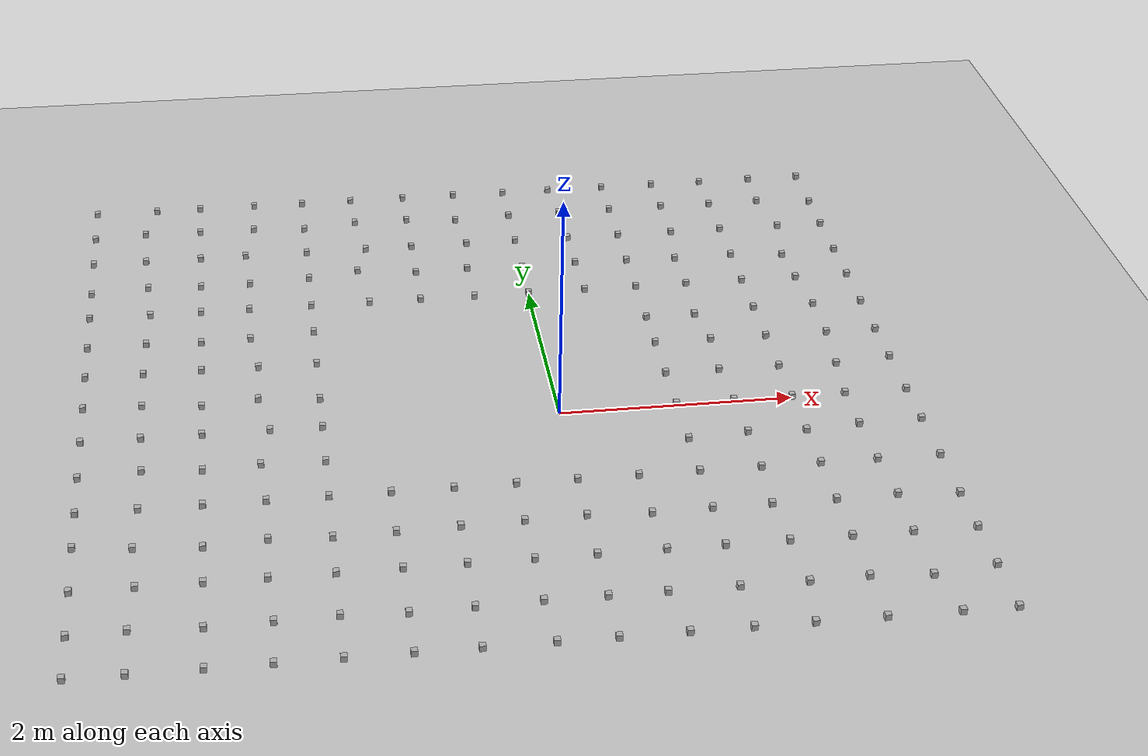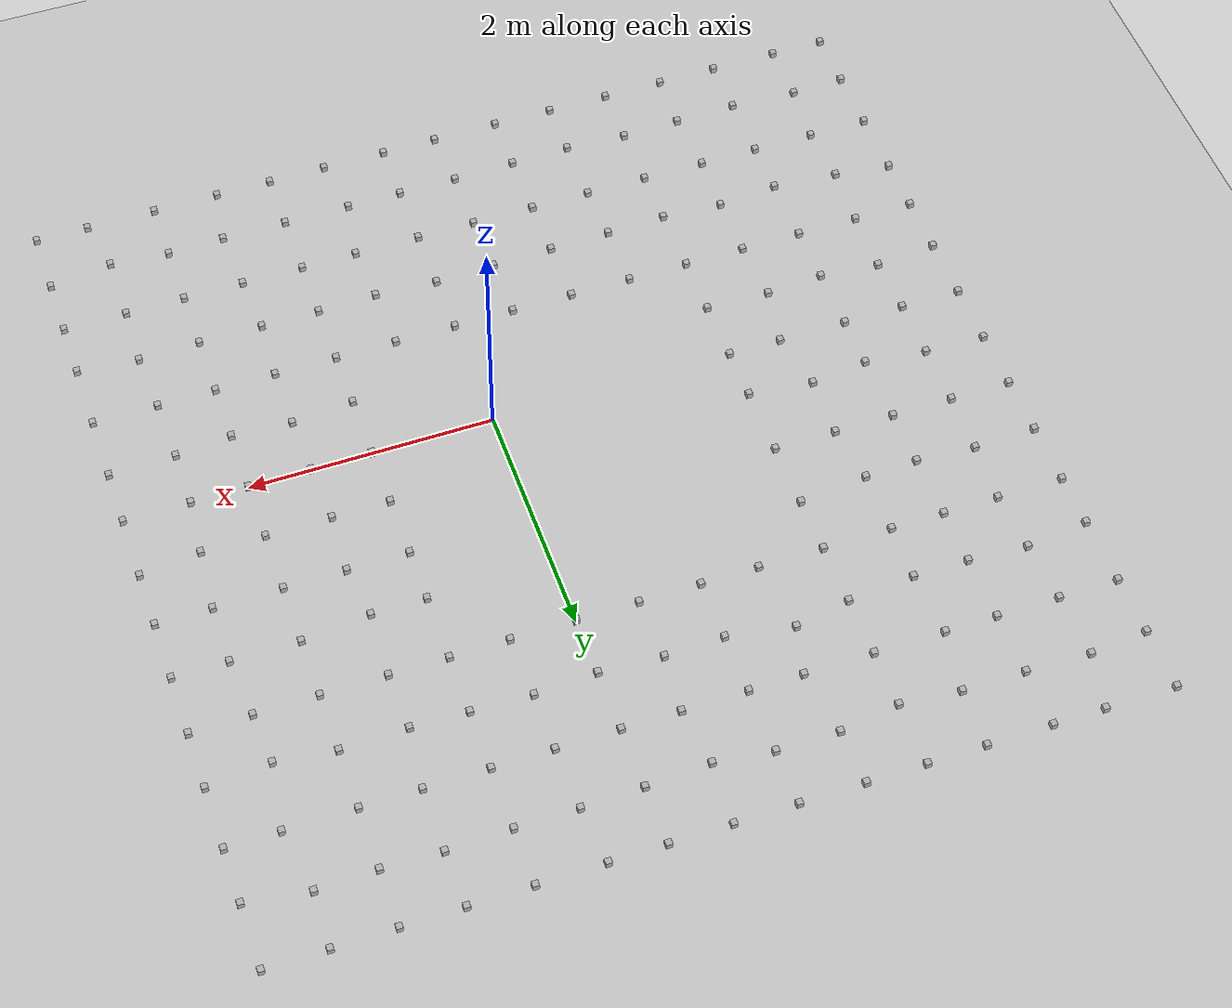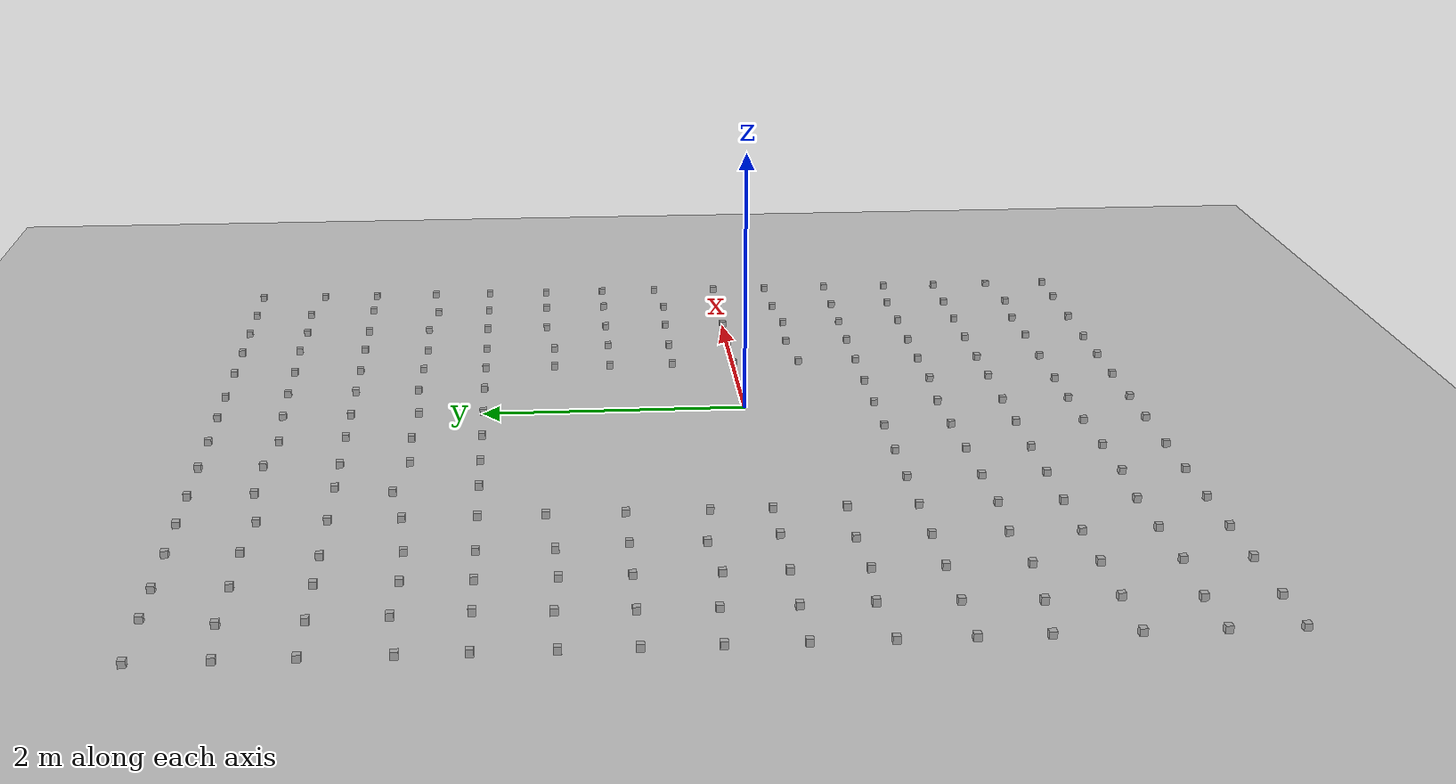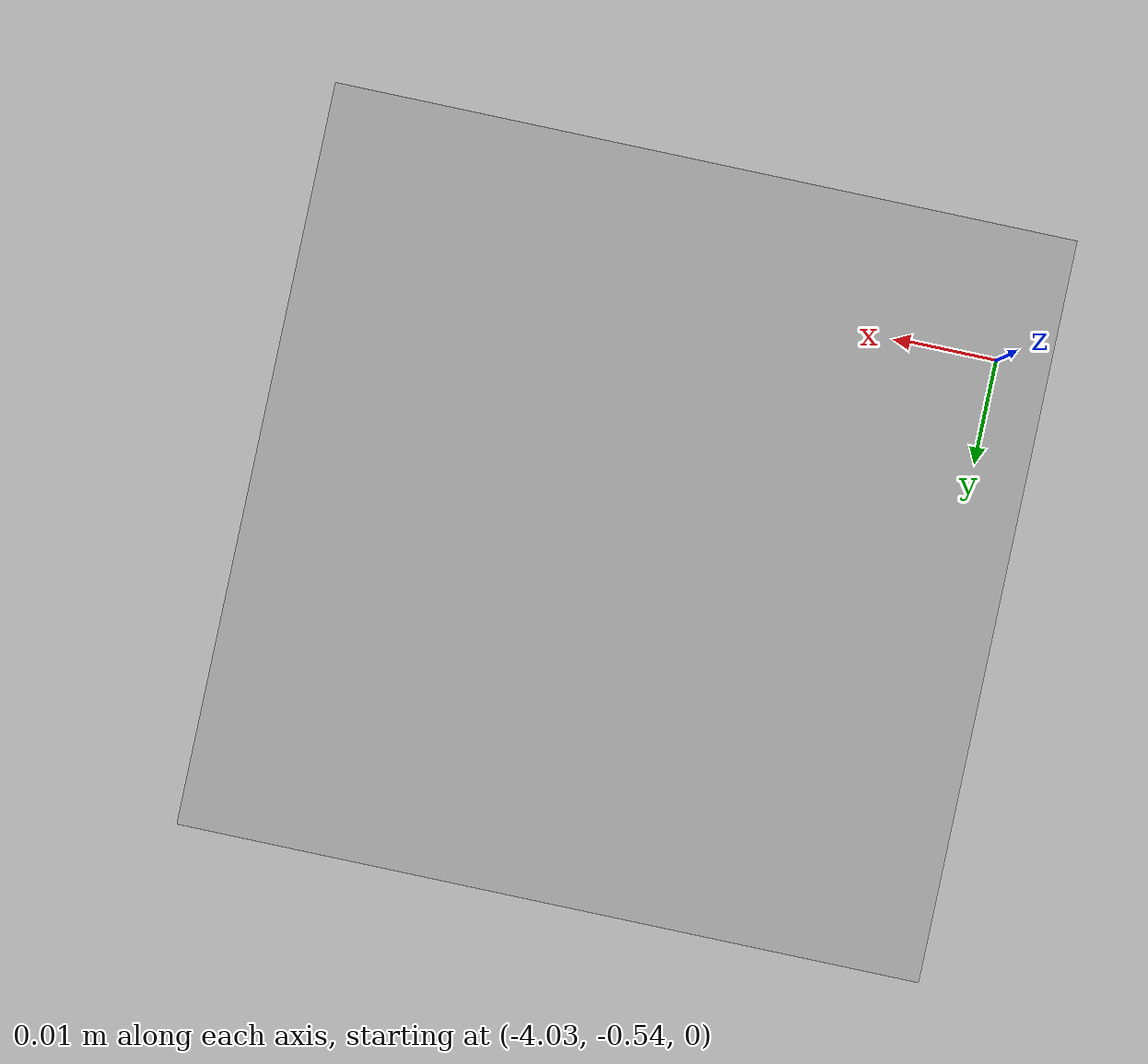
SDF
<sdf version="1.4">
 <world name="default">
  <model name="ground_plane">
   <static>1</static>
   <link name="link">
    <collision name="collision">
     <geometry><plane><normal>0 0 1</normal><size>100 100</size></plane></geometry>
     <surface><friction><ode><mu>100</mu><mu2>50</mu2></ode></friction></surface>
    </collision>
    <visual name="visual">
     <cast_shadows>0</cast_shadows>
     <geometry><plane><normal>0 0 1</normal><size>100 100</size></plane></geometry>
     <material>
      <script><uri>file://media/materials/scripts/gazebo.material</uri><name>Gazebo/Grey</name></script>
     </material>
    </visual>
    <velocity_decay><linear>0</linear><angular>0</angular></velocity_decay>
   </link>
  </model>
  <light name="sun" type="directional">
   <pose>0 0 10 0 -0 0</pose>
   <diffuse>0.8 0.8 0.8 1</diffuse>
   <specular>0.2 0.2 0.2 1</specular>
   <attenuation>
    <range>1000</range>
    <constant>0.9</constant>
    <linear>0.01</linear>
    <quadratic>0.001</quadratic>
   </attenuation>
   <direction>-0.5 0.1 -0.9</direction>
  </light>
  <plugin name="SetupWorld" filename="libgazebo_plugins.so"/>
  <physics type="ode">
   <max_step_size>0.001</max_step_size>
   <real_time_factor>1</real_time_factor>
   <real_time_update_rate>1000</real_time_update_rate>
   <gravity>0 0 -9.8</gravity>
  </physics>
  <scene><ambient>0.4 0.4 0.4 1</ambient><background>0.7 0.7 0.7 1</background><shadows>1</shadows></scene>
  <spherical_coordinates>
   <surface_model>EARTH_WGS84</surface_model>
   <latitude_deg>0</latitude_deg>
   <longitude_deg>0</longitude_deg>
   <elevation>0</elevation>
   <heading_deg>0</heading_deg>
  </spherical_coordinates>
  <model name="at0">
   <static>0</static>
   <link name="link">
    <pose>0 0 0.025 0 -0 0</pose>
    <inertial>
     <mass>0.1</mass>
     <inertia><ixx>4e-05</ixx><ixy>0</ixy><ixz>0</ixz><iyy>4e-05</iyy><iyz>0</iyz><izz>4e-05</izz></inertia>
    </inertial>
    <visual name="visual">
     <transparency>0.1</transparency>
     <geometry><box><size>0.05 0.05 0.05</size></box></geometry>
     <material>
      <script>
       <uri>model://at0/materials/scripts</uri>
       <uri>model://at0/materials/textures</uri>
       <name>at0/Diffuse</name>
      </script>
     </material>
    </visual>
    <collision name="collision">
     <pose>0 0 -0.0125 0 -0 0</pose>
     <geometry><box><size>0.05 0.05 0.025</size></box></geometry>
     <surface><friction><ode><mu>0.8</mu><mu2>0.7</mu2></ode></friction></surface>
    </collision>
    <velocity_decay><linear>0</linear><angular>0</angular></velocity_decay>
   </link>
   <pose>-1.54043 2.592 0 0 -0 0</pose>
  </model>
  <model name="at0_0">
   <static>0</static>
   <link name="link">
    <pose>0 0 0.025 0 -0 0</pose>
    <inertial>
     <mass>0.1</mass>
     <inertia><ixx>4e-05</ixx><ixy>0</ixy><ixz>0</ixz><iyy>4e-05</iyy><iyz>0</iyz><izz>4e-05</izz></inertia>
    </inertial>
    <visual name="visual">
     <transparency>0.1</transparency>
     <geometry><box><size>0.05 0.05 0.05</size></box></geometry>
     <material>
      <script>
       <uri>model://at0/materials/scripts</uri>
       <uri>model://at0/materials/textures</uri>
       <name>at0/Diffuse</name>
      </script>
     </material>
    </visual>
    <collision name="collision">
     <pose>0 0 -0.0125 0 -0 0</pose>
     <geometry><box><size>0.05 0.05 0.025</size></box></geometry>
     <surface><friction><ode><mu>0.8</mu><mu2>0.7</mu2></ode></friction></surface>
    </collision>
    <velocity_decay><linear>0</linear><angular>0</angular></velocity_decay>
   </link>
   <pose>-2 2 0 0 -0 0</pose>
  </model>
  <model name="at0_1">
   <static>0</static>
   <link name="link">
    <pose>0 0 0.025 0 -0 0</pose>
    <inertial>
     <mass>0.1</mass>
     <inertia><ixx>4e-05</ixx><ixy>0</ixy><ixz>0</ixz><iyy>4e-05</iyy><iyz>0</iyz><izz>4e-05</izz></inertia>
    </inertial>
    <visual name="visual">
     <transparency>0.1</transparency>
     <geometry><box><size>0.05 0.05 0.05</size></box></geometry>
     <material>
      <script>
       <uri>model://at0/materials/scripts</uri>
       <uri>model://at0/materials/textures</uri>
       <name>at0/Diffuse</name>
      </script>
     </material>
    </visual>
    <collision name="collision">
     <pose>0 0 -0.0125 0 -0 0</pose>
     <geometry><box><size>0.05 0.05 0.025</size></box></geometry>
     <surface><friction><ode><mu>0.8</mu><mu2>0.7</mu2></ode></friction></surface>
    </collision>
    <velocity_decay><linear>0</linear><angular>0</angular></velocity_decay>
   </link>
   <pose>-2 2.50634 0 0 -0 0</pose>
  </model>
  <model name="at0_2">
   <static>0</static>
   <link name="link">
    <pose>0 0 0.025 0 -0 0</pose>
    <inertial>
     <mass>0.1</mass>
     <inertia><ixx>4e-05</ixx><ixy>0</ixy><ixz>0</ixz><iyy>4e-05</iyy><iyz>0</iyz><izz>4e-05</izz></inertia>
    </inertial>
    <visual name="visual">
     <transparency>0.1</transparency>
     <geometry><box><size>0.05 0.05 0.05</size></box></geometry>
     <material>
      <script>
       <uri>model://at0/materials/scripts</uri>
       <uri>model://at0/materials/textures</uri>
       <name>at0/Diffuse</name>
      </script>
     </material>
    </visual>
    <collision name="collision">
     <pose>0 0 -0.0125 0 -0 0</pose>
     <geometry><box><size>0.05 0.05 0.025</size></box></geometry>
     <surface><friction><ode><mu>0.8</mu><mu2>0.7</mu2></ode></friction></surface>
    </collision>
    <velocity_decay><linear>0</linear><angular>0</angular></velocity_decay>
   </link>
   <pose>-2 3 0 0 -0 0</pose>
  </model>
  <model name="at0_3">
   <static>0</static>
   <link name="link">
    <pose>0 0 0.025 0 -0 0</pose>
    <inertial>
     <mass>0.1</mass>
     <inertia><ixx>4e-05</ixx><ixy>0</ixy><ixz>0</ixz><iyy>4e-05</iyy><iyz>0</iyz><izz>4e-05</izz></inertia>
    </inertial>
    <visual name="visual">
     <transparency>0.1</transparency>
     <geometry><box><size>0.05 0.05 0.05</size></box></geometry>
     <material>
      <script>
       <uri>model://at0/materials/scripts</uri>
       <uri>model://at0/materials/textures</uri>
       <name>at0/Diffuse</name>
      </script>
     </material>
    </visual>
    <collision name="collision">
     <pose>0 0 -0.0125 0 -0 0</pose>
     <geometry><box><size>0.05 0.05 0.025</size></box></geometry>
     <surface><friction><ode><mu>0.8</mu><mu2>0.7</mu2></ode></friction></surface>
    </collision>
    <velocity_decay><linear>0</linear><angular>0</angular></velocity_decay>
   </link>
   <pose>-1.43683 3 0 0 -0 0</pose>
  </model>
  <model name="at0_4">
   <static>0</static>
   <link name="link">
    <pose>0 0 0.025 0 -0 0</pose>
    <inertial>
     <mass>0.1</mass>
     <inertia><ixx>4e-05</ixx><ixy>0</ixy><ixz>0</ixz><iyy>4e-05</iyy><iyz>0</iyz><izz>4e-05</izz></inertia>
    </inertial>
    <visual name="visual">
     <transparency>0.1</transparency>
     <geometry><box><size>0.05 0.05 0.05</size></box></geometry>
     <material>
      <script>
       <uri>model://at0/materials/scripts</uri>
       <uri>model://at0/materials/textures</uri>
       <name>at0/Diffuse</name>
      </script>
     </material>
    </visual>
    <collision name="collision">
     <pose>0 0 -0.0125 0 -0 0</pose>
     <geometry><box><size>0.05 0.05 0.025</size></box></geometry>
     <surface><friction><ode><mu>0.8</mu><mu2>0.7</mu2></ode></friction></surface>
    </collision>
    <velocity_decay><linear>0</linear><angular>0</angular></velocity_decay>
   </link>
   <pose>-1 3 0 0 -0 0</pose>
  </model>
  <model name="at0_5">
   <static>0</static>
   <link name="link">
    <pose>0 0 0.025 0 -0 0</pose>
    <inertial>
     <mass>0.1</mass>
     <inertia><ixx>4e-05</ixx><ixy>0</ixy><ixz>0</ixz><iyy>4e-05</iyy><iyz>0</iyz><izz>4e-05</izz></inertia>
    </inertial>
    <visual name="visual">
     <transparency>0.1</transparency>
     <geometry><box><size>0.05 0.05 0.05</size></box></geometry>
     <material>
      <script>
       <uri>model://at0/materials/scripts</uri>
       <uri>model://at0/materials/textures</uri>
       <name>at0/Diffuse</name>
      </script>
     </material>
    </visual>
    <collision name="collision">
     <pose>0 0 -0.0125 0 -0 0</pose>
     <geometry><box><size>0.05 0.05 0.025</size></box></geometry>
     <surface><friction><ode><mu>0.8</mu><mu2>0.7</mu2></ode></friction></surface>
    </collision>
    <velocity_decay><linear>0</linear><angular>0</angular></velocity_decay>
   </link>
   <pose>-1 2 0 0 -0 0</pose>
  </model>
  <model name="at0_6">
   <static>0</static>
   <link name="link">
    <pose>0 0 0.025 0 -0 0</pose>
    <inertial>
     <mass>0.1</mass>
     <inertia><ixx>4e-05</ixx><ixy>0</ixy><ixz>0</ixz><iyy>4e-05</iyy><iyz>0</iyz><izz>4e-05</izz></inertia>
    </inertial>
    <visual name="visual">
     <transparency>0.1</transparency>
     <geometry><box><size>0.05 0.05 0.05</size></box></geometry>
     <material>
      <script>
       <uri>model://at0/materials/scripts</uri>
       <uri>model://at0/materials/textures</uri>
       <name>at0/Diffuse</name>
      </script>
     </material>
    </visual>
    <collision name="collision">
     <pose>0 0 -0.0125 0 -0 0</pose>
     <geometry><box><size>0.05 0.05 0.025</size></box></geometry>
     <surface><friction><ode><mu>0.8</mu><mu2>0.7</mu2></ode></friction></surface>
    </collision>
    <velocity_decay><linear>0</linear><angular>0</angular></velocity_decay>
   </link>
   <pose>-1 2.50258 0 0 -0 0</pose>
  </model>
  <model name="at0_7">
   <static>0</static>
   <link name="link">
    <pose>0 0 0.025 0 -0 0</pose>
    <inertial>
     <mass>0.1</mass>
     <inertia><ixx>4e-05</ixx><ixy>0</ixy><ixz>0</ixz><iyy>4e-05</iyy><iyz>0</iyz><izz>4e-05</izz></inertia>
    </inertial>
    <visual name="visual">
     <transparency>0.1</transparency>
     <geometry><box><size>0.05 0.05 0.05</size></box></geometry>
     <material>
      <script>
       <uri>model://at0/materials/scripts</uri>
       <uri>model://at0/materials/textures</uri>
       <name>at0/Diffuse</name>
      </script>
     </material>
    </visual>
    <collision name="collision">
     <pose>0 0 -0.0125 0 -0 0</pose>
     <geometry><box><size>0.05 0.05 0.025</size></box></geometry>
     <surface><friction><ode><mu>0.8</mu><mu2>0.7</mu2></ode></friction></surface>
    </collision>
    <velocity_decay><linear>0</linear><angular>0</angular></velocity_decay>
   </link>
   <pose>-1.46869 2 0 0 -0 0</pose>
  </model>
  <model name="at0_8">
   <static>0</static>
   <link name="link">
    <pose>0 0 0.025 0 -0 0</pose>
    <inertial>
     <mass>0.1</mass>
     <inertia><ixx>4e-05</ixx><ixy>0</ixy><ixz>0</ixz><iyy>4e-05</iyy><iyz>0</iyz><izz>4e-05</izz></inertia>
    </inertial>
    <visual name="visual">
     <transparency>0.1</transparency>
     <geometry><box><size>0.05 0.05 0.05</size></box></geometry>
     <material>
      <script>
       <uri>model://at0/materials/scripts</uri>
       <uri>model://at0/materials/textures</uri>
       <name>at0/Diffuse</name>
      </script>
     </material>
    </visual>
    <collision name="collision">
     <pose>0 0 -0.0125 0 -0 0</pose>
     <geometry><box><size>0.05 0.05 0.025</size></box></geometry>
     <surface><friction><ode><mu>0.8</mu><mu2>0.7</mu2></ode></friction></surface>
    </collision>
    <velocity_decay><linear>0</linear><angular>0</angular></velocity_decay>
   </link>
   <pose>-0.469874 3 0 0 -0 0</pose>
  </model>
  <model name="at0_9">
   <static>0</static>
   <link name="link">
    <pose>0 0 0.025 0 -0 0</pose>
    <inertial>
     <mass>0.1</mass>
     <inertia><ixx>4e-05</ixx><ixy>0</ixy><ixz>0</ixz><iyy>4e-05</iyy><iyz>0</iyz><izz>4e-05</izz></inertia>
    </inertial>
    <visual name="visual">
     <transparency>0.1</transparency>
     <geometry><box><size>0.05 0.05 0.05</size></box></geometry>
     <material>
      <script>
       <uri>model://at0/materials/scripts</uri>
       <uri>model://at0/materials/textures</uri>
       <name>at0/Diffuse</name>
      </script>
     </material>
    </visual>
    <collision name="collision">
     <pose>0 0 -0.0125 0 -0 0</pose>
     <geometry><box><size>0.05 0.05 0.025</size></box></geometry>
     <surface><friction><ode><mu>0.8</mu><mu2>0.7</mu2></ode></friction></surface>
    </collision>
    <velocity_decay><linear>0</linear><angular>0</angular></velocity_decay>
   </link>
   <pose>0 3 0 0 -0 0</pose>
  </model>
  <model name="at0_10">
   <static>0</static>
   <link name="link">
    <pose>0 0 0.025 0 -0 0</pose>
    <inertial>
     <mass>0.1</mass>
     <inertia><ixx>4e-05</ixx><ixy>0</ixy><ixz>0</ixz><iyy>4e-05</iyy><iyz>0</iyz><izz>4e-05</izz></inertia>
    </inertial>
    <visual name="visual">
     <transparency>0.1</transparency>
     <geometry><box><size>0.05 0.05 0.05</size></box></geometry>
     <material>
      <script>
       <uri>model://at0/materials/scripts</uri>
       <uri>model://at0/materials/textures</uri>
       <name>at0/Diffuse</name>
      </script>
     </material>
    </visual>
    <collision name="collision">
     <pose>0 0 -0.0125 0 -0 0</pose>
     <geometry><box><size>0.05 0.05 0.025</size></box></geometry>
     <surface><friction><ode><mu>0.8</mu><mu2>0.7</mu2></ode></friction></surface>
    </collision>
    <velocity_decay><linear>0</linear><angular>0</angular></velocity_decay>
   </link>
   <pose>0 2.48596 0 0 -0 0</pose>
  </model>
  <model name="at0_11">
   <static>0</static>
   <link name="link">
    <pose>0 0 0.025 0 -0 0</pose>
    <inertial>
     <mass>0.1</mass>
     <inertia><ixx>4e-05</ixx><ixy>0</ixy><ixz>0</ixz><iyy>4e-05</iyy><iyz>0</iyz><izz>4e-05</izz></inertia>
    </inertial>
    <visual name="visual">
     <transparency>0.1</transparency>
     <geometry><box><size>0.05 0.05 0.05</size></box></geometry>
     <material>
      <script>
       <uri>model://at0/materials/scripts</uri>
       <uri>model://at0/materials/textures</uri>
       <name>at0/Diffuse</name>
      </script>
     </material>
    </visual>
    <collision name="collision">
     <pose>0 0 -0.0125 0 -0 0</pose>
     <geometry><box><size>0.05 0.05 0.025</size></box></geometry>
     <surface><friction><ode><mu>0.8</mu><mu2>0.7</mu2></ode></friction></surface>
    </collision>
    <velocity_decay><linear>0</linear><angular>0</angular></velocity_decay>
   </link>
   <pose>-0.501759 2 0 0 -0 0</pose>
  </model>
  <model name="at0_12">
   <static>0</static>
   <link name="link">
    <pose>0 0 0.025 0 -0 0</pose>
    <inertial>
     <mass>0.1</mass>
     <inertia><ixx>4e-05</ixx><ixy>0</ixy><ixz>0</ixz><iyy>4e-05</iyy><iyz>0</iyz><izz>4e-05</izz></inertia>
    </inertial>
    <visual name="visual">
     <transparency>0.1</transparency>
     <geometry><box><size>0.05 0.05 0.05</size></box></geometry>
     <material>
      <script>
       <uri>model://at0/materials/scripts</uri>
       <uri>model://at0/materials/textures</uri>
       <name>at0/Diffuse</name>
      </script>
     </material>
    </visual>
    <collision name="collision">
     <pose>0 0 -0.0125 0 -0 0</pose>
     <geometry><box><size>0.05 0.05 0.025</size></box></geometry>
     <surface><friction><ode><mu>0.8</mu><mu2>0.7</mu2></ode></friction></surface>
    </collision>
    <velocity_decay><linear>0</linear><angular>0</angular></velocity_decay>
   </link>
   <pose>-0.514878 2.51621 0 0 -0 0</pose>
  </model>
  <model name="at0_13">
   <static>0</static>
   <link name="link">
    <pose>0 0 0.025 0 -0 0</pose>
    <inertial>
     <mass>0.1</mass>
     <inertia><ixx>4e-05</ixx><ixy>0</ixy><ixz>0</ixz><iyy>4e-05</iyy><iyz>0</iyz><izz>4e-05</izz></inertia>
    </inertial>
    <visual name="visual">
     <transparency>0.1</transparency>
     <geometry><box><size>0.05 0.05 0.05</size></box></geometry>
     <material>
      <script>
       <uri>model://at0/materials/scripts</uri>
       <uri>model://at0/materials/textures</uri>
       <name>at0/Diffuse</name>
      </script>
     </material>
    </visual>
    <collision name="collision">
     <pose>0 0 -0.0125 0 -0 0</pose>
     <geometry><box><size>0.05 0.05 0.025</size></box></geometry>
     <surface><friction><ode><mu>0.8</mu><mu2>0.7</mu2></ode></friction></surface>
    </collision>
    <velocity_decay><linear>0</linear><angular>0</angular></velocity_decay>
   </link>
   <pose>0 2 0 0 -0 0</pose>
  </model>
  <model name="at0_14">
   <static>0</static>
   <link name="link">
    <pose>0 0 0.025 0 -0 0</pose>
    <inertial>
     <mass>0.1</mass>
     <inertia><ixx>4e-05</ixx><ixy>0</ixy><ixz>0</ixz><iyy>4e-05</iyy><iyz>0</iyz><izz>4e-05</izz></inertia>
    </inertial>
    <visual name="visual">
     <transparency>0.1</transparency>
     <geometry><box><size>0.05 0.05 0.05</size></box></geometry>
     <material>
      <script>
       <uri>model://at0/materials/scripts</uri>
       <uri>model://at0/materials/textures</uri>
       <name>at0/Diffuse</name>
      </script>
     </material>
    </visual>
    <collision name="collision">
     <pose>0 0 -0.0125 0 -0 0</pose>
     <geometry><box><size>0.05 0.05 0.025</size></box></geometry>
     <surface><friction><ode><mu>0.8</mu><mu2>0.7</mu2></ode></friction></surface>
    </collision>
    <velocity_decay><linear>0</linear><angular>0</angular></velocity_decay>
   </link>
   <pose>1 3 0 0 -0 0</pose>
  </model>
  <model name="at0_15">
   <static>0</static>
   <link name="link">
    <pose>0 0 0.025 0 -0 0</pose>
    <inertial>
     <mass>0.1</mass>
     <inertia><ixx>4e-05</ixx><ixy>0</ixy><ixz>0</ixz><iyy>4e-05</iyy><iyz>0</iyz><izz>4e-05</izz></inertia>
    </inertial>
    <visual name="visual">
     <transparency>0.1</transparency>
     <geometry><box><size>0.05 0.05 0.05</size></box></geometry>
     <material>
      <script>
       <uri>model://at0/materials/scripts</uri>
       <uri>model://at0/materials/textures</uri>
       <name>at0/Diffuse</name>
      </script>
     </material>
    </visual>
    <collision name="collision">
     <pose>0 0 -0.0125 0 -0 0</pose>
     <geometry><box><size>0.05 0.05 0.025</size></box></geometry>
     <surface><friction><ode><mu>0.8</mu><mu2>0.7</mu2></ode></friction></surface>
    </collision>
    <velocity_decay><linear>0</linear><angular>0</angular></velocity_decay>
   </link>
   <pose>0.510168 3 0 0 -0 0</pose>
  </model>
  <model name="at0_16">
   <static>0</static>
   <link name="link">
    <pose>0 0 0.025 0 -0 0</pose>
    <inertial>
     <mass>0.1</mass>
     <inertia><ixx>4e-05</ixx><ixy>0</ixy><ixz>0</ixz><iyy>4e-05</iyy><iyz>0</iyz><izz>4e-05</izz></inertia>
    </inertial>
    <visual name="visual">
     <transparency>0.1</transparency>
     <geometry><box><size>0.05 0.05 0.05</size></box></geometry>
     <material>
      <script>
       <uri>model://at0/materials/scripts</uri>
       <uri>model://at0/materials/textures</uri>
       <name>at0/Diffuse</name>
      </script>
     </material>
    </visual>
    <collision name="collision">
     <pose>0 0 -0.0125 0 -0 0</pose>
     <geometry><box><size>0.05 0.05 0.025</size></box></geometry>
     <surface><friction><ode><mu>0.8</mu><mu2>0.7</mu2></ode></friction></surface>
    </collision>
    <velocity_decay><linear>0</linear><angular>0</angular></velocity_decay>
   </link>
   <pose>1 2.49709 0 0 -0 0</pose>
  </model>
  <model name="at0_17">
   <static>0</static>
   <link name="link">
    <pose>0 0 0.025 0 -0 0</pose>
    <inertial>
     <mass>0.1</mass>
     <inertia><ixx>4e-05</ixx><ixy>0</ixy><ixz>0</ixz><iyy>4e-05</iyy><iyz>0</iyz><izz>4e-05</izz></inertia>
    </inertial>
    <visual name="visual">
     <transparency>0.1</transparency>
     <geometry><box><size>0.05 0.05 0.05</size></box></geometry>
     <material>
      <script>
       <uri>model://at0/materials/scripts</uri>
       <uri>model://at0/materials/textures</uri>
       <name>at0/Diffuse</name>
      </script>
     </material>
    </visual>
    <collision name="collision">
     <pose>0 0 -0.0125 0 -0 0</pose>
     <geometry><box><size>0.05 0.05 0.025</size></box></geometry>
     <surface><friction><ode><mu>0.8</mu><mu2>0.7</mu2></ode></friction></surface>
    </collision>
    <velocity_decay><linear>0</linear><angular>0</angular></velocity_decay>
   </link>
   <pose>0.522175 2 0 0 -0 0</pose>
  </model>
  <model name="at0_18">
   <static>0</static>
   <link name="link">
    <pose>0 0 0.025 0 -0 0</pose>
    <inertial>
     <mass>0.1</mass>
     <inertia><ixx>4e-05</ixx><ixy>0</ixy><ixz>0</ixz><iyy>4e-05</iyy><iyz>0</iyz><izz>4e-05</izz></inertia>
    </inertial>
    <visual name="visual">
     <transparency>0.1</transparency>
     <geometry><box><size>0.05 0.05 0.05</size></box></geometry>
     <material>
      <script>
       <uri>model://at0/materials/scripts</uri>
       <uri>model://at0/materials/textures</uri>
       <name>at0/Diffuse</name>
      </script>
     </material>
    </visual>
    <collision name="collision">
     <pose>0 0 -0.0125 0 -0 0</pose>
     <geometry><box><size>0.05 0.05 0.025</size></box></geometry>
     <surface><friction><ode><mu>0.8</mu><mu2>0.7</mu2></ode></friction></surface>
    </collision>
    <velocity_decay><linear>0</linear><angular>0</angular></velocity_decay>
   </link>
   <pose>0.508937 2.51354 0 0 -0 0</pose>
  </model>
  <model name="at0_19">
   <static>0</static>
   <link name="link">
    <pose>0 0 0.025 0 -0 0</pose>
    <inertial>
     <mass>0.1</mass>
     <inertia><ixx>4e-05</ixx><ixy>0</ixy><ixz>0</ixz><iyy>4e-05</iyy><iyz>0</iyz><izz>4e-05</izz></inertia>
    </inertial>
    <visual name="visual">
     <transparency>0.1</transparency>
     <geometry><box><size>0.05 0.05 0.05</size></box></geometry>
     <material>
      <script>
       <uri>model://at0/materials/scripts</uri>
       <uri>model://at0/materials/textures</uri>
       <name>at0/Diffuse</name>
      </script>
     </material>
    </visual>
    <collision name="collision">
     <pose>0 0 -0.0125 0 -0 0</pose>
     <geometry><box><size>0.05 0.05 0.025</size></box></geometry>
     <surface><friction><ode><mu>0.8</mu><mu2>0.7</mu2></ode></friction></surface>
    </collision>
    <velocity_decay><linear>0</linear><angular>0</angular></velocity_decay>
   </link>
   <pose>1 2 0 0 -0 0</pose>
  </model>
  <model name="at0_20">
   <static>0</static>
   <link name="link">
    <pose>0 0 0.025 0 -0 0</pose>
    <inertial>
     <mass>0.1</mass>
     <inertia><ixx>4e-05</ixx><ixy>0</ixy><ixz>0</ixz><iyy>4e-05</iyy><iyz>0</iyz><izz>4e-05</izz></inertia>
    </inertial>
    <visual name="visual">
     <transparency>0.1</transparency>
     <geometry><box><size>0.05 0.05 0.05</size></box></geometry>
     <material>
      <script>
       <uri>model://at0/materials/scripts</uri>
       <uri>model://at0/materials/textures</uri>
       <name>at0/Diffuse</name>
      </script>
     </material>
    </visual>
    <collision name="collision">
     <pose>0 0 -0.0125 0 -0 0</pose>
     <geometry><box><size>0.05 0.05 0.025</size></box></geometry>
     <surface><friction><ode><mu>0.8</mu><mu2>0.7</mu2></ode></friction></surface>
    </collision>
    <velocity_decay><linear>0</linear><angular>0</angular></velocity_decay>
   </link>
   <pose>2 3 0 0 -0 0</pose>
  </model>
  <model name="at0_21">
   <static>0</static>
   <link name="link">
    <pose>0 0 0.025 0 -0 0</pose>
    <inertial>
     <mass>0.1</mass>
     <inertia><ixx>4e-05</ixx><ixy>0</ixy><ixz>0</ixz><iyy>4e-05</iyy><iyz>0</iyz><izz>4e-05</izz></inertia>
    </inertial>
    <visual name="visual">
     <transparency>0.1</transparency>
     <geometry><box><size>0.05 0.05 0.05</size></box></geometry>
     <material>
      <script>
       <uri>model://at0/materials/scripts</uri>
       <uri>model://at0/materials/textures</uri>
       <name>at0/Diffuse</name>
      </script>
     </material>
    </visual>
    <collision name="collision">
     <pose>0 0 -0.0125 0 -0 0</pose>
     <geometry><box><size>0.05 0.05 0.025</size></box></geometry>
     <surface><friction><ode><mu>0.8</mu><mu2>0.7</mu2></ode></friction></surface>
    </collision>
    <velocity_decay><linear>0</linear><angular>0</angular></velocity_decay>
   </link>
   <pose>2 2.49507 0 0 -0 0</pose>
  </model>
  <model name="at0_22">
   <static>0</static>
   <link name="link">
    <pose>0 0 0.025 0 -0 0</pose>
    <inertial>
     <mass>0.1</mass>
     <inertia><ixx>4e-05</ixx><ixy>0</ixy><ixz>0</ixz><iyy>4e-05</iyy><iyz>0</iyz><izz>4e-05</izz></inertia>
    </inertial>
    <visual name="visual">
     <transparency>0.1</transparency>
     <geometry><box><size>0.05 0.05 0.05</size></box></geometry>
     <material>
      <script>
       <uri>model://at0/materials/scripts</uri>
       <uri>model://at0/materials/textures</uri>
       <name>at0/Diffuse</name>
      </script>
     </material>
    </visual>
    <collision name="collision">
     <pose>0 0 -0.0125 0 -0 0</pose>
     <geometry><box><size>0.05 0.05 0.025</size></box></geometry>
     <surface><friction><ode><mu>0.8</mu><mu2>0.7</mu2></ode></friction></surface>
    </collision>
    <velocity_decay><linear>0</linear><angular>0</angular></velocity_decay>
   </link>
   <pose>2 2 0 0 -0 0</pose>
  </model>
  <model name="at0_23">
   <static>0</static>
   <link name="link">
    <pose>0 0 0.025 0 -0 0</pose>
    <inertial>
     <mass>0.1</mass>
     <inertia><ixx>4e-05</ixx><ixy>0</ixy><ixz>0</ixz><iyy>4e-05</iyy><iyz>0</iyz><izz>4e-05</izz></inertia>
    </inertial>
    <visual name="visual">
     <transparency>0.1</transparency>
     <geometry><box><size>0.05 0.05 0.05</size></box></geometry>
     <material>
      <script>
       <uri>model://at0/materials/scripts</uri>
       <uri>model://at0/materials/textures</uri>
       <name>at0/Diffuse</name>
      </script>
     </material>
    </visual>
    <collision name="collision">
     <pose>0 0 -0.0125 0 -0 0</pose>
     <geometry><box><size>0.05 0.05 0.025</size></box></geometry>
     <surface><friction><ode><mu>0.8</mu><mu2>0.7</mu2></ode></friction></surface>
    </collision>
    <velocity_decay><linear>0</linear><angular>0</angular></velocity_decay>
   </link>
   <pose>1.45955 2.48181 0 0 -0 0</pose>
  </model>
  <model name="at0_24">
   <static>0</static>
   <link name="link">
    <pose>0 0 0.025 0 -0 0</pose>
    <inertial>
     <mass>0.1</mass>
     <inertia><ixx>4e-05</ixx><ixy>0</ixy><ixz>0</ixz><iyy>4e-05</iyy><iyz>0</iyz><izz>4e-05</izz></inertia>
    </inertial>
    <visual name="visual">
     <transparency>0.1</transparency>
     <geometry><box><size>0.05 0.05 0.05</size></box></geometry>
     <material>
      <script>
       <uri>model://at0/materials/scripts</uri>
       <uri>model://at0/materials/textures</uri>
       <name>at0/Diffuse</name>
      </script>
     </material>
    </visual>
    <collision name="collision">
     <pose>0 0 -0.0125 0 -0 0</pose>
     <geometry><box><size>0.05 0.05 0.025</size></box></geometry>
     <surface><friction><ode><mu>0.8</mu><mu2>0.7</mu2></ode></friction></surface>
    </collision>
    <velocity_decay><linear>0</linear><angular>0</angular></velocity_decay>
   </link>
   <pose>1.5195 3 0 0 -0 0</pose>
  </model>
  <model name="at0_25">
   <static>0</static>
   <link name="link">
    <pose>0 0 0.025 0 -0 0</pose>
    <inertial>
     <mass>0.1</mass>
     <inertia><ixx>4e-05</ixx><ixy>0</ixy><ixz>0</ixz><iyy>4e-05</iyy><iyz>0</iyz><izz>4e-05</izz></inertia>
    </inertial>
    <visual name="visual">
     <transparency>0.1</transparency>
     <geometry><box><size>0.05 0.05 0.05</size></box></geometry>
     <material>
      <script>
       <uri>model://at0/materials/scripts</uri>
       <uri>model://at0/materials/textures</uri>
       <name>at0/Diffuse</name>
      </script>
     </material>
    </visual>
    <collision name="collision">
     <pose>0 0 -0.0125 0 -0 0</pose>
     <geometry><box><size>0.05 0.05 0.025</size></box></geometry>
     <surface><friction><ode><mu>0.8</mu><mu2>0.7</mu2></ode></friction></surface>
    </collision>
    <velocity_decay><linear>0</linear><angular>0</angular></velocity_decay>
   </link>
   <pose>1.4729 2 0 0 -0 0</pose>
  </model>
  <model name="at0_31">
   <static>0</static>
   <link name="link">
    <pose>0 0 0.025 0 -0 0</pose>
    <inertial>
     <mass>0.1</mass>
     <inertia><ixx>4e-05</ixx><ixy>0</ixy><ixz>0</ixz><iyy>4e-05</iyy><iyz>0</iyz><izz>4e-05</izz></inertia>
    </inertial>
    <visual name="visual">
     <transparency>0.1</transparency>
     <geometry><box><size>0.05 0.05 0.05</size></box></geometry>
     <material>
      <script>
       <uri>model://at0/materials/scripts</uri>
       <uri>model://at0/materials/textures</uri>
       <name>at0/Diffuse</name>
      </script>
     </material>
    </visual>
    <collision name="collision">
     <pose>0 0 -0.0125 0 -0 0</pose>
     <geometry><box><size>0.05 0.05 0.025</size></box></geometry>
     <surface><friction><ode><mu>0.8</mu><mu2>0.7</mu2></ode></friction></surface>
    </collision>
    <velocity_decay><linear>0</linear><angular>0</angular></velocity_decay>
   </link>
   <pose>-2.54804 2.46299 0 0 -0 0</pose>
  </model>
  <model name="at0_32">
   <static>0</static>
   <link name="link">
    <pose>0 0 0.025 0 -0 0</pose>
    <inertial>
     <mass>0.1</mass>
     <inertia><ixx>4e-05</ixx><ixy>0</ixy><ixz>0</ixz><iyy>4e-05</iyy><iyz>0</iyz><izz>4e-05</izz></inertia>
    </inertial>
    <visual name="visual">
     <transparency>0.1</transparency>
     <geometry><box><size>0.05 0.05 0.05</size></box></geometry>
     <material>
      <script>
       <uri>model://at0/materials/scripts</uri>
       <uri>model://at0/materials/textures</uri>
       <name>at0/Diffuse</name>
      </script>
     </material>
    </visual>
    <collision name="collision">
     <pose>0 0 -0.0125 0 -0 0</pose>
     <geometry><box><size>0.05 0.05 0.025</size></box></geometry>
     <surface><friction><ode><mu>0.8</mu><mu2>0.7</mu2></ode></friction></surface>
    </collision>
    <velocity_decay><linear>0</linear><angular>0</angular></velocity_decay>
   </link>
   <pose>-2.57592 3 0 0 -0 0</pose>
  </model>
  <model name="at0_33">
   <static>0</static>
   <link name="link">
    <pose>0 0 0.025 0 -0 0</pose>
    <inertial>
     <mass>0.1</mass>
     <inertia><ixx>4e-05</ixx><ixy>0</ixy><ixz>0</ixz><iyy>4e-05</iyy><iyz>0</iyz><izz>4e-05</izz></inertia>
    </inertial>
    <visual name="visual">
     <transparency>0.1</transparency>
     <geometry><box><size>0.05 0.05 0.05</size></box></geometry>
     <material>
      <script>
       <uri>model://at0/materials/scripts</uri>
       <uri>model://at0/materials/textures</uri>
       <name>at0/Diffuse</name>
      </script>
     </material>
    </visual>
    <collision name="collision">
     <pose>0 0 -0.0125 0 -0 0</pose>
     <geometry><box><size>0.05 0.05 0.025</size></box></geometry>
     <surface><friction><ode><mu>0.8</mu><mu2>0.7</mu2></ode></friction></surface>
    </collision>
    <velocity_decay><linear>0</linear><angular>0</angular></velocity_decay>
   </link>
   <pose>-3 3 0 0 -0 0</pose>
  </model>
  <model name="at0_34">
   <static>0</static>
   <link name="link">
    <pose>0 0 0.025 0 -0 0</pose>
    <inertial>
     <mass>0.1</mass>
     <inertia><ixx>4e-05</ixx><ixy>0</ixy><ixz>0</ixz><iyy>4e-05</iyy><iyz>0</iyz><izz>4e-05</izz></inertia>
    </inertial>
    <visual name="visual">
     <transparency>0.1</transparency>
     <geometry><box><size>0.05 0.05 0.05</size></box></geometry>
     <material>
      <script>
       <uri>model://at0/materials/scripts</uri>
       <uri>model://at0/materials/textures</uri>
       <name>at0/Diffuse</name>
      </script>
     </material>
    </visual>
    <collision name="collision">
     <pose>0 0 -0.0125 0 -0 0</pose>
     <geometry><box><size>0.05 0.05 0.025</size></box></geometry>
     <surface><friction><ode><mu>0.8</mu><mu2>0.7</mu2></ode></friction></surface>
    </collision>
    <velocity_decay><linear>0</linear><angular>0</angular></velocity_decay>
   </link>
   <pose>-3 2.46463 0 0 -0 0</pose>
  </model>
  <model name="at0_35">
   <static>0</static>
   <link name="link">
    <pose>0 0 0.025 0 -0 0</pose>
    <inertial>
     <mass>0.1</mass>
     <inertia><ixx>4e-05</ixx><ixy>0</ixy><ixz>0</ixz><iyy>4e-05</iyy><iyz>0</iyz><izz>4e-05</izz></inertia>
    </inertial>
    <visual name="visual">
     <transparency>0.1</transparency>
     <geometry><box><size>0.05 0.05 0.05</size></box></geometry>
     <material>
      <script>
       <uri>model://at0/materials/scripts</uri>
       <uri>model://at0/materials/textures</uri>
       <name>at0/Diffuse</name>
      </script>
     </material>
    </visual>
    <collision name="collision">
     <pose>0 0 -0.0125 0 -0 0</pose>
     <geometry><box><size>0.05 0.05 0.025</size></box></geometry>
     <surface><friction><ode><mu>0.8</mu><mu2>0.7</mu2></ode></friction></surface>
    </collision>
    <velocity_decay><linear>0</linear><angular>0</angular></velocity_decay>
   </link>
   <pose>-3 2 0 0 -0 0</pose>
  </model>
  <model name="at0_36">
   <static>0</static>
   <link name="link">
    <pose>0 0 0.025 0 -0 0</pose>
    <inertial>
     <mass>0.1</mass>
     <inertia><ixx>4e-05</ixx><ixy>0</ixy><ixz>0</ixz><iyy>4e-05</iyy><iyz>0</iyz><izz>4e-05</izz></inertia>
    </inertial>
    <visual name="visual">
     <transparency>0.1</transparency>
     <geometry><box><size>0.05 0.05 0.05</size></box></geometry>
     <material>
      <script>
       <uri>model://at0/materials/scripts</uri>
       <uri>model://at0/materials/textures</uri>
       <name>at0/Diffuse</name>
      </script>
     </material>
    </visual>
    <collision name="collision">
     <pose>0 0 -0.0125 0 -0 0</pose>
     <geometry><box><size>0.05 0.05 0.025</size></box></geometry>
     <surface><friction><ode><mu>0.8</mu><mu2>0.7</mu2></ode></friction></surface>
    </collision>
    <velocity_decay><linear>0</linear><angular>0</angular></velocity_decay>
   </link>
   <pose>-2.56355 2 0 0 -0 0</pose>
  </model>
  <model name="at0_37">
   <static>0</static>
   <link name="link">
    <pose>0 0 0.025 0 -0 0</pose>
    <inertial>
     <mass>0.1</mass>
     <inertia><ixx>4e-05</ixx><ixy>0</ixy><ixz>0</ixz><iyy>4e-05</iyy><iyz>0</iyz><izz>4e-05</izz></inertia>
    </inertial>
    <visual name="visual">
     <transparency>0.1</transparency>
     <geometry><box><size>0.05 0.05 0.05</size></box></geometry>
     <material>
      <script>
       <uri>model://at0/materials/scripts</uri>
       <uri>model://at0/materials/textures</uri>
       <name>at0/Diffuse</name>
      </script>
     </material>
    </visual>
    <collision name="collision">
     <pose>0 0 -0.0125 0 -0 0</pose>
     <geometry><box><size>0.05 0.05 0.025</size></box></geometry>
     <surface><friction><ode><mu>0.8</mu><mu2>0.7</mu2></ode></friction></surface>
    </collision>
    <velocity_decay><linear>0</linear><angular>0</angular></velocity_decay>
   </link>
   <pose>-3 1.46995 0 0 -0 0</pose>
  </model>
  <model name="at0_38">
   <static>0</static>
   <link name="link">
    <pose>0 0 0.025 0 -0 0</pose>
    <inertial>
     <mass>0.1</mass>
     <inertia><ixx>4e-05</ixx><ixy>0</ixy><ixz>0</ixz><iyy>4e-05</iyy><iyz>0</iyz><izz>4e-05</izz></inertia>
    </inertial>
    <visual name="visual">
     <transparency>0.1</transparency>
     <geometry><box><size>0.05 0.05 0.05</size></box></geometry>
     <material>
      <script>
       <uri>model://at0/materials/scripts</uri>
       <uri>model://at0/materials/textures</uri>
       <name>at0/Diffuse</name>
      </script>
     </material>
    </visual>
    <collision name="collision">
     <pose>0 0 -0.0125 0 -0 0</pose>
     <geometry><box><size>0.05 0.05 0.025</size></box></geometry>
     <surface><friction><ode><mu>0.8</mu><mu2>0.7</mu2></ode></friction></surface>
    </collision>
    <velocity_decay><linear>0</linear><angular>0</angular></velocity_decay>
   </link>
   <pose>-2.56503 1.48297 0 0 -0 0</pose>
  </model>
  <model name="at0_39">
   <static>0</static>
   <link name="link">
    <pose>0 0 0.025 0 -0 0</pose>
    <inertial>
     <mass>0.1</mass>
     <inertia><ixx>4e-05</ixx><ixy>0</ixy><ixz>0</ixz><iyy>4e-05</iyy><iyz>0</iyz><izz>4e-05</izz></inertia>
    </inertial>
    <visual name="visual">
     <transparency>0.1</transparency>
     <geometry><box><size>0.05 0.05 0.05</size></box></geometry>
     <material>
      <script>
       <uri>model://at0/materials/scripts</uri>
       <uri>model://at0/materials/textures</uri>
       <name>at0/Diffuse</name>
      </script>
     </material>
    </visual>
    <collision name="collision">
     <pose>0 0 -0.0125 0 -0 0</pose>
     <geometry><box><size>0.05 0.05 0.025</size></box></geometry>
     <surface><friction><ode><mu>0.8</mu><mu2>0.7</mu2></ode></friction></surface>
    </collision>
    <velocity_decay><linear>0</linear><angular>0</angular></velocity_decay>
   </link>
   <pose>-2 1.54031 0 0 -0 0</pose>
  </model>
  <model name="at0_40">
   <static>0</static>
   <link name="link">
    <pose>0 0 0.025 0 -0 0</pose>
    <inertial>
     <mass>0.1</mass>
     <inertia><ixx>4e-05</ixx><ixy>0</ixy><ixz>0</ixz><iyy>4e-05</iyy><iyz>0</iyz><izz>4e-05</izz></inertia>
    </inertial>
    <visual name="visual">
     <transparency>0.1</transparency>
     <geometry><box><size>0.05 0.05 0.05</size></box></geometry>
     <material>
      <script>
       <uri>model://at0/materials/scripts</uri>
       <uri>model://at0/materials/textures</uri>
       <name>at0/Diffuse</name>
      </script>
     </material>
    </visual>
    <collision name="collision">
     <pose>0 0 -0.0125 0 -0 0</pose>
     <geometry><box><size>0.05 0.05 0.025</size></box></geometry>
     <surface><friction><ode><mu>0.8</mu><mu2>0.7</mu2></ode></friction></surface>
    </collision>
    <velocity_decay><linear>0</linear><angular>0</angular></velocity_decay>
   </link>
   <pose>-3 1 0 0 -0 0</pose>
  </model>
  <model name="at0_41">
   <static>0</static>
   <link name="link">
    <pose>0 0 0.025 0 -0 0</pose>
    <inertial>
     <mass>0.1</mass>
     <inertia><ixx>4e-05</ixx><ixy>0</ixy><ixz>0</ixz><iyy>4e-05</iyy><iyz>0</iyz><izz>4e-05</izz></inertia>
    </inertial>
    <visual name="visual">
     <transparency>0.1</transparency>
     <geometry><box><size>0.05 0.05 0.05</size></box></geometry>
     <material>
      <script>
       <uri>model://at0/materials/scripts</uri>
       <uri>model://at0/materials/textures</uri>
       <name>at0/Diffuse</name>
      </script>
     </material>
    </visual>
    <collision name="collision">
     <pose>0 0 -0.0125 0 -0 0</pose>
     <geometry><box><size>0.05 0.05 0.025</size></box></geometry>
     <surface><friction><ode><mu>0.8</mu><mu2>0.7</mu2></ode></friction></surface>
    </collision>
    <velocity_decay><linear>0</linear><angular>0</angular></velocity_decay>
   </link>
   <pose>-2.50795 1 0 0 -0 0</pose>
  </model>
  <model name="at0_42">
   <static>0</static>
   <link name="link">
    <pose>0 0 0.025 0 -0 0</pose>
    <inertial>
     <mass>0.1</mass>
     <inertia><ixx>4e-05</ixx><ixy>0</ixy><ixz>0</ixz><iyy>4e-05</iyy><iyz>0</iyz><izz>4e-05</izz></inertia>
    </inertial>
    <visual name="visual">
     <transparency>0.1</transparency>
     <geometry><box><size>0.05 0.05 0.05</size></box></geometry>
     <material>
      <script>
       <uri>model://at0/materials/scripts</uri>
       <uri>model://at0/materials/textures</uri>
       <name>at0/Diffuse</name>
      </script>
     </material>
    </visual>
    <collision name="collision">
     <pose>0 0 -0.0125 0 -0 0</pose>
     <geometry><box><size>0.05 0.05 0.025</size></box></geometry>
     <surface><friction><ode><mu>0.8</mu><mu2>0.7</mu2></ode></friction></surface>
    </collision>
    <velocity_decay><linear>0</linear><angular>0</angular></velocity_decay>
   </link>
   <pose>-2 1 0 0 -0 0</pose>
  </model>
  <model name="at0_43">
   <static>0</static>
   <link name="link">
    <pose>0 0 0.025 0 -0 0</pose>
    <inertial>
     <mass>0.1</mass>
     <inertia><ixx>4e-05</ixx><ixy>0</ixy><ixz>0</ixz><iyy>4e-05</iyy><iyz>0</iyz><izz>4e-05</izz></inertia>
    </inertial>
    <visual name="visual">
     <transparency>0.1</transparency>
     <geometry><box><size>0.05 0.05 0.05</size></box></geometry>
     <material>
      <script>
       <uri>model://at0/materials/scripts</uri>
       <uri>model://at0/materials/textures</uri>
       <name>at0/Diffuse</name>
      </script>
     </material>
    </visual>
    <collision name="collision">
     <pose>0 0 -0.0125 0 -0 0</pose>
     <geometry><box><size>0.05 0.05 0.025</size></box></geometry>
     <surface><friction><ode><mu>0.8</mu><mu2>0.7</mu2></ode></friction></surface>
    </collision>
    <velocity_decay><linear>0</linear><angular>0</angular></velocity_decay>
   </link>
   <pose>-3 0.43108 0 0 -0 0</pose>
  </model>
  <model name="at0_44">
   <static>0</static>
   <link name="link">
    <pose>0 0 0.025 0 -0 0</pose>
    <inertial>
     <mass>0.1</mass>
     <inertia><ixx>4e-05</ixx><ixy>0</ixy><ixz>0</ixz><iyy>4e-05</iyy><iyz>0</iyz><izz>4e-05</izz></inertia>
    </inertial>
    <visual name="visual">
     <transparency>0.1</transparency>
     <geometry><box><size>0.05 0.05 0.05</size></box></geometry>
     <material>
      <script>
       <uri>model://at0/materials/scripts</uri>
       <uri>model://at0/materials/textures</uri>
       <name>at0/Diffuse</name>
      </script>
     </material>
    </visual>
    <collision name="collision">
     <pose>0 0 -0.0125 0 -0 0</pose>
     <geometry><box><size>0.05 0.05 0.025</size></box></geometry>
     <surface><friction><ode><mu>0.8</mu><mu2>0.7</mu2></ode></friction></surface>
    </collision>
    <velocity_decay><linear>0</linear><angular>0</angular></velocity_decay>
   </link>
   <pose>-2 0.428911 0 0 -0 0</pose>
  </model>
  <model name="at0_45">
   <static>0</static>
   <link name="link">
    <pose>0 0 0.025 0 -0 0</pose>
    <inertial>
     <mass>0.1</mass>
     <inertia><ixx>4e-05</ixx><ixy>0</ixy><ixz>0</ixz><iyy>4e-05</iyy><iyz>0</iyz><izz>4e-05</izz></inertia>
    </inertial>
    <visual name="visual">
     <transparency>0.1</transparency>
     <geometry><box><size>0.05 0.05 0.05</size></box></geometry>
     <material>
      <script>
       <uri>model://at0/materials/scripts</uri>
       <uri>model://at0/materials/textures</uri>
       <name>at0/Diffuse</name>
      </script>
     </material>
    </visual>
    <collision name="collision">
     <pose>0 0 -0.0125 0 -0 0</pose>
     <geometry><box><size>0.05 0.05 0.025</size></box></geometry>
     <surface><friction><ode><mu>0.8</mu><mu2>0.7</mu2></ode></friction></surface>
    </collision>
    <velocity_decay><linear>0</linear><angular>0</angular></velocity_decay>
   </link>
   <pose>-2.5236 0.48832 0 0 -0 0</pose>
  </model>
  <model name="at0_46">
   <static>0</static>
   <link name="link">
    <pose>0 0 0.025 0 -0 0</pose>
    <inertial>
     <mass>0.1</mass>
     <inertia><ixx>4e-05</ixx><ixy>0</ixy><ixz>0</ixz><iyy>4e-05</iyy><iyz>0</iyz><izz>4e-05</izz></inertia>
    </inertial>
    <visual name="visual">
     <transparency>0.1</transparency>
     <geometry><box><size>0.05 0.05 0.05</size></box></geometry>
     <material>
      <script>
       <uri>model://at0/materials/scripts</uri>
       <uri>model://at0/materials/textures</uri>
       <name>at0/Diffuse</name>
      </script>
     </material>
    </visual>
    <collision name="collision">
     <pose>0 0 -0.0125 0 -0 0</pose>
     <geometry><box><size>0.05 0.05 0.025</size></box></geometry>
     <surface><friction><ode><mu>0.8</mu><mu2>0.7</mu2></ode></friction></surface>
    </collision>
    <velocity_decay><linear>0</linear><angular>0</angular></velocity_decay>
   </link>
   <pose>-3 0 0 0 -0 0</pose>
  </model>
  <model name="at0_47">
   <static>0</static>
   <link name="link">
    <pose>0 0 0.025 0 -0 0</pose>
    <inertial>
     <mass>0.1</mass>
     <inertia><ixx>4e-05</ixx><ixy>0</ixy><ixz>0</ixz><iyy>4e-05</iyy><iyz>0</iyz><izz>4e-05</izz></inertia>
    </inertial>
    <visual name="visual">
     <transparency>0.1</transparency>
     <geometry><box><size>0.05 0.05 0.05</size></box></geometry>
     <material>
      <script>
       <uri>model://at0/materials/scripts</uri>
       <uri>model://at0/materials/textures</uri>
       <name>at0/Diffuse</name>
      </script>
     </material>
    </visual>
    <collision name="collision">
     <pose>0 0 -0.0125 0 -0 0</pose>
     <geometry><box><size>0.05 0.05 0.025</size></box></geometry>
     <surface><friction><ode><mu>0.8</mu><mu2>0.7</mu2></ode></friction></surface>
    </collision>
    <velocity_decay><linear>0</linear><angular>0</angular></velocity_decay>
   </link>
   <pose>-2.43718 0 0 0 -0 0</pose>
  </model>
  <model name="at0_48">
   <static>0</static>
   <link name="link">
    <pose>0 0 0.025 0 -0 0</pose>
    <inertial>
     <mass>0.1</mass>
     <inertia><ixx>4e-05</ixx><ixy>0</ixy><ixz>0</ixz><iyy>4e-05</iyy><iyz>0</iyz><izz>4e-05</izz></inertia>
    </inertial>
    <visual name="visual">
     <transparency>0.1</transparency>
     <geometry><box><size>0.05 0.05 0.05</size></box></geometry>
     <material>
      <script>
       <uri>model://at0/materials/scripts</uri>
       <uri>model://at0/materials/textures</uri>
       <name>at0/Diffuse</name>
      </script>
     </material>
    </visual>
    <collision name="collision">
     <pose>0 0 -0.0125 0 -0 0</pose>
     <geometry><box><size>0.05 0.05 0.025</size></box></geometry>
     <surface><friction><ode><mu>0.8</mu><mu2>0.7</mu2></ode></friction></surface>
    </collision>
    <velocity_decay><linear>0</linear><angular>0</angular></velocity_decay>
   </link>
   <pose>-2 0 0 0 -0 0</pose>
  </model>
  <model name="at0_49">
   <static>0</static>
   <link name="link">
    <pose>0 0 0.025 0 -0 0</pose>
    <inertial>
     <mass>0.1</mass>
     <inertia><ixx>4e-05</ixx><ixy>0</ixy><ixz>0</ixz><iyy>4e-05</iyy><iyz>0</iyz><izz>4e-05</izz></inertia>
    </inertial>
    <visual name="visual">
     <transparency>0.1</transparency>
     <geometry><box><size>0.05 0.05 0.05</size></box></geometry>
     <material>
      <script>
       <uri>model://at0/materials/scripts</uri>
       <uri>model://at0/materials/textures</uri>
       <name>at0/Diffuse</name>
      </script>
     </material>
    </visual>
    <collision name="collision">
     <pose>0 0 -0.0125 0 -0 0</pose>
     <geometry><box><size>0.05 0.05 0.025</size></box></geometry>
     <surface><friction><ode><mu>0.8</mu><mu2>0.7</mu2></ode></friction></surface>
    </collision>
    <velocity_decay><linear>0</linear><angular>0</angular></velocity_decay>
   </link>
   <pose>-3 -0.519168 0 0 -0 0</pose>
  </model>
  <model name="at0_50">
   <static>0</static>
   <link name="link">
    <pose>0 0 0.025 0 -0 0</pose>
    <inertial>
     <mass>0.1</mass>
     <inertia><ixx>4e-05</ixx><ixy>0</ixy><ixz>0</ixz><iyy>4e-05</iyy><iyz>0</iyz><izz>4e-05</izz></inertia>
    </inertial>
    <visual name="visual">
     <transparency>0.1</transparency>
     <geometry><box><size>0.05 0.05 0.05</size></box></geometry>
     <material>
      <script>
       <uri>model://at0/materials/scripts</uri>
       <uri>model://at0/materials/textures</uri>
       <name>at0/Diffuse</name>
      </script>
     </material>
    </visual>
    <collision name="collision">
     <pose>0 0 -0.0125 0 -0 0</pose>
     <geometry><box><size>0.05 0.05 0.025</size></box></geometry>
     <surface><friction><ode><mu>0.8</mu><mu2>0.7</mu2></ode></friction></surface>
    </collision>
    <velocity_decay><linear>0</linear><angular>0</angular></velocity_decay>
   </link>
   <pose>-2 -0.506447 0 0 -0 0</pose>
  </model>
  <model name="at0_51">
   <static>0</static>
   <link name="link">
    <pose>0 0 0.025 0 -0 0</pose>
    <inertial>
     <mass>0.1</mass>
     <inertia><ixx>4e-05</ixx><ixy>0</ixy><ixz>0</ixz><iyy>4e-05</iyy><iyz>0</iyz><izz>4e-05</izz></inertia>
    </inertial>
    <visual name="visual">
     <transparency>0.1</transparency>
     <geometry><box><size>0.05 0.05 0.05</size></box></geometry>
     <material>
      <script>
       <uri>model://at0/materials/scripts</uri>
       <uri>model://at0/materials/textures</uri>
       <name>at0/Diffuse</name>
      </script>
     </material>
    </visual>
    <collision name="collision">
     <pose>0 0 -0.0125 0 -0 0</pose>
     <geometry><box><size>0.05 0.05 0.025</size></box></geometry>
     <surface><friction><ode><mu>0.8</mu><mu2>0.7</mu2></ode></friction></surface>
    </collision>
    <velocity_decay><linear>0</linear><angular>0</angular></velocity_decay>
   </link>
   <pose>-2.526 -0.49148 0 0 -0 0</pose>
  </model>
  <model name="at0_52">
   <static>0</static>
   <link name="link">
    <pose>0 0 0.025 0 -0 0</pose>
    <inertial>
     <mass>0.1</mass>
     <inertia><ixx>4e-05</ixx><ixy>0</ixy><ixz>0</ixz><iyy>4e-05</iyy><iyz>0</iyz><izz>4e-05</izz></inertia>
    </inertial>
    <visual name="visual">
     <transparency>0.1</transparency>
     <geometry><box><size>0.05 0.05 0.05</size></box></geometry>
     <material>
      <script>
       <uri>model://at0/materials/scripts</uri>
       <uri>model://at0/materials/textures</uri>
       <name>at0/Diffuse</name>
      </script>
     </material>
    </visual>
    <collision name="collision">
     <pose>0 0 -0.0125 0 -0 0</pose>
     <geometry><box><size>0.05 0.05 0.025</size></box></geometry>
     <surface><friction><ode><mu>0.8</mu><mu2>0.7</mu2></ode></friction></surface>
    </collision>
    <velocity_decay><linear>0</linear><angular>0</angular></velocity_decay>
   </link>
   <pose>-3 -1 0 0 -0 0</pose>
  </model>
  <model name="at0_53">
   <static>0</static>
   <link name="link">
    <pose>0 0 0.025 0 -0 0</pose>
    <inertial>
     <mass>0.1</mass>
     <inertia><ixx>4e-05</ixx><ixy>0</ixy><ixz>0</ixz><iyy>4e-05</iyy><iyz>0</iyz><izz>4e-05</izz></inertia>
    </inertial>
    <visual name="visual">
     <transparency>0.1</transparency>
     <geometry><box><size>0.05 0.05 0.05</size></box></geometry>
     <material>
      <script>
       <uri>model://at0/materials/scripts</uri>
       <uri>model://at0/materials/textures</uri>
       <name>at0/Diffuse</name>
      </script>
     </material>
    </visual>
    <collision name="collision">
     <pose>0 0 -0.0125 0 -0 0</pose>
     <geometry><box><size>0.05 0.05 0.025</size></box></geometry>
     <surface><friction><ode><mu>0.8</mu><mu2>0.7</mu2></ode></friction></surface>
    </collision>
    <velocity_decay><linear>0</linear><angular>0</angular></velocity_decay>
   </link>
   <pose>-2 -1 0 0 -0 0</pose>
  </model>
  <model name="at0_54">
   <static>0</static>
   <link name="link">
    <pose>0 0 0.025 0 -0 0</pose>
    <inertial>
     <mass>0.1</mass>
     <inertia><ixx>4e-05</ixx><ixy>0</ixy><ixz>0</ixz><iyy>4e-05</iyy><iyz>0</iyz><izz>4e-05</izz></inertia>
    </inertial>
    <visual name="visual">
     <transparency>0.1</transparency>
     <geometry><box><size>0.05 0.05 0.05</size></box></geometry>
     <material>
      <script>
       <uri>model://at0/materials/scripts</uri>
       <uri>model://at0/materials/textures</uri>
       <name>at0/Diffuse</name>
      </script>
     </material>
    </visual>
    <collision name="collision">
     <pose>0 0 -0.0125 0 -0 0</pose>
     <geometry><box><size>0.05 0.05 0.025</size></box></geometry>
     <surface><friction><ode><mu>0.8</mu><mu2>0.7</mu2></ode></friction></surface>
    </collision>
    <velocity_decay><linear>0</linear><angular>0</angular></velocity_decay>
   </link>
   <pose>-2.49812 -1 0 0 -0 0</pose>
  </model>
  <model name="at0_55">
   <static>0</static>
   <link name="link">
    <pose>0 0 0.025 0 -0 0</pose>
    <inertial>
     <mass>0.1</mass>
     <inertia><ixx>4e-05</ixx><ixy>0</ixy><ixz>0</ixz><iyy>4e-05</iyy><iyz>0</iyz><izz>4e-05</izz></inertia>
    </inertial>
    <visual name="visual">
     <transparency>0.1</transparency>
     <geometry><box><size>0.05 0.05 0.05</size></box></geometry>
     <material>
      <script>
       <uri>model://at0/materials/scripts</uri>
       <uri>model://at0/materials/textures</uri>
       <name>at0/Diffuse</name>
      </script>
     </material>
    </visual>
    <collision name="collision">
     <pose>0 0 -0.0125 0 -0 0</pose>
     <geometry><box><size>0.05 0.05 0.025</size></box></geometry>
     <surface><friction><ode><mu>0.8</mu><mu2>0.7</mu2></ode></friction></surface>
    </collision>
    <velocity_decay><linear>0</linear><angular>0</angular></velocity_decay>
   </link>
   <pose>-3 -1.55768 0 0 -0 0</pose>
  </model>
  <model name="at0_56">
   <static>0</static>
   <link name="link">
    <pose>0 0 0.025 0 -0 0</pose>
    <inertial>
     <mass>0.1</mass>
     <inertia><ixx>4e-05</ixx><ixy>0</ixy><ixz>0</ixz><iyy>4e-05</iyy><iyz>0</iyz><izz>4e-05</izz></inertia>
    </inertial>
    <visual name="visual">
     <transparency>0.1</transparency>
     <geometry><box><size>0.05 0.05 0.05</size></box></geometry>
     <material>
      <script>
       <uri>model://at0/materials/scripts</uri>
       <uri>model://at0/materials/textures</uri>
       <name>at0/Diffuse</name>
      </script>
     </material>
    </visual>
    <collision name="collision">
     <pose>0 0 -0.0125 0 -0 0</pose>
     <geometry><box><size>0.05 0.05 0.025</size></box></geometry>
     <surface><friction><ode><mu>0.8</mu><mu2>0.7</mu2></ode></friction></surface>
    </collision>
    <velocity_decay><linear>0</linear><angular>0</angular></velocity_decay>
   </link>
   <pose>-2 -1.54565 0 0 -0 0</pose>
  </model>
  <model name="at0_57">
   <static>0</static>
   <link name="link">
    <pose>0 0 0.025 0 -0 0</pose>
    <inertial>
     <mass>0.1</mass>
     <inertia><ixx>4e-05</ixx><ixy>0</ixy><ixz>0</ixz><iyy>4e-05</iyy><iyz>0</iyz><izz>4e-05</izz></inertia>
    </inertial>
    <visual name="visual">
     <transparency>0.1</transparency>
     <geometry><box><size>0.05 0.05 0.05</size></box></geometry>
     <material>
      <script>
       <uri>model://at0/materials/scripts</uri>
       <uri>model://at0/materials/textures</uri>
       <name>at0/Diffuse</name>
      </script>
     </material>
    </visual>
    <collision name="collision">
     <pose>0 0 -0.0125 0 -0 0</pose>
     <geometry><box><size>0.05 0.05 0.025</size></box></geometry>
     <surface><friction><ode><mu>0.8</mu><mu2>0.7</mu2></ode></friction></surface>
    </collision>
    <velocity_decay><linear>0</linear><angular>0</angular></velocity_decay>
   </link>
   <pose>-2.4992 -1.51508 0 0 -0 0</pose>
  </model>
  <model name="at0_58">
   <static>0</static>
   <link name="link">
    <pose>0 0 0.025 0 -0 0</pose>
    <inertial>
     <mass>0.1</mass>
     <inertia><ixx>4e-05</ixx><ixy>0</ixy><ixz>0</ixz><iyy>4e-05</iyy><iyz>0</iyz><izz>4e-05</izz></inertia>
    </inertial>
    <visual name="visual">
     <transparency>0.1</transparency>
     <geometry><box><size>0.05 0.05 0.05</size></box></geometry>
     <material>
      <script>
       <uri>model://at0/materials/scripts</uri>
       <uri>model://at0/materials/textures</uri>
       <name>at0/Diffuse</name>
      </script>
     </material>
    </visual>
    <collision name="collision">
     <pose>0 0 -0.0125 0 -0 0</pose>
     <geometry><box><size>0.05 0.05 0.025</size></box></geometry>
     <surface><friction><ode><mu>0.8</mu><mu2>0.7</mu2></ode></friction></surface>
    </collision>
    <velocity_decay><linear>0</linear><angular>0</angular></velocity_decay>
   </link>
   <pose>-3 -2 0 0 -0 0</pose>
  </model>
  <model name="at0_59">
   <static>0</static>
   <link name="link">
    <pose>0 0 0.025 0 -0 0</pose>
    <inertial>
     <mass>0.1</mass>
     <inertia><ixx>4e-05</ixx><ixy>0</ixy><ixz>0</ixz><iyy>4e-05</iyy><iyz>0</iyz><izz>4e-05</izz></inertia>
    </inertial>
    <visual name="visual">
     <transparency>0.1</transparency>
     <geometry><box><size>0.05 0.05 0.05</size></box></geometry>
     <material>
      <script>
       <uri>model://at0/materials/scripts</uri>
       <uri>model://at0/materials/textures</uri>
       <name>at0/Diffuse</name>
      </script>
     </material>
    </visual>
    <collision name="collision">
     <pose>0 0 -0.0125 0 -0 0</pose>
     <geometry><box><size>0.05 0.05 0.025</size></box></geometry>
     <surface><friction><ode><mu>0.8</mu><mu2>0.7</mu2></ode></friction></surface>
    </collision>
    <velocity_decay><linear>0</linear><angular>0</angular></velocity_decay>
   </link>
   <pose>-2.51498 -2 0 0 -0 0</pose>
  </model>
  <model name="at0_60">
   <static>0</static>
   <link name="link">
    <pose>0 0 0.025 0 -0 0</pose>
    <inertial>
     <mass>0.1</mass>
     <inertia><ixx>4e-05</ixx><ixy>0</ixy><ixz>0</ixz><iyy>4e-05</iyy><iyz>0</iyz><izz>4e-05</izz></inertia>
    </inertial>
    <visual name="visual">
     <transparency>0.1</transparency>
     <geometry><box><size>0.05 0.05 0.05</size></box></geometry>
     <material>
      <script>
       <uri>model://at0/materials/scripts</uri>
       <uri>model://at0/materials/textures</uri>
       <name>at0/Diffuse</name>
      </script>
     </material>
    </visual>
    <collision name="collision">
     <pose>0 0 -0.0125 0 -0 0</pose>
     <geometry><box><size>0.05 0.05 0.025</size></box></geometry>
     <surface><friction><ode><mu>0.8</mu><mu2>0.7</mu2></ode></friction></surface>
    </collision>
    <velocity_decay><linear>0</linear><angular>0</angular></velocity_decay>
   </link>
   <pose>-2 -2 0 0 -0 0</pose>
  </model>
  <model name="at0_61">
   <static>0</static>
   <link name="link">
    <pose>0 0 0.025 0 -0 0</pose>
    <inertial>
     <mass>0.1</mass>
     <inertia><ixx>4e-05</ixx><ixy>0</ixy><ixz>0</ixz><iyy>4e-05</iyy><iyz>0</iyz><izz>4e-05</izz></inertia>
    </inertial>
    <visual name="visual">
     <transparency>0.1</transparency>
     <geometry><box><size>0.05 0.05 0.05</size></box></geometry>
     <material>
      <script>
       <uri>model://at0/materials/scripts</uri>
       <uri>model://at0/materials/textures</uri>
       <name>at0/Diffuse</name>
      </script>
     </material>
    </visual>
    <collision name="collision">
     <pose>0 0 -0.0125 0 -0 0</pose>
     <geometry><box><size>0.05 0.05 0.025</size></box></geometry>
     <surface><friction><ode><mu>0.8</mu><mu2>0.7</mu2></ode></friction></surface>
    </collision>
    <velocity_decay><linear>0</linear><angular>0</angular></velocity_decay>
   </link>
   <pose>-1.50494 -1.53229 0 0 -0 0</pose>
  </model>
  <model name="at0_62">
   <static>0</static>
   <link name="link">
    <pose>0 0 0.025 0 -0 0</pose>
    <inertial>
     <mass>0.1</mass>
     <inertia><ixx>4e-05</ixx><ixy>0</ixy><ixz>0</ixz><iyy>4e-05</iyy><iyz>0</iyz><izz>4e-05</izz></inertia>
    </inertial>
    <visual name="visual">
     <transparency>0.1</transparency>
     <geometry><box><size>0.05 0.05 0.05</size></box></geometry>
     <material>
      <script>
       <uri>model://at0/materials/scripts</uri>
       <uri>model://at0/materials/textures</uri>
       <name>at0/Diffuse</name>
      </script>
     </material>
    </visual>
    <collision name="collision">
     <pose>0 0 -0.0125 0 -0 0</pose>
     <geometry><box><size>0.05 0.05 0.025</size></box></geometry>
     <surface><friction><ode><mu>0.8</mu><mu2>0.7</mu2></ode></friction></surface>
    </collision>
    <velocity_decay><linear>0</linear><angular>0</angular></velocity_decay>
   </link>
   <pose>-1 -1 0 0 -0 0</pose>
  </model>
  <model name="at0_63">
   <static>0</static>
   <link name="link">
    <pose>0 0 0.025 0 -0 0</pose>
    <inertial>
     <mass>0.1</mass>
     <inertia><ixx>4e-05</ixx><ixy>0</ixy><ixz>0</ixz><iyy>4e-05</iyy><iyz>0</iyz><izz>4e-05</izz></inertia>
    </inertial>
    <visual name="visual">
     <transparency>0.1</transparency>
     <geometry><box><size>0.05 0.05 0.05</size></box></geometry>
     <material>
      <script>
       <uri>model://at0/materials/scripts</uri>
       <uri>model://at0/materials/textures</uri>
       <name>at0/Diffuse</name>
      </script>
     </material>
    </visual>
    <collision name="collision">
     <pose>0 0 -0.0125 0 -0 0</pose>
     <geometry><box><size>0.05 0.05 0.025</size></box></geometry>
     <surface><friction><ode><mu>0.8</mu><mu2>0.7</mu2></ode></friction></surface>
    </collision>
    <velocity_decay><linear>0</linear><angular>0</angular></velocity_decay>
   </link>
   <pose>-1.50402 -1 0 0 -0 0</pose>
  </model>
  <model name="at0_64">
   <static>0</static>
   <link name="link">
    <pose>0 0 0.025 0 -0 0</pose>
    <inertial>
     <mass>0.1</mass>
     <inertia><ixx>4e-05</ixx><ixy>0</ixy><ixz>0</ixz><iyy>4e-05</iyy><iyz>0</iyz><izz>4e-05</izz></inertia>
    </inertial>
    <visual name="visual">
     <transparency>0.1</transparency>
     <geometry><box><size>0.05 0.05 0.05</size></box></geometry>
     <material>
      <script>
       <uri>model://at0/materials/scripts</uri>
       <uri>model://at0/materials/textures</uri>
       <name>at0/Diffuse</name>
      </script>
     </material>
    </visual>
    <collision name="collision">
     <pose>0 0 -0.0125 0 -0 0</pose>
     <geometry><box><size>0.05 0.05 0.025</size></box></geometry>
     <surface><friction><ode><mu>0.8</mu><mu2>0.7</mu2></ode></friction></surface>
    </collision>
    <velocity_decay><linear>0</linear><angular>0</angular></velocity_decay>
   </link>
   <pose>-1 -1.51892 0 0 -0 0</pose>
  </model>
  <model name="at0_65">
   <static>0</static>
   <link name="link">
    <pose>0 0 0.025 0 -0 0</pose>
    <inertial>
     <mass>0.1</mass>
     <inertia><ixx>4e-05</ixx><ixy>0</ixy><ixz>0</ixz><iyy>4e-05</iyy><iyz>0</iyz><izz>4e-05</izz></inertia>
    </inertial>
    <visual name="visual">
     <transparency>0.1</transparency>
     <geometry><box><size>0.05 0.05 0.05</size></box></geometry>
     <material>
      <script>
       <uri>model://at0/materials/scripts</uri>
       <uri>model://at0/materials/textures</uri>
       <name>at0/Diffuse</name>
      </script>
     </material>
    </visual>
    <collision name="collision">
     <pose>0 0 -0.0125 0 -0 0</pose>
     <geometry><box><size>0.05 0.05 0.025</size></box></geometry>
     <surface><friction><ode><mu>0.8</mu><mu2>0.7</mu2></ode></friction></surface>
    </collision>
    <velocity_decay><linear>0</linear><angular>0</angular></velocity_decay>
   </link>
   <pose>-1.49158 -2 0 0 -0 0</pose>
  </model>
  <model name="at0_66">
   <static>0</static>
   <link name="link">
    <pose>0 0 0.025 0 -0 0</pose>
    <inertial>
     <mass>0.1</mass>
     <inertia><ixx>4e-05</ixx><ixy>0</ixy><ixz>0</ixz><iyy>4e-05</iyy><iyz>0</iyz><izz>4e-05</izz></inertia>
    </inertial>
    <visual name="visual">
     <transparency>0.1</transparency>
     <geometry><box><size>0.05 0.05 0.05</size></box></geometry>
     <material>
      <script>
       <uri>model://at0/materials/scripts</uri>
       <uri>model://at0/materials/textures</uri>
       <name>at0/Diffuse</name>
      </script>
     </material>
    </visual>
    <collision name="collision">
     <pose>0 0 -0.0125 0 -0 0</pose>
     <geometry><box><size>0.05 0.05 0.025</size></box></geometry>
     <surface><friction><ode><mu>0.8</mu><mu2>0.7</mu2></ode></friction></surface>
    </collision>
    <velocity_decay><linear>0</linear><angular>0</angular></velocity_decay>
   </link>
   <pose>-1 -2 0 0 -0 0</pose>
  </model>
  <model name="at0_67">
   <static>0</static>
   <link name="link">
    <pose>0 0 0.025 0 -0 0</pose>
    <inertial>
     <mass>0.1</mass>
     <inertia><ixx>4e-05</ixx><ixy>0</ixy><ixz>0</ixz><iyy>4e-05</iyy><iyz>0</iyz><izz>4e-05</izz></inertia>
    </inertial>
    <visual name="visual">
     <transparency>0.1</transparency>
     <geometry><box><size>0.05 0.05 0.05</size></box></geometry>
     <material>
      <script>
       <uri>model://at0/materials/scripts</uri>
       <uri>model://at0/materials/textures</uri>
       <name>at0/Diffuse</name>
      </script>
     </material>
    </visual>
    <collision name="collision">
     <pose>0 0 -0.0125 0 -0 0</pose>
     <geometry><box><size>0.05 0.05 0.025</size></box></geometry>
     <surface><friction><ode><mu>0.8</mu><mu2>0.7</mu2></ode></friction></surface>
    </collision>
    <velocity_decay><linear>0</linear><angular>0</angular></velocity_decay>
   </link>
   <pose>0 -1.49236 0 0 -0 0</pose>
  </model>
  <model name="at0_68">
   <static>0</static>
   <link name="link">
    <pose>0 0 0.025 0 -0 0</pose>
    <inertial>
     <mass>0.1</mass>
     <inertia><ixx>4e-05</ixx><ixy>0</ixy><ixz>0</ixz><iyy>4e-05</iyy><iyz>0</iyz><izz>4e-05</izz></inertia>
    </inertial>
    <visual name="visual">
     <transparency>0.1</transparency>
     <geometry><box><size>0.05 0.05 0.05</size></box></geometry>
     <material>
      <script>
       <uri>model://at0/materials/scripts</uri>
       <uri>model://at0/materials/textures</uri>
       <name>at0/Diffuse</name>
      </script>
     </material>
    </visual>
    <collision name="collision">
     <pose>0 0 -0.0125 0 -0 0</pose>
     <geometry><box><size>0.05 0.05 0.025</size></box></geometry>
     <surface><friction><ode><mu>0.8</mu><mu2>0.7</mu2></ode></friction></surface>
    </collision>
    <velocity_decay><linear>0</linear><angular>0</angular></velocity_decay>
   </link>
   <pose>0 -1 0 0 -0 0</pose>
  </model>
  <model name="at0_69">
   <static>0</static>
   <link name="link">
    <pose>0 0 0.025 0 -0 0</pose>
    <inertial>
     <mass>0.1</mass>
     <inertia><ixx>4e-05</ixx><ixy>0</ixy><ixz>0</ixz><iyy>4e-05</iyy><iyz>0</iyz><izz>4e-05</izz></inertia>
    </inertial>
    <visual name="visual">
     <transparency>0.1</transparency>
     <geometry><box><size>0.05 0.05 0.05</size></box></geometry>
     <material>
      <script>
       <uri>model://at0/materials/scripts</uri>
       <uri>model://at0/materials/textures</uri>
       <name>at0/Diffuse</name>
      </script>
     </material>
    </visual>
    <collision name="collision">
     <pose>0 0 -0.0125 0 -0 0</pose>
     <geometry><box><size>0.05 0.05 0.025</size></box></geometry>
     <surface><friction><ode><mu>0.8</mu><mu2>0.7</mu2></ode></friction></surface>
    </collision>
    <velocity_decay><linear>0</linear><angular>0</angular></velocity_decay>
   </link>
   <pose>0 -2 0 0 -0 0</pose>
  </model>
  <model name="at0_70">
   <static>0</static>
   <link name="link">
    <pose>0 0 0.025 0 -0 0</pose>
    <inertial>
     <mass>0.1</mass>
     <inertia><ixx>4e-05</ixx><ixy>0</ixy><ixz>0</ixz><iyy>4e-05</iyy><iyz>0</iyz><izz>4e-05</izz></inertia>
    </inertial>
    <visual name="visual">
     <transparency>0.1</transparency>
     <geometry><box><size>0.05 0.05 0.05</size></box></geometry>
     <material>
      <script>
       <uri>model://at0/materials/scripts</uri>
       <uri>model://at0/materials/textures</uri>
       <name>at0/Diffuse</name>
      </script>
     </material>
    </visual>
    <collision name="collision">
     <pose>0 0 -0.0125 0 -0 0</pose>
     <geometry><box><size>0.05 0.05 0.025</size></box></geometry>
     <surface><friction><ode><mu>0.8</mu><mu2>0.7</mu2></ode></friction></surface>
    </collision>
    <velocity_decay><linear>0</linear><angular>0</angular></velocity_decay>
   </link>
   <pose>-0.495944 -1.50566 0 0 -0 0</pose>
  </model>
  <model name="at0_71">
   <static>0</static>
   <link name="link">
    <pose>0 0 0.025 0 -0 0</pose>
    <inertial>
     <mass>0.1</mass>
     <inertia><ixx>4e-05</ixx><ixy>0</ixy><ixz>0</ixz><iyy>4e-05</iyy><iyz>0</iyz><izz>4e-05</izz></inertia>
    </inertial>
    <visual name="visual">
     <transparency>0.1</transparency>
     <geometry><box><size>0.05 0.05 0.05</size></box></geometry>
     <material>
      <script>
       <uri>model://at0/materials/scripts</uri>
       <uri>model://at0/materials/textures</uri>
       <name>at0/Diffuse</name>
      </script>
     </material>
    </visual>
    <collision name="collision">
     <pose>0 0 -0.0125 0 -0 0</pose>
     <geometry><box><size>0.05 0.05 0.025</size></box></geometry>
     <surface><friction><ode><mu>0.8</mu><mu2>0.7</mu2></ode></friction></surface>
    </collision>
    <velocity_decay><linear>0</linear><angular>0</angular></velocity_decay>
   </link>
   <pose>-0.494747 -1 0 0 -0 0</pose>
  </model>
  <model name="at0_72">
   <static>0</static>
   <link name="link">
    <pose>0 0 0.025 0 -0 0</pose>
    <inertial>
     <mass>0.1</mass>
     <inertia><ixx>4e-05</ixx><ixy>0</ixy><ixz>0</ixz><iyy>4e-05</iyy><iyz>0</iyz><izz>4e-05</izz></inertia>
    </inertial>
    <visual name="visual">
     <transparency>0.1</transparency>
     <geometry><box><size>0.05 0.05 0.05</size></box></geometry>
     <material>
      <script>
       <uri>model://at0/materials/scripts</uri>
       <uri>model://at0/materials/textures</uri>
       <name>at0/Diffuse</name>
      </script>
     </material>
    </visual>
    <collision name="collision">
     <pose>0 0 -0.0125 0 -0 0</pose>
     <geometry><box><size>0.05 0.05 0.025</size></box></geometry>
     <surface><friction><ode><mu>0.8</mu><mu2>0.7</mu2></ode></friction></surface>
    </collision>
    <velocity_decay><linear>0</linear><angular>0</angular></velocity_decay>
   </link>
   <pose>-0.482795 -2 0 0 -0 0</pose>
  </model>
  <model name="at0_73">
   <static>0</static>
   <link name="link">
    <pose>0 0 0.025 0 -0 0</pose>
    <inertial>
     <mass>0.1</mass>
     <inertia><ixx>4e-05</ixx><ixy>0</ixy><ixz>0</ixz><iyy>4e-05</iyy><iyz>0</iyz><izz>4e-05</izz></inertia>
    </inertial>
    <visual name="visual">
     <transparency>0.1</transparency>
     <geometry><box><size>0.05 0.05 0.05</size></box></geometry>
     <material>
      <script>
       <uri>model://at0/materials/scripts</uri>
       <uri>model://at0/materials/textures</uri>
       <name>at0/Diffuse</name>
      </script>
     </material>
    </visual>
    <collision name="collision">
     <pose>0 0 -0.0125 0 -0 0</pose>
     <geometry><box><size>0.05 0.05 0.025</size></box></geometry>
     <surface><friction><ode><mu>0.8</mu><mu2>0.7</mu2></ode></friction></surface>
    </collision>
    <velocity_decay><linear>0</linear><angular>0</angular></velocity_decay>
   </link>
   <pose>0.499588 -1 0 0 -0 0</pose>
  </model>
  <model name="at0_74">
   <static>0</static>
   <link name="link">
    <pose>0 0 0.025 0 -0 0</pose>
    <inertial>
     <mass>0.1</mass>
     <inertia><ixx>4e-05</ixx><ixy>0</ixy><ixz>0</ixz><iyy>4e-05</iyy><iyz>0</iyz><izz>4e-05</izz></inertia>
    </inertial>
    <visual name="visual">
     <transparency>0.1</transparency>
     <geometry><box><size>0.05 0.05 0.05</size></box></geometry>
     <material>
      <script>
       <uri>model://at0/materials/scripts</uri>
       <uri>model://at0/materials/textures</uri>
       <name>at0/Diffuse</name>
      </script>
     </material>
    </visual>
    <collision name="collision">
     <pose>0 0 -0.0125 0 -0 0</pose>
     <geometry><box><size>0.05 0.05 0.025</size></box></geometry>
     <surface><friction><ode><mu>0.8</mu><mu2>0.7</mu2></ode></friction></surface>
    </collision>
    <velocity_decay><linear>0</linear><angular>0</angular></velocity_decay>
   </link>
   <pose>1 -1.50988 0 0 -0 0</pose>
  </model>
  <model name="at0_75">
   <static>0</static>
   <link name="link">
    <pose>0 0 0.025 0 -0 0</pose>
    <inertial>
     <mass>0.1</mass>
     <inertia><ixx>4e-05</ixx><ixy>0</ixy><ixz>0</ixz><iyy>4e-05</iyy><iyz>0</iyz><izz>4e-05</izz></inertia>
    </inertial>
    <visual name="visual">
     <transparency>0.1</transparency>
     <geometry><box><size>0.05 0.05 0.05</size></box></geometry>
     <material>
      <script>
       <uri>model://at0/materials/scripts</uri>
       <uri>model://at0/materials/textures</uri>
       <name>at0/Diffuse</name>
      </script>
     </material>
    </visual>
    <collision name="collision">
     <pose>0 0 -0.0125 0 -0 0</pose>
     <geometry><box><size>0.05 0.05 0.025</size></box></geometry>
     <surface><friction><ode><mu>0.8</mu><mu2>0.7</mu2></ode></friction></surface>
    </collision>
    <velocity_decay><linear>0</linear><angular>0</angular></velocity_decay>
   </link>
   <pose>1 -1 0 0 -0 0</pose>
  </model>
  <model name="at0_76">
   <static>0</static>
   <link name="link">
    <pose>0 0 0.025 0 -0 0</pose>
    <inertial>
     <mass>0.1</mass>
     <inertia><ixx>4e-05</ixx><ixy>0</ixy><ixz>0</ixz><iyy>4e-05</iyy><iyz>0</iyz><izz>4e-05</izz></inertia>
    </inertial>
    <visual name="visual">
     <transparency>0.1</transparency>
     <geometry><box><size>0.05 0.05 0.05</size></box></geometry>
     <material>
      <script>
       <uri>model://at0/materials/scripts</uri>
       <uri>model://at0/materials/textures</uri>
       <name>at0/Diffuse</name>
      </script>
     </material>
    </visual>
    <collision name="collision">
     <pose>0 0 -0.0125 0 -0 0</pose>
     <geometry><box><size>0.05 0.05 0.025</size></box></geometry>
     <surface><friction><ode><mu>0.8</mu><mu2>0.7</mu2></ode></friction></surface>
    </collision>
    <velocity_decay><linear>0</linear><angular>0</angular></velocity_decay>
   </link>
   <pose>0.512938 -1.52291 0 0 -0 0</pose>
  </model>
  <model name="at0_77">
   <static>0</static>
   <link name="link">
    <pose>0 0 0.025 0 -0 0</pose>
    <inertial>
     <mass>0.1</mass>
     <inertia><ixx>4e-05</ixx><ixy>0</ixy><ixz>0</ixz><iyy>4e-05</iyy><iyz>0</iyz><izz>4e-05</izz></inertia>
    </inertial>
    <visual name="visual">
     <transparency>0.1</transparency>
     <geometry><box><size>0.05 0.05 0.05</size></box></geometry>
     <material>
      <script>
       <uri>model://at0/materials/scripts</uri>
       <uri>model://at0/materials/textures</uri>
       <name>at0/Diffuse</name>
      </script>
     </material>
    </visual>
    <collision name="collision">
     <pose>0 0 -0.0125 0 -0 0</pose>
     <geometry><box><size>0.05 0.05 0.025</size></box></geometry>
     <surface><friction><ode><mu>0.8</mu><mu2>0.7</mu2></ode></friction></surface>
    </collision>
    <velocity_decay><linear>0</linear><angular>0</angular></velocity_decay>
   </link>
   <pose>0.540566 -2 0 0 -0 0</pose>
  </model>
  <model name="at0_78">
   <static>0</static>
   <link name="link">
    <pose>0 0 0.025 0 -0 0</pose>
    <inertial>
     <mass>0.1</mass>
     <inertia><ixx>4e-05</ixx><ixy>0</ixy><ixz>0</ixz><iyy>4e-05</iyy><iyz>0</iyz><izz>4e-05</izz></inertia>
    </inertial>
    <visual name="visual">
     <transparency>0.1</transparency>
     <geometry><box><size>0.05 0.05 0.05</size></box></geometry>
     <material>
      <script>
       <uri>model://at0/materials/scripts</uri>
       <uri>model://at0/materials/textures</uri>
       <name>at0/Diffuse</name>
      </script>
     </material>
    </visual>
    <collision name="collision">
     <pose>0 0 -0.0125 0 -0 0</pose>
     <geometry><box><size>0.05 0.05 0.025</size></box></geometry>
     <surface><friction><ode><mu>0.8</mu><mu2>0.7</mu2></ode></friction></surface>
    </collision>
    <velocity_decay><linear>0</linear><angular>0</angular></velocity_decay>
   </link>
   <pose>1 -2 0 0 -0 0</pose>
  </model>
  <model name="at0_79">
   <static>0</static>
   <link name="link">
    <pose>0 0 0.025 0 -0 0</pose>
    <inertial>
     <mass>0.1</mass>
     <inertia><ixx>4e-05</ixx><ixy>0</ixy><ixz>0</ixz><iyy>4e-05</iyy><iyz>0</iyz><izz>4e-05</izz></inertia>
    </inertial>
    <visual name="visual">
     <transparency>0.1</transparency>
     <geometry><box><size>0.05 0.05 0.05</size></box></geometry>
     <material>
      <script>
       <uri>model://at0/materials/scripts</uri>
       <uri>model://at0/materials/textures</uri>
       <name>at0/Diffuse</name>
      </script>
     </material>
    </visual>
    <collision name="collision">
     <pose>0 0 -0.0125 0 -0 0</pose>
     <geometry><box><size>0.05 0.05 0.025</size></box></geometry>
     <surface><friction><ode><mu>0.8</mu><mu2>0.7</mu2></ode></friction></surface>
    </collision>
    <velocity_decay><linear>0</linear><angular>0</angular></velocity_decay>
   </link>
   <pose>1.47803 -1.5108 0 0 -0 0</pose>
  </model>
  <model name="at0_80">
   <static>0</static>
   <link name="link">
    <pose>0 0 0.025 0 -0 0</pose>
    <inertial>
     <mass>0.1</mass>
     <inertia><ixx>4e-05</ixx><ixy>0</ixy><ixz>0</ixz><iyy>4e-05</iyy><iyz>0</iyz><izz>4e-05</izz></inertia>
    </inertial>
    <visual name="visual">
     <transparency>0.1</transparency>
     <geometry><box><size>0.05 0.05 0.05</size></box></geometry>
     <material>
      <script>
       <uri>model://at0/materials/scripts</uri>
       <uri>model://at0/materials/textures</uri>
       <name>at0/Diffuse</name>
      </script>
     </material>
    </visual>
    <collision name="collision">
     <pose>0 0 -0.0125 0 -0 0</pose>
     <geometry><box><size>0.05 0.05 0.025</size></box></geometry>
     <surface><friction><ode><mu>0.8</mu><mu2>0.7</mu2></ode></friction></surface>
    </collision>
    <velocity_decay><linear>0</linear><angular>0</angular></velocity_decay>
   </link>
   <pose>1.50851 -1 0 0 -0 0</pose>
  </model>
  <model name="at0_81">
   <static>0</static>
   <link name="link">
    <pose>0 0 0.025 0 -0 0</pose>
    <inertial>
     <mass>0.1</mass>
     <inertia><ixx>4e-05</ixx><ixy>0</ixy><ixz>0</ixz><iyy>4e-05</iyy><iyz>0</iyz><izz>4e-05</izz></inertia>
    </inertial>
    <visual name="visual">
     <transparency>0.1</transparency>
     <geometry><box><size>0.05 0.05 0.05</size></box></geometry>
     <material>
      <script>
       <uri>model://at0/materials/scripts</uri>
       <uri>model://at0/materials/textures</uri>
       <name>at0/Diffuse</name>
      </script>
     </material>
    </visual>
    <collision name="collision">
     <pose>0 0 -0.0125 0 -0 0</pose>
     <geometry><box><size>0.05 0.05 0.025</size></box></geometry>
     <surface><friction><ode><mu>0.8</mu><mu2>0.7</mu2></ode></friction></surface>
    </collision>
    <velocity_decay><linear>0</linear><angular>0</angular></velocity_decay>
   </link>
   <pose>2 -1.5119 0 0 -0 0</pose>
  </model>
  <model name="at0_82">
   <static>0</static>
   <link name="link">
    <pose>0 0 0.025 0 -0 0</pose>
    <inertial>
     <mass>0.1</mass>
     <inertia><ixx>4e-05</ixx><ixy>0</ixy><ixz>0</ixz><iyy>4e-05</iyy><iyz>0</iyz><izz>4e-05</izz></inertia>
    </inertial>
    <visual name="visual">
     <transparency>0.1</transparency>
     <geometry><box><size>0.05 0.05 0.05</size></box></geometry>
     <material>
      <script>
       <uri>model://at0/materials/scripts</uri>
       <uri>model://at0/materials/textures</uri>
       <name>at0/Diffuse</name>
      </script>
     </material>
    </visual>
    <collision name="collision">
     <pose>0 0 -0.0125 0 -0 0</pose>
     <geometry><box><size>0.05 0.05 0.025</size></box></geometry>
     <surface><friction><ode><mu>0.8</mu><mu2>0.7</mu2></ode></friction></surface>
    </collision>
    <velocity_decay><linear>0</linear><angular>0</angular></velocity_decay>
   </link>
   <pose>2 -1 0 0 -0 0</pose>
  </model>
  <model name="at0_83">
   <static>0</static>
   <link name="link">
    <pose>0 0 0.025 0 -0 0</pose>
    <inertial>
     <mass>0.1</mass>
     <inertia><ixx>4e-05</ixx><ixy>0</ixy><ixz>0</ixz><iyy>4e-05</iyy><iyz>0</iyz><izz>4e-05</izz></inertia>
    </inertial>
    <visual name="visual">
     <transparency>0.1</transparency>
     <geometry><box><size>0.05 0.05 0.05</size></box></geometry>
     <material>
      <script>
       <uri>model://at0/materials/scripts</uri>
       <uri>model://at0/materials/textures</uri>
       <name>at0/Diffuse</name>
      </script>
     </material>
    </visual>
    <collision name="collision">
     <pose>0 0 -0.0125 0 -0 0</pose>
     <geometry><box><size>0.05 0.05 0.025</size></box></geometry>
     <surface><friction><ode><mu>0.8</mu><mu2>0.7</mu2></ode></friction></surface>
    </collision>
    <velocity_decay><linear>0</linear><angular>0</angular></velocity_decay>
   </link>
   <pose>1.50595 -2 0 0 -0 0</pose>
  </model>
  <model name="at0_84">
   <static>0</static>
   <link name="link">
    <pose>0 0 0.025 0 -0 0</pose>
    <inertial>
     <mass>0.1</mass>
     <inertia><ixx>4e-05</ixx><ixy>0</ixy><ixz>0</ixz><iyy>4e-05</iyy><iyz>0</iyz><izz>4e-05</izz></inertia>
    </inertial>
    <visual name="visual">
     <transparency>0.1</transparency>
     <geometry><box><size>0.05 0.05 0.05</size></box></geometry>
     <material>
      <script>
       <uri>model://at0/materials/scripts</uri>
       <uri>model://at0/materials/textures</uri>
       <name>at0/Diffuse</name>
      </script>
     </material>
    </visual>
    <collision name="collision">
     <pose>0 0 -0.0125 0 -0 0</pose>
     <geometry><box><size>0.05 0.05 0.025</size></box></geometry>
     <surface><friction><ode><mu>0.8</mu><mu2>0.7</mu2></ode></friction></surface>
    </collision>
    <velocity_decay><linear>0</linear><angular>0</angular></velocity_decay>
   </link>
   <pose>2 -2 0 0 -0 0</pose>
  </model>
  <model name="at0_85">
   <static>0</static>
   <link name="link">
    <pose>0 0 0.025 0 -0 0</pose>
    <inertial>
     <mass>0.1</mass>
     <inertia><ixx>4e-05</ixx><ixy>0</ixy><ixz>0</ixz><iyy>4e-05</iyy><iyz>0</iyz><izz>4e-05</izz></inertia>
    </inertial>
    <visual name="visual">
     <transparency>0.1</transparency>
     <geometry><box><size>0.05 0.05 0.05</size></box></geometry>
     <material>
      <script>
       <uri>model://at0/materials/scripts</uri>
       <uri>model://at0/materials/textures</uri>
       <name>at0/Diffuse</name>
      </script>
     </material>
    </visual>
    <collision name="collision">
     <pose>0 0 -0.0125 0 -0 0</pose>
     <geometry><box><size>0.05 0.05 0.025</size></box></geometry>
     <surface><friction><ode><mu>0.8</mu><mu2>0.7</mu2></ode></friction></surface>
    </collision>
    <velocity_decay><linear>0</linear><angular>0</angular></velocity_decay>
   </link>
   <pose>1 1.44395 0 0 -0 0</pose>
  </model>
  <model name="at0_86">
   <static>0</static>
   <link name="link">
    <pose>0 0 0.025 0 -0 0</pose>
    <inertial>
     <mass>0.1</mass>
     <inertia><ixx>4e-05</ixx><ixy>0</ixy><ixz>0</ixz><iyy>4e-05</iyy><iyz>0</iyz><izz>4e-05</izz></inertia>
    </inertial>
    <visual name="visual">
     <transparency>0.1</transparency>
     <geometry><box><size>0.05 0.05 0.05</size></box></geometry>
     <material>
      <script>
       <uri>model://at0/materials/scripts</uri>
       <uri>model://at0/materials/textures</uri>
       <name>at0/Diffuse</name>
      </script>
     </material>
    </visual>
    <collision name="collision">
     <pose>0 0 -0.0125 0 -0 0</pose>
     <geometry><box><size>0.05 0.05 0.025</size></box></geometry>
     <surface><friction><ode><mu>0.8</mu><mu2>0.7</mu2></ode></friction></surface>
    </collision>
    <velocity_decay><linear>0</linear><angular>0</angular></velocity_decay>
   </link>
   <pose>1.44213 1.4433 0 0 -0 0</pose>
  </model>
  <model name="at0_87">
   <static>0</static>
   <link name="link">
    <pose>0 0 0.025 0 -0 0</pose>
    <inertial>
     <mass>0.1</mass>
     <inertia><ixx>4e-05</ixx><ixy>0</ixy><ixz>0</ixz><iyy>4e-05</iyy><iyz>0</iyz><izz>4e-05</izz></inertia>
    </inertial>
    <visual name="visual">
     <transparency>0.1</transparency>
     <geometry><box><size>0.05 0.05 0.05</size></box></geometry>
     <material>
      <script>
       <uri>model://at0/materials/scripts</uri>
       <uri>model://at0/materials/textures</uri>
       <name>at0/Diffuse</name>
      </script>
     </material>
    </visual>
    <collision name="collision">
     <pose>0 0 -0.0125 0 -0 0</pose>
     <geometry><box><size>0.05 0.05 0.025</size></box></geometry>
     <surface><friction><ode><mu>0.8</mu><mu2>0.7</mu2></ode></friction></surface>
    </collision>
    <velocity_decay><linear>0</linear><angular>0</angular></velocity_decay>
   </link>
   <pose>2 1.50045 0 0 -0 0</pose>
  </model>
  <model name="at0_88">
   <static>0</static>
   <link name="link">
    <pose>0 0 0.025 0 -0 0</pose>
    <inertial>
     <mass>0.1</mass>
     <inertia><ixx>4e-05</ixx><ixy>0</ixy><ixz>0</ixz><iyy>4e-05</iyy><iyz>0</iyz><izz>4e-05</izz></inertia>
    </inertial>
    <visual name="visual">
     <transparency>0.1</transparency>
     <geometry><box><size>0.05 0.05 0.05</size></box></geometry>
     <material>
      <script>
       <uri>model://at0/materials/scripts</uri>
       <uri>model://at0/materials/textures</uri>
       <name>at0/Diffuse</name>
      </script>
     </material>
    </visual>
    <collision name="collision">
     <pose>0 0 -0.0125 0 -0 0</pose>
     <geometry><box><size>0.05 0.05 0.025</size></box></geometry>
     <surface><friction><ode><mu>0.8</mu><mu2>0.7</mu2></ode></friction></surface>
    </collision>
    <velocity_decay><linear>0</linear><angular>0</angular></velocity_decay>
   </link>
   <pose>1 1 0 0 -0 0</pose>
  </model>
  <model name="at0_89">
   <static>0</static>
   <link name="link">
    <pose>0 0 0.025 0 -0 0</pose>
    <inertial>
     <mass>0.1</mass>
     <inertia><ixx>4e-05</ixx><ixy>0</ixy><ixz>0</ixz><iyy>4e-05</iyy><iyz>0</iyz><izz>4e-05</izz></inertia>
    </inertial>
    <visual name="visual">
     <transparency>0.1</transparency>
     <geometry><box><size>0.05 0.05 0.05</size></box></geometry>
     <material>
      <script>
       <uri>model://at0/materials/scripts</uri>
       <uri>model://at0/materials/textures</uri>
       <name>at0/Diffuse</name>
      </script>
     </material>
    </visual>
    <collision name="collision">
     <pose>0 0 -0.0125 0 -0 0</pose>
     <geometry><box><size>0.05 0.05 0.025</size></box></geometry>
     <surface><friction><ode><mu>0.8</mu><mu2>0.7</mu2></ode></friction></surface>
    </collision>
    <velocity_decay><linear>0</linear><angular>0</angular></velocity_decay>
   </link>
   <pose>1.49956 1 0 0 -0 0</pose>
  </model>
  <model name="at0_90">
   <static>0</static>
   <link name="link">
    <pose>0 0 0.025 0 -0 0</pose>
    <inertial>
     <mass>0.1</mass>
     <inertia><ixx>4e-05</ixx><ixy>0</ixy><ixz>0</ixz><iyy>4e-05</iyy><iyz>0</iyz><izz>4e-05</izz></inertia>
    </inertial>
    <visual name="visual">
     <transparency>0.1</transparency>
     <geometry><box><size>0.05 0.05 0.05</size></box></geometry>
     <material>
      <script>
       <uri>model://at0/materials/scripts</uri>
       <uri>model://at0/materials/textures</uri>
       <name>at0/Diffuse</name>
      </script>
     </material>
    </visual>
    <collision name="collision">
     <pose>0 0 -0.0125 0 -0 0</pose>
     <geometry><box><size>0.05 0.05 0.025</size></box></geometry>
     <surface><friction><ode><mu>0.8</mu><mu2>0.7</mu2></ode></friction></surface>
    </collision>
    <velocity_decay><linear>0</linear><angular>0</angular></velocity_decay>
   </link>
   <pose>2 1 0 0 -0 0</pose>
  </model>
  <model name="at0_91">
   <static>0</static>
   <link name="link">
    <pose>0 0 0.025 0 -0 0</pose>
    <inertial>
     <mass>0.1</mass>
     <inertia><ixx>4e-05</ixx><ixy>0</ixy><ixz>0</ixz><iyy>4e-05</iyy><iyz>0</iyz><izz>4e-05</izz></inertia>
    </inertial>
    <visual name="visual">
     <transparency>0.1</transparency>
     <geometry><box><size>0.05 0.05 0.05</size></box></geometry>
     <material>
      <script>
       <uri>model://at0/materials/scripts</uri>
       <uri>model://at0/materials/textures</uri>
       <name>at0/Diffuse</name>
      </script>
     </material>
    </visual>
    <collision name="collision">
     <pose>0 0 -0.0125 0 -0 0</pose>
     <geometry><box><size>0.05 0.05 0.025</size></box></geometry>
     <surface><friction><ode><mu>0.8</mu><mu2>0.7</mu2></ode></friction></surface>
    </collision>
    <velocity_decay><linear>0</linear><angular>0</angular></velocity_decay>
   </link>
   <pose>1 0.49393 0 0 -0 0</pose>
  </model>
  <model name="at0_92">
   <static>0</static>
   <link name="link">
    <pose>0 0 0.025 0 -0 0</pose>
    <inertial>
     <mass>0.1</mass>
     <inertia><ixx>4e-05</ixx><ixy>0</ixy><ixz>0</ixz><iyy>4e-05</iyy><iyz>0</iyz><izz>4e-05</izz></inertia>
    </inertial>
    <visual name="visual">
     <transparency>0.1</transparency>
     <geometry><box><size>0.05 0.05 0.05</size></box></geometry>
     <material>
      <script>
       <uri>model://at0/materials/scripts</uri>
       <uri>model://at0/materials/textures</uri>
       <name>at0/Diffuse</name>
      </script>
     </material>
    </visual>
    <collision name="collision">
     <pose>0 0 -0.0125 0 -0 0</pose>
     <geometry><box><size>0.05 0.05 0.025</size></box></geometry>
     <surface><friction><ode><mu>0.8</mu><mu2>0.7</mu2></ode></friction></surface>
    </collision>
    <velocity_decay><linear>0</linear><angular>0</angular></velocity_decay>
   </link>
   <pose>1.46882 0.492561 0 0 -0 0</pose>
  </model>
  <model name="at0_93">
   <static>0</static>
   <link name="link">
    <pose>0 0 0.025 0 -0 0</pose>
    <inertial>
     <mass>0.1</mass>
     <inertia><ixx>4e-05</ixx><ixy>0</ixy><ixz>0</ixz><iyy>4e-05</iyy><iyz>0</iyz><izz>4e-05</izz></inertia>
    </inertial>
    <visual name="visual">
     <transparency>0.1</transparency>
     <geometry><box><size>0.05 0.05 0.05</size></box></geometry>
     <material>
      <script>
       <uri>model://at0/materials/scripts</uri>
       <uri>model://at0/materials/textures</uri>
       <name>at0/Diffuse</name>
      </script>
     </material>
    </visual>
    <collision name="collision">
     <pose>0 0 -0.0125 0 -0 0</pose>
     <geometry><box><size>0.05 0.05 0.025</size></box></geometry>
     <surface><friction><ode><mu>0.8</mu><mu2>0.7</mu2></ode></friction></surface>
    </collision>
    <velocity_decay><linear>0</linear><angular>0</angular></velocity_decay>
   </link>
   <pose>2 0.491234 0 0 -0 0</pose>
  </model>
  <model name="at0_94">
   <static>0</static>
   <link name="link">
    <pose>0 0 0.025 0 -0 0</pose>
    <inertial>
     <mass>0.1</mass>
     <inertia><ixx>4e-05</ixx><ixy>0</ixy><ixz>0</ixz><iyy>4e-05</iyy><iyz>0</iyz><izz>4e-05</izz></inertia>
    </inertial>
    <visual name="visual">
     <transparency>0.1</transparency>
     <geometry><box><size>0.05 0.05 0.05</size></box></geometry>
     <material>
      <script>
       <uri>model://at0/materials/scripts</uri>
       <uri>model://at0/materials/textures</uri>
       <name>at0/Diffuse</name>
      </script>
     </material>
    </visual>
    <collision name="collision">
     <pose>0 0 -0.0125 0 -0 0</pose>
     <geometry><box><size>0.05 0.05 0.025</size></box></geometry>
     <surface><friction><ode><mu>0.8</mu><mu2>0.7</mu2></ode></friction></surface>
    </collision>
    <velocity_decay><linear>0</linear><angular>0</angular></velocity_decay>
   </link>
   <pose>1 0 0 0 -0 0</pose>
  </model>
  <model name="at0_95">
   <static>0</static>
   <link name="link">
    <pose>0 0 0.025 0 -0 0</pose>
    <inertial>
     <mass>0.1</mass>
     <inertia><ixx>4e-05</ixx><ixy>0</ixy><ixz>0</ixz><iyy>4e-05</iyy><iyz>0</iyz><izz>4e-05</izz></inertia>
    </inertial>
    <visual name="visual">
     <transparency>0.1</transparency>
     <geometry><box><size>0.05 0.05 0.05</size></box></geometry>
     <material>
      <script>
       <uri>model://at0/materials/scripts</uri>
       <uri>model://at0/materials/textures</uri>
       <name>at0/Diffuse</name>
      </script>
     </material>
    </visual>
    <collision name="collision">
     <pose>0 0 -0.0125 0 -0 0</pose>
     <geometry><box><size>0.05 0.05 0.025</size></box></geometry>
     <surface><friction><ode><mu>0.8</mu><mu2>0.7</mu2></ode></friction></surface>
    </collision>
    <velocity_decay><linear>0</linear><angular>0</angular></velocity_decay>
   </link>
   <pose>1.49658 0 0 0 -0 0</pose>
  </model>
  <model name="at0_96">
   <static>0</static>
   <link name="link">
    <pose>0 0 0.025 0 -0 0</pose>
    <inertial>
     <mass>0.1</mass>
     <inertia><ixx>4e-05</ixx><ixy>0</ixy><ixz>0</ixz><iyy>4e-05</iyy><iyz>0</iyz><izz>4e-05</izz></inertia>
    </inertial>
    <visual name="visual">
     <transparency>0.1</transparency>
     <geometry><box><size>0.05 0.05 0.05</size></box></geometry>
     <material>
      <script>
       <uri>model://at0/materials/scripts</uri>
       <uri>model://at0/materials/textures</uri>
       <name>at0/Diffuse</name>
      </script>
     </material>
    </visual>
    <collision name="collision">
     <pose>0 0 -0.0125 0 -0 0</pose>
     <geometry><box><size>0.05 0.05 0.025</size></box></geometry>
     <surface><friction><ode><mu>0.8</mu><mu2>0.7</mu2></ode></friction></surface>
    </collision>
    <velocity_decay><linear>0</linear><angular>0</angular></velocity_decay>
   </link>
   <pose>2 0 0 0 -0 0</pose>
  </model>
  <model name="at0_97">
   <static>0</static>
   <link name="link">
    <pose>0 0 0.025 0 -0 0</pose>
    <inertial>
     <mass>0.1</mass>
     <inertia><ixx>4e-05</ixx><ixy>0</ixy><ixz>0</ixz><iyy>4e-05</iyy><iyz>0</iyz><izz>4e-05</izz></inertia>
    </inertial>
    <visual name="visual">
     <transparency>0.1</transparency>
     <geometry><box><size>0.05 0.05 0.05</size></box></geometry>
     <material>
      <script>
       <uri>model://at0/materials/scripts</uri>
       <uri>model://at0/materials/textures</uri>
       <name>at0/Diffuse</name>
      </script>
     </material>
    </visual>
    <collision name="collision">
     <pose>0 0 -0.0125 0 -0 0</pose>
     <geometry><box><size>0.05 0.05 0.025</size></box></geometry>
     <surface><friction><ode><mu>0.8</mu><mu2>0.7</mu2></ode></friction></surface>
    </collision>
    <velocity_decay><linear>0</linear><angular>0</angular></velocity_decay>
   </link>
   <pose>1 -0.529783 0 0 -0 0</pose>
  </model>
  <model name="at0_98">
   <static>0</static>
   <link name="link">
    <pose>0 0 0.025 0 -0 0</pose>
    <inertial>
     <mass>0.1</mass>
     <inertia><ixx>4e-05</ixx><ixy>0</ixy><ixz>0</ixz><iyy>4e-05</iyy><iyz>0</iyz><izz>4e-05</izz></inertia>
    </inertial>
    <visual name="visual">
     <transparency>0.1</transparency>
     <geometry><box><size>0.05 0.05 0.05</size></box></geometry>
     <material>
      <script>
       <uri>model://at0/materials/scripts</uri>
       <uri>model://at0/materials/textures</uri>
       <name>at0/Diffuse</name>
      </script>
     </material>
    </visual>
    <collision name="collision">
     <pose>0 0 -0.0125 0 -0 0</pose>
     <geometry><box><size>0.05 0.05 0.025</size></box></geometry>
     <surface><friction><ode><mu>0.8</mu><mu2>0.7</mu2></ode></friction></surface>
    </collision>
    <velocity_decay><linear>0</linear><angular>0</angular></velocity_decay>
   </link>
   <pose>1.51006 -0.487352 0 0 -0 0</pose>
  </model>
  <model name="at0_99">
   <static>0</static>
   <link name="link">
    <pose>0 0 0.025 0 -0 0</pose>
    <inertial>
     <mass>0.1</mass>
     <inertia><ixx>4e-05</ixx><ixy>0</ixy><ixz>0</ixz><iyy>4e-05</iyy><iyz>0</iyz><izz>4e-05</izz></inertia>
    </inertial>
    <visual name="visual">
     <transparency>0.1</transparency>
     <geometry><box><size>0.05 0.05 0.05</size></box></geometry>
     <material>
      <script>
       <uri>model://at0/materials/scripts</uri>
       <uri>model://at0/materials/textures</uri>
       <name>at0/Diffuse</name>
      </script>
     </material>
    </visual>
    <collision name="collision">
     <pose>0 0 -0.0125 0 -0 0</pose>
     <geometry><box><size>0.05 0.05 0.025</size></box></geometry>
     <surface><friction><ode><mu>0.8</mu><mu2>0.7</mu2></ode></friction></surface>
    </collision>
    <velocity_decay><linear>0</linear><angular>0</angular></velocity_decay>
   </link>
   <pose>2 -0.5182 0 0 -0 0</pose>
  </model>
  <model name="at0_26">
   <static>0</static>
   <link name="link">
    <pose>0 0 0.025 0 -0 0</pose>
    <inertial>
     <mass>0.1</mass>
     <inertia><ixx>4e-05</ixx><ixy>0</ixy><ixz>0</ixz><iyy>4e-05</iyy><iyz>0</iyz><izz>4e-05</izz></inertia>
    </inertial>
    <visual name="visual">
     <transparency>0.1</transparency>
     <geometry><box><size>0.05 0.05 0.05</size></box></geometry>
     <material>
      <script>
       <uri>model://at0/materials/scripts</uri>
       <uri>model://at0/materials/textures</uri>
       <name>at0/Diffuse</name>
      </script>
     </material>
    </visual>
    <collision name="collision">
     <pose>0 0 -0.0125 0 -0 0</pose>
     <geometry><box><size>0.05 0.05 0.025</size></box></geometry>
     <surface><friction><ode><mu>0.8</mu><mu2>0.7</mu2></ode></friction></surface>
    </collision>
    <velocity_decay><linear>0</linear><angular>0</angular></velocity_decay>
   </link>
   <pose>-3.51221 3 0 0 -0 0</pose>
  </model>
  <model name="at0_27">
   <static>0</static>
   <link name="link">
    <pose>0 0 0.025 0 -0 0</pose>
    <inertial>
     <mass>0.1</mass>
     <inertia><ixx>4e-05</ixx><ixy>0</ixy><ixz>0</ixz><iyy>4e-05</iyy><iyz>0</iyz><izz>4e-05</izz></inertia>
    </inertial>
    <visual name="visual">
     <transparency>0.1</transparency>
     <geometry><box><size>0.05 0.05 0.05</size></box></geometry>
     <material>
      <script>
       <uri>model://at0/materials/scripts</uri>
       <uri>model://at0/materials/textures</uri>
       <name>at0/Diffuse</name>
      </script>
     </material>
    </visual>
    <collision name="collision">
     <pose>0 0 -0.0125 0 -0 0</pose>
     <geometry><box><size>0.05 0.05 0.025</size></box></geometry>
     <surface><friction><ode><mu>0.8</mu><mu2>0.7</mu2></ode></friction></surface>
    </collision>
    <velocity_decay><linear>0</linear><angular>0</angular></velocity_decay>
   </link>
   <pose>-3.484 2.49462 0 0 -0 0</pose>
  </model>
  <model name="at0_28">
   <static>0</static>
   <link name="link">
    <pose>0 0 0.025 0 -0 0</pose>
    <inertial>
     <mass>0.1</mass>
     <inertia><ixx>4e-05</ixx><ixy>0</ixy><ixz>0</ixz><iyy>4e-05</iyy><iyz>0</iyz><izz>4e-05</izz></inertia>
    </inertial>
    <visual name="visual">
     <transparency>0.1</transparency>
     <geometry><box><size>0.05 0.05 0.05</size></box></geometry>
     <material>
      <script>
       <uri>model://at0/materials/scripts</uri>
       <uri>model://at0/materials/textures</uri>
       <name>at0/Diffuse</name>
      </script>
     </material>
    </visual>
    <collision name="collision">
     <pose>0 0 -0.0125 0 -0 0</pose>
     <geometry><box><size>0.05 0.05 0.025</size></box></geometry>
     <surface><friction><ode><mu>0.8</mu><mu2>0.7</mu2></ode></friction></surface>
    </collision>
    <velocity_decay><linear>0</linear><angular>0</angular></velocity_decay>
   </link>
   <pose>-3.45586 2 0 0 -0 0</pose>
  </model>
  <model name="at0_29">
   <static>0</static>
   <link name="link">
    <pose>0 0 0.025 0 -0 0</pose>
    <inertial>
     <mass>0.1</mass>
     <inertia><ixx>4e-05</ixx><ixy>0</ixy><ixz>0</ixz><iyy>4e-05</iyy><iyz>0</iyz><izz>4e-05</izz></inertia>
    </inertial>
    <visual name="visual">
     <transparency>0.1</transparency>
     <geometry><box><size>0.05 0.05 0.05</size></box></geometry>
     <material>
      <script>
       <uri>model://at0/materials/scripts</uri>
       <uri>model://at0/materials/textures</uri>
       <name>at0/Diffuse</name>
      </script>
     </material>
    </visual>
    <collision name="collision">
     <pose>0 0 -0.0125 0 -0 0</pose>
     <geometry><box><size>0.05 0.05 0.025</size></box></geometry>
     <surface><friction><ode><mu>0.8</mu><mu2>0.7</mu2></ode></friction></surface>
    </collision>
    <velocity_decay><linear>0</linear><angular>0</angular></velocity_decay>
   </link>
   <pose>-3.48632 1.49993 0 0 -0 0</pose>
  </model>
  <model name="at0_30">
   <static>0</static>
   <link name="link">
    <pose>0 0 0.025 0 -0 0</pose>
    <inertial>
     <mass>0.1</mass>
     <inertia><ixx>4e-05</ixx><ixy>0</ixy><ixz>0</ixz><iyy>4e-05</iyy><iyz>0</iyz><izz>4e-05</izz></inertia>
    </inertial>
    <visual name="visual">
     <transparency>0.1</transparency>
     <geometry><box><size>0.05 0.05 0.05</size></box></geometry>
     <material>
      <script>
       <uri>model://at0/materials/scripts</uri>
       <uri>model://at0/materials/textures</uri>
       <name>at0/Diffuse</name>
      </script>
     </material>
    </visual>
    <collision name="collision">
     <pose>0 0 -0.0125 0 -0 0</pose>
     <geometry><box><size>0.05 0.05 0.025</size></box></geometry>
     <surface><friction><ode><mu>0.8</mu><mu2>0.7</mu2></ode></friction></surface>
    </collision>
    <velocity_decay><linear>0</linear><angular>0</angular></velocity_decay>
   </link>
   <pose>-3.50337 0.49082 0 0 -0 0</pose>
  </model>
  <model name="at0_100">
   <static>0</static>
   <link name="link">
    <pose>0 0 0.025 0 -0 0</pose>
    <inertial>
     <mass>0.1</mass>
     <inertia><ixx>4e-05</ixx><ixy>0</ixy><ixz>0</ixz><iyy>4e-05</iyy><iyz>0</iyz><izz>4e-05</izz></inertia>
    </inertial>
    <visual name="visual">
     <transparency>0.1</transparency>
     <geometry><box><size>0.05 0.05 0.05</size></box></geometry>
     <material>
      <script>
       <uri>model://at0/materials/scripts</uri>
       <uri>model://at0/materials/textures</uri>
       <name>at0/Diffuse</name>
      </script>
     </material>
    </visual>
    <collision name="collision">
     <pose>0 0 -0.0125 0 -0 0</pose>
     <geometry><box><size>0.05 0.05 0.025</size></box></geometry>
     <surface><friction><ode><mu>0.8</mu><mu2>0.7</mu2></ode></friction></surface>
    </collision>
    <velocity_decay><linear>0</linear><angular>0</angular></velocity_decay>
   </link>
   <pose>-3.49102 -0.474388 0 0 -0 0</pose>
  </model>
  <model name="at0_101">
   <static>0</static>
   <link name="link">
    <pose>0 0 0.025 0 -0 0</pose>
    <inertial>
     <mass>0.1</mass>
     <inertia><ixx>4e-05</ixx><ixy>0</ixy><ixz>0</ixz><iyy>4e-05</iyy><iyz>0</iyz><izz>4e-05</izz></inertia>
    </inertial>
    <visual name="visual">
     <transparency>0.1</transparency>
     <geometry><box><size>0.05 0.05 0.05</size></box></geometry>
     <material>
      <script>
       <uri>model://at0/materials/scripts</uri>
       <uri>model://at0/materials/textures</uri>
       <name>at0/Diffuse</name>
      </script>
     </material>
    </visual>
    <collision name="collision">
     <pose>0 0 -0.0125 0 -0 0</pose>
     <geometry><box><size>0.05 0.05 0.025</size></box></geometry>
     <surface><friction><ode><mu>0.8</mu><mu2>0.7</mu2></ode></friction></surface>
    </collision>
    <velocity_decay><linear>0</linear><angular>0</angular></velocity_decay>
   </link>
   <pose>-3.53732 -1.51241 0 0 -0 0</pose>
  </model>
  <model name="at0_102">
   <static>0</static>
   <link name="link">
    <pose>0 0 0.025 0 -0 0</pose>
    <inertial>
     <mass>0.1</mass>
     <inertia><ixx>4e-05</ixx><ixy>0</ixy><ixz>0</ixz><iyy>4e-05</iyy><iyz>0</iyz><izz>4e-05</izz></inertia>
    </inertial>
    <visual name="visual">
     <transparency>0.1</transparency>
     <geometry><box><size>0.05 0.05 0.05</size></box></geometry>
     <material>
      <script>
       <uri>model://at0/materials/scripts</uri>
       <uri>model://at0/materials/textures</uri>
       <name>at0/Diffuse</name>
      </script>
     </material>
    </visual>
    <collision name="collision">
     <pose>0 0 -0.0125 0 -0 0</pose>
     <geometry><box><size>0.05 0.05 0.025</size></box></geometry>
     <surface><friction><ode><mu>0.8</mu><mu2>0.7</mu2></ode></friction></surface>
    </collision>
    <velocity_decay><linear>0</linear><angular>0</angular></velocity_decay>
   </link>
   <pose>-3.55433 -2.50653 0 0 -0 0</pose>
  </model>
  <model name="at0_103">
   <static>0</static>
   <link name="link">
    <pose>0 0 0.025 0 -0 0</pose>
    <inertial>
     <mass>0.1</mass>
     <inertia><ixx>4e-05</ixx><ixy>0</ixy><ixz>0</ixz><iyy>4e-05</iyy><iyz>0</iyz><izz>4e-05</izz></inertia>
    </inertial>
    <visual name="visual">
     <transparency>0.1</transparency>
     <geometry><box><size>0.05 0.05 0.05</size></box></geometry>
     <material>
      <script>
       <uri>model://at0/materials/scripts</uri>
       <uri>model://at0/materials/textures</uri>
       <name>at0/Diffuse</name>
      </script>
     </material>
    </visual>
    <collision name="collision">
     <pose>0 0 -0.0125 0 -0 0</pose>
     <geometry><box><size>0.05 0.05 0.025</size></box></geometry>
     <surface><friction><ode><mu>0.8</mu><mu2>0.7</mu2></ode></friction></surface>
    </collision>
    <velocity_decay><linear>0</linear><angular>0</angular></velocity_decay>
   </link>
   <pose>-2.48703 -2.52393 0 0 -0 0</pose>
  </model>
  <model name="at0_104">
   <static>0</static>
   <link name="link">
    <pose>0 0 0.025 0 -0 0</pose>
    <inertial>
     <mass>0.1</mass>
     <inertia><ixx>4e-05</ixx><ixy>0</ixy><ixz>0</ixz><iyy>4e-05</iyy><iyz>0</iyz><izz>4e-05</izz></inertia>
    </inertial>
    <visual name="visual">
     <transparency>0.1</transparency>
     <geometry><box><size>0.05 0.05 0.05</size></box></geometry>
     <material>
      <script>
       <uri>model://at0/materials/scripts</uri>
       <uri>model://at0/materials/textures</uri>
       <name>at0/Diffuse</name>
      </script>
     </material>
    </visual>
    <collision name="collision">
     <pose>0 0 -0.0125 0 -0 0</pose>
     <geometry><box><size>0.05 0.05 0.025</size></box></geometry>
     <surface><friction><ode><mu>0.8</mu><mu2>0.7</mu2></ode></friction></surface>
    </collision>
    <velocity_decay><linear>0</linear><angular>0</angular></velocity_decay>
   </link>
   <pose>-1.49284 -2.54114 0 0 -0 0</pose>
  </model>
  <model name="at0_105">
   <static>0</static>
   <link name="link">
    <pose>0 0 0.025 0 -0 0</pose>
    <inertial>
     <mass>0.1</mass>
     <inertia><ixx>4e-05</ixx><ixy>0</ixy><ixz>0</ixz><iyy>4e-05</iyy><iyz>0</iyz><izz>4e-05</izz></inertia>
    </inertial>
    <visual name="visual">
     <transparency>0.1</transparency>
     <geometry><box><size>0.05 0.05 0.05</size></box></geometry>
     <material>
      <script>
       <uri>model://at0/materials/scripts</uri>
       <uri>model://at0/materials/textures</uri>
       <name>at0/Diffuse</name>
      </script>
     </material>
    </visual>
    <collision name="collision">
     <pose>0 0 -0.0125 0 -0 0</pose>
     <geometry><box><size>0.05 0.05 0.025</size></box></geometry>
     <surface><friction><ode><mu>0.8</mu><mu2>0.7</mu2></ode></friction></surface>
    </collision>
    <velocity_decay><linear>0</linear><angular>0</angular></velocity_decay>
   </link>
   <pose>-0.483918 -2.51452 0 0 -0 0</pose>
  </model>
  <model name="at0_106">
   <static>0</static>
   <link name="link">
    <pose>0 0 0.025 0 -0 0</pose>
    <inertial>
     <mass>0.1</mass>
     <inertia><ixx>4e-05</ixx><ixy>0</ixy><ixz>0</ixz><iyy>4e-05</iyy><iyz>0</iyz><izz>4e-05</izz></inertia>
    </inertial>
    <visual name="visual">
     <transparency>0.1</transparency>
     <geometry><box><size>0.05 0.05 0.05</size></box></geometry>
     <material>
      <script>
       <uri>model://at0/materials/scripts</uri>
       <uri>model://at0/materials/textures</uri>
       <name>at0/Diffuse</name>
      </script>
     </material>
    </visual>
    <collision name="collision">
     <pose>0 0 -0.0125 0 -0 0</pose>
     <geometry><box><size>0.05 0.05 0.025</size></box></geometry>
     <surface><friction><ode><mu>0.8</mu><mu2>0.7</mu2></ode></friction></surface>
    </collision>
    <velocity_decay><linear>0</linear><angular>0</angular></velocity_decay>
   </link>
   <pose>0.451825 -2.51696 0 0 -0 0</pose>
  </model>
  <model name="at0_107">
   <static>0</static>
   <link name="link">
    <pose>0 0 0.025 0 -0 0</pose>
    <inertial>
     <mass>0.1</mass>
     <inertia><ixx>4e-05</ixx><ixy>0</ixy><ixz>0</ixz><iyy>4e-05</iyy><iyz>0</iyz><izz>4e-05</izz></inertia>
    </inertial>
    <visual name="visual">
     <transparency>0.1</transparency>
     <geometry><box><size>0.05 0.05 0.05</size></box></geometry>
     <material>
      <script>
       <uri>model://at0/materials/scripts</uri>
       <uri>model://at0/materials/textures</uri>
       <name>at0/Diffuse</name>
      </script>
     </material>
    </visual>
    <collision name="collision">
     <pose>0 0 -0.0125 0 -0 0</pose>
     <geometry><box><size>0.05 0.05 0.025</size></box></geometry>
     <surface><friction><ode><mu>0.8</mu><mu2>0.7</mu2></ode></friction></surface>
    </collision>
    <velocity_decay><linear>0</linear><angular>0</angular></velocity_decay>
   </link>
   <pose>1.53378 -2.51978 0 0 -0 0</pose>
  </model>
  <model name="at0_108">
   <static>0</static>
   <link name="link">
    <pose>0 0 0.025 0 -0 0</pose>
    <inertial>
     <mass>0.1</mass>
     <inertia><ixx>4e-05</ixx><ixy>0</ixy><ixz>0</ixz><iyy>4e-05</iyy><iyz>0</iyz><izz>4e-05</izz></inertia>
    </inertial>
    <visual name="visual">
     <transparency>0.1</transparency>
     <geometry><box><size>0.05 0.05 0.05</size></box></geometry>
     <material>
      <script>
       <uri>model://at0/materials/scripts</uri>
       <uri>model://at0/materials/textures</uri>
       <name>at0/Diffuse</name>
      </script>
     </material>
    </visual>
    <collision name="collision">
     <pose>0 0 -0.0125 0 -0 0</pose>
     <geometry><box><size>0.05 0.05 0.025</size></box></geometry>
     <surface><friction><ode><mu>0.8</mu><mu2>0.7</mu2></ode></friction></surface>
    </collision>
    <velocity_decay><linear>0</linear><angular>0</angular></velocity_decay>
   </link>
   <pose>2.48407 -2.5515 0 0 -0 0</pose>
  </model>
  <model name="at0_109">
   <static>0</static>
   <link name="link">
    <pose>0 0 0.025 0 -0 0</pose>
    <inertial>
     <mass>0.1</mass>
     <inertia><ixx>4e-05</ixx><ixy>0</ixy><ixz>0</ixz><iyy>4e-05</iyy><iyz>0</iyz><izz>4e-05</izz></inertia>
    </inertial>
    <visual name="visual">
     <transparency>0.1</transparency>
     <geometry><box><size>0.05 0.05 0.05</size></box></geometry>
     <material>
      <script>
       <uri>model://at0/materials/scripts</uri>
       <uri>model://at0/materials/textures</uri>
       <name>at0/Diffuse</name>
      </script>
     </material>
    </visual>
    <collision name="collision">
     <pose>0 0 -0.0125 0 -0 0</pose>
     <geometry><box><size>0.05 0.05 0.025</size></box></geometry>
     <surface><friction><ode><mu>0.8</mu><mu2>0.7</mu2></ode></friction></surface>
    </collision>
    <velocity_decay><linear>0</linear><angular>0</angular></velocity_decay>
   </link>
   <pose>2.5016 -1.49891 0 0 -0 0</pose>
  </model>
  <model name="at0_110">
   <static>0</static>
   <link name="link">
    <pose>0 0 0.025 0 -0 0</pose>
    <inertial>
     <mass>0.1</mass>
     <inertia><ixx>4e-05</ixx><ixy>0</ixy><ixz>0</ixz><iyy>4e-05</iyy><iyz>0</iyz><izz>4e-05</izz></inertia>
    </inertial>
    <visual name="visual">
     <transparency>0.1</transparency>
     <geometry><box><size>0.05 0.05 0.05</size></box></geometry>
     <material>
      <script>
       <uri>model://at0/materials/scripts</uri>
       <uri>model://at0/materials/textures</uri>
       <name>at0/Diffuse</name>
      </script>
     </material>
    </visual>
    <collision name="collision">
     <pose>0 0 -0.0125 0 -0 0</pose>
     <geometry><box><size>0.05 0.05 0.025</size></box></geometry>
     <surface><friction><ode><mu>0.8</mu><mu2>0.7</mu2></ode></friction></surface>
    </collision>
    <velocity_decay><linear>0</linear><angular>0</angular></velocity_decay>
   </link>
   <pose>2.46056 -0.475272 0 0 -0 0</pose>
  </model>
  <model name="at0_111">
   <static>0</static>
   <link name="link">
    <pose>0 0 0.025 0 -0 0</pose>
    <inertial>
     <mass>0.1</mass>
     <inertia><ixx>4e-05</ixx><ixy>0</ixy><ixz>0</ixz><iyy>4e-05</iyy><iyz>0</iyz><izz>4e-05</izz></inertia>
    </inertial>
    <visual name="visual">
     <transparency>0.1</transparency>
     <geometry><box><size>0.05 0.05 0.05</size></box></geometry>
     <material>
      <script>
       <uri>model://at0/materials/scripts</uri>
       <uri>model://at0/materials/textures</uri>
       <name>at0/Diffuse</name>
      </script>
     </material>
    </visual>
    <collision name="collision">
     <pose>0 0 -0.0125 0 -0 0</pose>
     <geometry><box><size>0.05 0.05 0.025</size></box></geometry>
     <surface><friction><ode><mu>0.8</mu><mu2>0.7</mu2></ode></friction></surface>
    </collision>
    <velocity_decay><linear>0</linear><angular>0</angular></velocity_decay>
   </link>
   <pose>2.50707 0.475155 0 0 -0 0</pose>
  </model>
  <model name="at0_112">
   <static>0</static>
   <link name="link">
    <pose>0 0 0.025 0 -0 0</pose>
    <inertial>
     <mass>0.1</mass>
     <inertia><ixx>4e-05</ixx><ixy>0</ixy><ixz>0</ixz><iyy>4e-05</iyy><iyz>0</iyz><izz>4e-05</izz></inertia>
    </inertial>
    <visual name="visual">
     <transparency>0.1</transparency>
     <geometry><box><size>0.05 0.05 0.05</size></box></geometry>
     <material>
      <script>
       <uri>model://at0/materials/scripts</uri>
       <uri>model://at0/materials/textures</uri>
       <name>at0/Diffuse</name>
      </script>
     </material>
    </visual>
    <collision name="collision">
     <pose>0 0 -0.0125 0 -0 0</pose>
     <geometry><box><size>0.05 0.05 0.025</size></box></geometry>
     <surface><friction><ode><mu>0.8</mu><mu2>0.7</mu2></ode></friction></surface>
    </collision>
    <velocity_decay><linear>0</linear><angular>0</angular></velocity_decay>
   </link>
   <pose>2.55377 1.49884 0 0 -0 0</pose>
  </model>
  <model name="at0_113">
   <static>0</static>
   <link name="link">
    <pose>0 0 0.025 0 -0 0</pose>
    <inertial>
     <mass>0.1</mass>
     <inertia><ixx>4e-05</ixx><ixy>0</ixy><ixz>0</ixz><iyy>4e-05</iyy><iyz>0</iyz><izz>4e-05</izz></inertia>
    </inertial>
    <visual name="visual">
     <transparency>0.1</transparency>
     <geometry><box><size>0.05 0.05 0.05</size></box></geometry>
     <material>
      <script>
       <uri>model://at0/materials/scripts</uri>
       <uri>model://at0/materials/textures</uri>
       <name>at0/Diffuse</name>
      </script>
     </material>
    </visual>
    <collision name="collision">
     <pose>0 0 -0.0125 0 -0 0</pose>
     <geometry><box><size>0.05 0.05 0.025</size></box></geometry>
     <surface><friction><ode><mu>0.8</mu><mu2>0.7</mu2></ode></friction></surface>
    </collision>
    <velocity_decay><linear>0</linear><angular>0</angular></velocity_decay>
   </link>
   <pose>2.4832 2.43515 0 0 -0 0</pose>
  </model>
  <model name="at0_114">
   <static>0</static>
   <link name="link">
    <pose>0 0 0.025 0 -0 0</pose>
    <inertial>
     <mass>0.1</mass>
     <inertia><ixx>4e-05</ixx><ixy>0</ixy><ixz>0</ixz><iyy>4e-05</iyy><iyz>0</iyz><izz>4e-05</izz></inertia>
    </inertial>
    <visual name="visual">
     <transparency>0.1</transparency>
     <geometry><box><size>0.05 0.05 0.05</size></box></geometry>
     <material>
      <script>
       <uri>model://at0/materials/scripts</uri>
       <uri>model://at0/materials/textures</uri>
       <name>at0/Diffuse</name>
      </script>
     </material>
    </visual>
    <collision name="collision">
     <pose>0 0 -0.0125 0 -0 0</pose>
     <geometry><box><size>0.05 0.05 0.025</size></box></geometry>
     <surface><friction><ode><mu>0.8</mu><mu2>0.7</mu2></ode></friction></surface>
    </collision>
    <velocity_decay><linear>0</linear><angular>0</angular></velocity_decay>
   </link>
   <pose>2.48625 3.53236 0 0 -0 0</pose>
  </model>
  <model name="at0_115">
   <static>0</static>
   <link name="link">
    <pose>0 0 0.025 0 -0 0</pose>
    <inertial>
     <mass>0.1</mass>
     <inertia><ixx>4e-05</ixx><ixy>0</ixy><ixz>0</ixz><iyy>4e-05</iyy><iyz>0</iyz><izz>4e-05</izz></inertia>
    </inertial>
    <visual name="visual">
     <transparency>0.1</transparency>
     <geometry><box><size>0.05 0.05 0.05</size></box></geometry>
     <material>
      <script>
       <uri>model://at0/materials/scripts</uri>
       <uri>model://at0/materials/textures</uri>
       <name>at0/Diffuse</name>
      </script>
     </material>
    </visual>
    <collision name="collision">
     <pose>0 0 -0.0125 0 -0 0</pose>
     <geometry><box><size>0.05 0.05 0.025</size></box></geometry>
     <surface><friction><ode><mu>0.8</mu><mu2>0.7</mu2></ode></friction></surface>
    </collision>
    <velocity_decay><linear>0</linear><angular>0</angular></velocity_decay>
   </link>
   <pose>1.52089 3.53487 0 0 -0 0</pose>
  </model>
  <model name="at0_116">
   <static>0</static>
   <link name="link">
    <pose>0 0 0.025 0 -0 0</pose>
    <inertial>
     <mass>0.1</mass>
     <inertia><ixx>4e-05</ixx><ixy>0</ixy><ixz>0</ixz><iyy>4e-05</iyy><iyz>0</iyz><izz>4e-05</izz></inertia>
    </inertial>
    <visual name="visual">
     <transparency>0.1</transparency>
     <geometry><box><size>0.05 0.05 0.05</size></box></geometry>
     <material>
      <script>
       <uri>model://at0/materials/scripts</uri>
       <uri>model://at0/materials/textures</uri>
       <name>at0/Diffuse</name>
      </script>
     </material>
    </visual>
    <collision name="collision">
     <pose>0 0 -0.0125 0 -0 0</pose>
     <geometry><box><size>0.05 0.05 0.025</size></box></geometry>
     <surface><friction><ode><mu>0.8</mu><mu2>0.7</mu2></ode></friction></surface>
    </collision>
    <velocity_decay><linear>0</linear><angular>0</angular></velocity_decay>
   </link>
   <pose>0.496977 3.52291 0 0 -0 0</pose>
  </model>
  <model name="at0_117">
   <static>0</static>
   <link name="link">
    <pose>0 0 0.025 0 -0 0</pose>
    <inertial>
     <mass>0.1</mass>
     <inertia><ixx>4e-05</ixx><ixy>0</ixy><ixz>0</ixz><iyy>4e-05</iyy><iyz>0</iyz><izz>4e-05</izz></inertia>
    </inertial>
    <visual name="visual">
     <transparency>0.1</transparency>
     <geometry><box><size>0.05 0.05 0.05</size></box></geometry>
     <material>
      <script>
       <uri>model://at0/materials/scripts</uri>
       <uri>model://at0/materials/textures</uri>
       <name>at0/Diffuse</name>
      </script>
     </material>
    </visual>
    <collision name="collision">
     <pose>0 0 -0.0125 0 -0 0</pose>
     <geometry><box><size>0.05 0.05 0.025</size></box></geometry>
     <surface><friction><ode><mu>0.8</mu><mu2>0.7</mu2></ode></friction></surface>
    </collision>
    <velocity_decay><linear>0</linear><angular>0</angular></velocity_decay>
   </link>
   <pose>-0.527009 3.4817 0 0 -0 0</pose>
  </model>
  <model name="at0_118">
   <static>0</static>
   <link name="link">
    <pose>0 0 0.025 0 -0 0</pose>
    <inertial>
     <mass>0.1</mass>
     <inertia><ixx>4e-05</ixx><ixy>0</ixy><ixz>0</ixz><iyy>4e-05</iyy><iyz>0</iyz><izz>4e-05</izz></inertia>
    </inertial>
    <visual name="visual">
     <transparency>0.1</transparency>
     <geometry><box><size>0.05 0.05 0.05</size></box></geometry>
     <material>
      <script>
       <uri>model://at0/materials/scripts</uri>
       <uri>model://at0/materials/textures</uri>
       <name>at0/Diffuse</name>
      </script>
     </material>
    </visual>
    <collision name="collision">
     <pose>0 0 -0.0125 0 -0 0</pose>
     <geometry><box><size>0.05 0.05 0.025</size></box></geometry>
     <surface><friction><ode><mu>0.8</mu><mu2>0.7</mu2></ode></friction></surface>
    </collision>
    <velocity_decay><linear>0</linear><angular>0</angular></velocity_decay>
   </link>
   <pose>-1.50685 3.54276 0 0 -0 0</pose>
  </model>
  <model name="at0_119">
   <static>0</static>
   <link name="link">
    <pose>0 0 0.025 0 -0 0</pose>
    <inertial>
     <mass>0.1</mass>
     <inertia><ixx>4e-05</ixx><ixy>0</ixy><ixz>0</ixz><iyy>4e-05</iyy><iyz>0</iyz><izz>4e-05</izz></inertia>
    </inertial>
    <visual name="visual">
     <transparency>0.1</transparency>
     <geometry><box><size>0.05 0.05 0.05</size></box></geometry>
     <material>
      <script>
       <uri>model://at0/materials/scripts</uri>
       <uri>model://at0/materials/textures</uri>
       <name>at0/Diffuse</name>
      </script>
     </material>
    </visual>
    <collision name="collision">
     <pose>0 0 -0.0125 0 -0 0</pose>
     <geometry><box><size>0.05 0.05 0.025</size></box></geometry>
     <surface><friction><ode><mu>0.8</mu><mu2>0.7</mu2></ode></friction></surface>
    </collision>
    <velocity_decay><linear>0</linear><angular>0</angular></velocity_decay>
   </link>
   <pose>-2.48691 3.51606 0 0 -0 0</pose>
  </model>
  <model name="at0_120">
   <static>0</static>
   <link name="link">
    <pose>0 0 0.025 0 -0 0</pose>
    <inertial>
     <mass>0.1</mass>
     <inertia><ixx>4e-05</ixx><ixy>0</ixy><ixz>0</ixz><iyy>4e-05</iyy><iyz>0</iyz><izz>4e-05</izz></inertia>
    </inertial>
    <visual name="visual">
     <transparency>0.1</transparency>
     <geometry><box><size>0.05 0.05 0.05</size></box></geometry>
     <material>
      <script>
       <uri>model://at0/materials/scripts</uri>
       <uri>model://at0/materials/textures</uri>
       <name>at0/Diffuse</name>
      </script>
     </material>
    </visual>
    <collision name="collision">
     <pose>0 0 -0.0125 0 -0 0</pose>
     <geometry><box><size>0.05 0.05 0.025</size></box></geometry>
     <surface><friction><ode><mu>0.8</mu><mu2>0.7</mu2></ode></friction></surface>
    </collision>
    <velocity_decay><linear>0</linear><angular>0</angular></velocity_decay>
   </link>
   <pose>-3.52537 3.53339 0 0 -0 0</pose>
  </model>
  <model name="at0_121">
   <static>0</static>
   <link name="link">
    <pose>0 0 0.025 0 -0 0</pose>
    <inertial>
     <mass>0.1</mass>
     <inertia><ixx>4e-05</ixx><ixy>0</ixy><ixz>0</ixz><iyy>4e-05</iyy><iyz>0</iyz><izz>4e-05</izz></inertia>
    </inertial>
    <visual name="visual">
     <transparency>0.1</transparency>
     <geometry><box><size>0.05 0.05 0.05</size></box></geometry>
     <material>
      <script>
       <uri>model://at0/materials/scripts</uri>
       <uri>model://at0/materials/textures</uri>
       <name>at0/Diffuse</name>
      </script>
     </material>
    </visual>
    <collision name="collision">
     <pose>0 0 -0.0125 0 -0 0</pose>
     <geometry><box><size>0.05 0.05 0.025</size></box></geometry>
     <surface><friction><ode><mu>0.8</mu><mu2>0.7</mu2></ode></friction></surface>
    </collision>
    <velocity_decay><linear>0</linear><angular>0</angular></velocity_decay>
   </link>
   <pose>-4 3.49077 0 0 -0 0</pose>
  </model>
  <model name="at0_122">
   <static>0</static>
   <link name="link">
    <pose>0 0 0.025 0 -0 0</pose>
    <inertial>
     <mass>0.1</mass>
     <inertia><ixx>4e-05</ixx><ixy>0</ixy><ixz>0</ixz><iyy>4e-05</iyy><iyz>0</iyz><izz>4e-05</izz></inertia>
    </inertial>
    <visual name="visual">
     <transparency>0.1</transparency>
     <geometry><box><size>0.05 0.05 0.05</size></box></geometry>
     <material>
      <script>
       <uri>model://at0/materials/scripts</uri>
       <uri>model://at0/materials/textures</uri>
       <name>at0/Diffuse</name>
      </script>
     </material>
    </visual>
    <collision name="collision">
     <pose>0 0 -0.0125 0 -0 0</pose>
     <geometry><box><size>0.05 0.05 0.025</size></box></geometry>
     <surface><friction><ode><mu>0.8</mu><mu2>0.7</mu2></ode></friction></surface>
    </collision>
    <velocity_decay><linear>0</linear><angular>0</angular></velocity_decay>
   </link>
   <pose>-4 2.43729 0 0 -0 0</pose>
  </model>
  <model name="at0_123">
   <static>0</static>
   <link name="link">
    <pose>0 0 0.025 0 -0 0</pose>
    <inertial>
     <mass>0.1</mass>
     <inertia><ixx>4e-05</ixx><ixy>0</ixy><ixz>0</ixz><iyy>4e-05</iyy><iyz>0</iyz><izz>4e-05</izz></inertia>
    </inertial>
    <visual name="visual">
     <transparency>0.1</transparency>
     <geometry><box><size>0.05 0.05 0.05</size></box></geometry>
     <material>
      <script>
       <uri>model://at0/materials/scripts</uri>
       <uri>model://at0/materials/textures</uri>
       <name>at0/Diffuse</name>
      </script>
     </material>
    </visual>
    <collision name="collision">
     <pose>0 0 -0.0125 0 -0 0</pose>
     <geometry><box><size>0.05 0.05 0.025</size></box></geometry>
     <surface><friction><ode><mu>0.8</mu><mu2>0.7</mu2></ode></friction></surface>
    </collision>
    <velocity_decay><linear>0</linear><angular>0</angular></velocity_decay>
   </link>
   <pose>-4 1.48691 0 0 -0 0</pose>
  </model>
  <model name="at0_124">
   <static>0</static>
   <link name="link">
    <pose>0 0 0.025 0 -0 0</pose>
    <inertial>
     <mass>0.1</mass>
     <inertia><ixx>4e-05</ixx><ixy>0</ixy><ixz>0</ixz><iyy>4e-05</iyy><iyz>0</iyz><izz>4e-05</izz></inertia>
    </inertial>
    <visual name="visual">
     <transparency>0.1</transparency>
     <geometry><box><size>0.05 0.05 0.05</size></box></geometry>
     <material>
      <script>
       <uri>model://at0/materials/scripts</uri>
       <uri>model://at0/materials/textures</uri>
       <name>at0/Diffuse</name>
      </script>
     </material>
    </visual>
    <collision name="collision">
     <pose>0 0 -0.0125 0 -0 0</pose>
     <geometry><box><size>0.05 0.05 0.025</size></box></geometry>
     <surface><friction><ode><mu>0.8</mu><mu2>0.7</mu2></ode></friction></surface>
    </collision>
    <velocity_decay><linear>0</linear><angular>0</angular></velocity_decay>
   </link>
   <pose>-4 0.506738 0 0 -0 0</pose>
  </model>
  <model name="at0_125">
   <static>0</static>
   <link name="link">
    <pose>0 0 0.025 0 -0 0</pose>
    <inertial>
     <mass>0.1</mass>
     <inertia><ixx>4e-05</ixx><ixy>0</ixy><ixz>0</ixz><iyy>4e-05</iyy><iyz>0</iyz><izz>4e-05</izz></inertia>
    </inertial>
    <visual name="visual">
     <transparency>0.1</transparency>
     <geometry><box><size>0.05 0.05 0.05</size></box></geometry>
     <material>
      <script>
       <uri>model://at0/materials/scripts</uri>
       <uri>model://at0/materials/textures</uri>
       <name>at0/Diffuse</name>
      </script>
     </material>
    </visual>
    <collision name="collision">
     <pose>0 0 -0.0125 0 -0 0</pose>
     <geometry><box><size>0.05 0.05 0.025</size></box></geometry>
     <surface><friction><ode><mu>0.8</mu><mu2>0.7</mu2></ode></friction></surface>
    </collision>
    <velocity_decay><linear>0</linear><angular>0</angular></velocity_decay>
   </link>
   <pose>-4 -0.51692 0 0 -0 0</pose>
  </model>
  <model name="at0_126">
   <static>0</static>
   <link name="link">
    <pose>0 0 0.025 0 -0 0</pose>
    <inertial>
     <mass>0.1</mass>
     <inertia><ixx>4e-05</ixx><ixy>0</ixy><ixz>0</ixz><iyy>4e-05</iyy><iyz>0</iyz><izz>4e-05</izz></inertia>
    </inertial>
    <visual name="visual">
     <transparency>0.1</transparency>
     <geometry><box><size>0.05 0.05 0.05</size></box></geometry>
     <material>
      <script>
       <uri>model://at0/materials/scripts</uri>
       <uri>model://at0/materials/textures</uri>
       <name>at0/Diffuse</name>
      </script>
     </material>
    </visual>
    <collision name="collision">
     <pose>0 0 -0.0125 0 -0 0</pose>
     <geometry><box><size>0.05 0.05 0.025</size></box></geometry>
     <surface><friction><ode><mu>0.8</mu><mu2>0.7</mu2></ode></friction></surface>
    </collision>
    <velocity_decay><linear>0</linear><angular>0</angular></velocity_decay>
   </link>
   <pose>-4 -1.4529 0 0 -0 0</pose>
  </model>
  <model name="at0_127">
   <static>0</static>
   <link name="link">
    <pose>0 0 0.025 0 -0 0</pose>
    <inertial>
     <mass>0.1</mass>
     <inertia><ixx>4e-05</ixx><ixy>0</ixy><ixz>0</ixz><iyy>4e-05</iyy><iyz>0</iyz><izz>4e-05</izz></inertia>
    </inertial>
    <visual name="visual">
     <transparency>0.1</transparency>
     <geometry><box><size>0.05 0.05 0.05</size></box></geometry>
     <material>
      <script>
       <uri>model://at0/materials/scripts</uri>
       <uri>model://at0/materials/textures</uri>
       <name>at0/Diffuse</name>
      </script>
     </material>
    </visual>
    <collision name="collision">
     <pose>0 0 -0.0125 0 -0 0</pose>
     <geometry><box><size>0.05 0.05 0.025</size></box></geometry>
     <surface><friction><ode><mu>0.8</mu><mu2>0.7</mu2></ode></friction></surface>
    </collision>
    <velocity_decay><linear>0</linear><angular>0</angular></velocity_decay>
   </link>
   <pose>-4 -2.51989 0 0 -0 0</pose>
  </model>
  <model name="at0_128">
   <static>0</static>
   <link name="link">
    <pose>0 0 0.025 0 -0 0</pose>
    <inertial>
     <mass>0.1</mass>
     <inertia><ixx>4e-05</ixx><ixy>0</ixy><ixz>0</ixz><iyy>4e-05</iyy><iyz>0</iyz><izz>4e-05</izz></inertia>
    </inertial>
    <visual name="visual">
     <transparency>0.1</transparency>
     <geometry><box><size>0.05 0.05 0.05</size></box></geometry>
     <material>
      <script>
       <uri>model://at0/materials/scripts</uri>
       <uri>model://at0/materials/textures</uri>
       <name>at0/Diffuse</name>
      </script>
     </material>
    </visual>
    <collision name="collision">
     <pose>0 0 -0.0125 0 -0 0</pose>
     <geometry><box><size>0.05 0.05 0.025</size></box></geometry>
     <surface><friction><ode><mu>0.8</mu><mu2>0.7</mu2></ode></friction></surface>
    </collision>
    <velocity_decay><linear>0</linear><angular>0</angular></velocity_decay>
   </link>
   <pose>-3 -2.53752 0 0 -0 0</pose>
  </model>
  <model name="at0_129">
   <static>0</static>
   <link name="link">
    <pose>0 0 0.025 0 -0 0</pose>
    <inertial>
     <mass>0.1</mass>
     <inertia><ixx>4e-05</ixx><ixy>0</ixy><ixz>0</ixz><iyy>4e-05</iyy><iyz>0</iyz><izz>4e-05</izz></inertia>
    </inertial>
    <visual name="visual">
     <transparency>0.1</transparency>
     <geometry><box><size>0.05 0.05 0.05</size></box></geometry>
     <material>
      <script>
       <uri>model://at0/materials/scripts</uri>
       <uri>model://at0/materials/textures</uri>
       <name>at0/Diffuse</name>
      </script>
     </material>
    </visual>
    <collision name="collision">
     <pose>0 0 -0.0125 0 -0 0</pose>
     <geometry><box><size>0.05 0.05 0.025</size></box></geometry>
     <surface><friction><ode><mu>0.8</mu><mu2>0.7</mu2></ode></friction></surface>
    </collision>
    <velocity_decay><linear>0</linear><angular>0</angular></velocity_decay>
   </link>
   <pose>-2 -2.51052 0 0 -0 0</pose>
  </model>
  <model name="at0_130">
   <static>0</static>
   <link name="link">
    <pose>0 0 0.025 0 -0 0</pose>
    <inertial>
     <mass>0.1</mass>
     <inertia><ixx>4e-05</ixx><ixy>0</ixy><ixz>0</ixz><iyy>4e-05</iyy><iyz>0</iyz><izz>4e-05</izz></inertia>
    </inertial>
    <visual name="visual">
     <transparency>0.1</transparency>
     <geometry><box><size>0.05 0.05 0.05</size></box></geometry>
     <material>
      <script>
       <uri>model://at0/materials/scripts</uri>
       <uri>model://at0/materials/textures</uri>
       <name>at0/Diffuse</name>
      </script>
     </material>
    </visual>
    <collision name="collision">
     <pose>0 0 -0.0125 0 -0 0</pose>
     <geometry><box><size>0.05 0.05 0.025</size></box></geometry>
     <surface><friction><ode><mu>0.8</mu><mu2>0.7</mu2></ode></friction></surface>
    </collision>
    <velocity_decay><linear>0</linear><angular>0</angular></velocity_decay>
   </link>
   <pose>-1 -2.52758 0 0 -0 0</pose>
  </model>
  <model name="at0_131">
   <static>0</static>
   <link name="link">
    <pose>0 0 0.025 0 -0 0</pose>
    <inertial>
     <mass>0.1</mass>
     <inertia><ixx>4e-05</ixx><ixy>0</ixy><ixz>0</ixz><iyy>4e-05</iyy><iyz>0</iyz><izz>4e-05</izz></inertia>
    </inertial>
    <visual name="visual">
     <transparency>0.1</transparency>
     <geometry><box><size>0.05 0.05 0.05</size></box></geometry>
     <material>
      <script>
       <uri>model://at0/materials/scripts</uri>
       <uri>model://at0/materials/textures</uri>
       <name>at0/Diffuse</name>
      </script>
     </material>
    </visual>
    <collision name="collision">
     <pose>0 0 -0.0125 0 -0 0</pose>
     <geometry><box><size>0.05 0.05 0.025</size></box></geometry>
     <surface><friction><ode><mu>0.8</mu><mu2>0.7</mu2></ode></friction></surface>
    </collision>
    <velocity_decay><linear>0</linear><angular>0</angular></velocity_decay>
   </link>
   <pose>0 -2.51555 0 0 -0 0</pose>
  </model>
  <model name="at0_132">
   <static>0</static>
   <link name="link">
    <pose>0 0 0.025 0 -0 0</pose>
    <inertial>
     <mass>0.1</mass>
     <inertia><ixx>4e-05</ixx><ixy>0</ixy><ixz>0</ixz><iyy>4e-05</iyy><iyz>0</iyz><izz>4e-05</izz></inertia>
    </inertial>
    <visual name="visual">
     <transparency>0.1</transparency>
     <geometry><box><size>0.05 0.05 0.05</size></box></geometry>
     <material>
      <script>
       <uri>model://at0/materials/scripts</uri>
       <uri>model://at0/materials/textures</uri>
       <name>at0/Diffuse</name>
      </script>
     </material>
    </visual>
    <collision name="collision">
     <pose>0 0 -0.0125 0 -0 0</pose>
     <geometry><box><size>0.05 0.05 0.025</size></box></geometry>
     <surface><friction><ode><mu>0.8</mu><mu2>0.7</mu2></ode></friction></surface>
    </collision>
    <velocity_decay><linear>0</linear><angular>0</angular></velocity_decay>
   </link>
   <pose>1 -2.51826 0 0 -0 0</pose>
  </model>
  <model name="at0_133">
   <static>0</static>
   <link name="link">
    <pose>0 0 0.025 0 -0 0</pose>
    <inertial>
     <mass>0.1</mass>
     <inertia><ixx>4e-05</ixx><ixy>0</ixy><ixz>0</ixz><iyy>4e-05</iyy><iyz>0</iyz><izz>4e-05</izz></inertia>
    </inertial>
    <visual name="visual">
     <transparency>0.1</transparency>
     <geometry><box><size>0.05 0.05 0.05</size></box></geometry>
     <material>
      <script>
       <uri>model://at0/materials/scripts</uri>
       <uri>model://at0/materials/textures</uri>
       <name>at0/Diffuse</name>
      </script>
     </material>
    </visual>
    <collision name="collision">
     <pose>0 0 -0.0125 0 -0 0</pose>
     <geometry><box><size>0.05 0.05 0.025</size></box></geometry>
     <surface><friction><ode><mu>0.8</mu><mu2>0.7</mu2></ode></friction></surface>
    </collision>
    <velocity_decay><linear>0</linear><angular>0</angular></velocity_decay>
   </link>
   <pose>2 -2.50642 0 0 -0 0</pose>
  </model>
  <model name="at0_134">
   <static>0</static>
   <link name="link">
    <pose>0 0 0.025 0 -0 0</pose>
    <inertial>
     <mass>0.1</mass>
     <inertia><ixx>4e-05</ixx><ixy>0</ixy><ixz>0</ixz><iyy>4e-05</iyy><iyz>0</iyz><izz>4e-05</izz></inertia>
    </inertial>
    <visual name="visual">
     <transparency>0.1</transparency>
     <geometry><box><size>0.05 0.05 0.05</size></box></geometry>
     <material>
      <script>
       <uri>model://at0/materials/scripts</uri>
       <uri>model://at0/materials/textures</uri>
       <name>at0/Diffuse</name>
      </script>
     </material>
    </visual>
    <collision name="collision">
     <pose>0 0 -0.0125 0 -0 0</pose>
     <geometry><box><size>0.05 0.05 0.025</size></box></geometry>
     <surface><friction><ode><mu>0.8</mu><mu2>0.7</mu2></ode></friction></surface>
    </collision>
    <velocity_decay><linear>0</linear><angular>0</angular></velocity_decay>
   </link>
   <pose>3 -2.47969 0 0 -0 0</pose>
  </model>
  <model name="at0_135">
   <static>0</static>
   <link name="link">
    <pose>0 0 0.025 0 -0 0</pose>
    <inertial>
     <mass>0.1</mass>
     <inertia><ixx>4e-05</ixx><ixy>0</ixy><ixz>0</ixz><iyy>4e-05</iyy><iyz>0</iyz><izz>4e-05</izz></inertia>
    </inertial>
    <visual name="visual">
     <transparency>0.1</transparency>
     <geometry><box><size>0.05 0.05 0.05</size></box></geometry>
     <material>
      <script>
       <uri>model://at0/materials/scripts</uri>
       <uri>model://at0/materials/textures</uri>
       <name>at0/Diffuse</name>
      </script>
     </material>
    </visual>
    <collision name="collision">
     <pose>0 0 -0.0125 0 -0 0</pose>
     <geometry><box><size>0.05 0.05 0.025</size></box></geometry>
     <surface><friction><ode><mu>0.8</mu><mu2>0.7</mu2></ode></friction></surface>
    </collision>
    <velocity_decay><linear>0</linear><angular>0</angular></velocity_decay>
   </link>
   <pose>3 -1.54391 0 0 -0 0</pose>
  </model>
  <model name="at0_136">
   <static>0</static>
   <link name="link">
    <pose>0 0 0.025 0 -0 0</pose>
    <inertial>
     <mass>0.1</mass>
     <inertia><ixx>4e-05</ixx><ixy>0</ixy><ixz>0</ixz><iyy>4e-05</iyy><iyz>0</iyz><izz>4e-05</izz></inertia>
    </inertial>
    <visual name="visual">
     <transparency>0.1</transparency>
     <geometry><box><size>0.05 0.05 0.05</size></box></geometry>
     <material>
      <script>
       <uri>model://at0/materials/scripts</uri>
       <uri>model://at0/materials/textures</uri>
       <name>at0/Diffuse</name>
      </script>
     </material>
    </visual>
    <collision name="collision">
     <pose>0 0 -0.0125 0 -0 0</pose>
     <geometry><box><size>0.05 0.05 0.025</size></box></geometry>
     <surface><friction><ode><mu>0.8</mu><mu2>0.7</mu2></ode></friction></surface>
    </collision>
    <velocity_decay><linear>0</linear><angular>0</angular></velocity_decay>
   </link>
   <pose>3 -0.462018 0 0 -0 0</pose>
  </model>
  <model name="at0_137">
   <static>0</static>
   <link name="link">
    <pose>0 0 0.025 0 -0 0</pose>
    <inertial>
     <mass>0.1</mass>
     <inertia><ixx>4e-05</ixx><ixy>0</ixy><ixz>0</ixz><iyy>4e-05</iyy><iyz>0</iyz><izz>4e-05</izz></inertia>
    </inertial>
    <visual name="visual">
     <transparency>0.1</transparency>
     <geometry><box><size>0.05 0.05 0.05</size></box></geometry>
     <material>
      <script>
       <uri>model://at0/materials/scripts</uri>
       <uri>model://at0/materials/textures</uri>
       <name>at0/Diffuse</name>
      </script>
     </material>
    </visual>
    <collision name="collision">
     <pose>0 0 -0.0125 0 -0 0</pose>
     <geometry><box><size>0.05 0.05 0.025</size></box></geometry>
     <surface><friction><ode><mu>0.8</mu><mu2>0.7</mu2></ode></friction></surface>
    </collision>
    <velocity_decay><linear>0</linear><angular>0</angular></velocity_decay>
   </link>
   <pose>3 0.532095 0 0 -0 0</pose>
  </model>
  <model name="at0_138">
   <static>0</static>
   <link name="link">
    <pose>0 0 0.025 0 -0 0</pose>
    <inertial>
     <mass>0.1</mass>
     <inertia><ixx>4e-05</ixx><ixy>0</ixy><ixz>0</ixz><iyy>4e-05</iyy><iyz>0</iyz><izz>4e-05</izz></inertia>
    </inertial>
    <visual name="visual">
     <transparency>0.1</transparency>
     <geometry><box><size>0.05 0.05 0.05</size></box></geometry>
     <material>
      <script>
       <uri>model://at0/materials/scripts</uri>
       <uri>model://at0/materials/textures</uri>
       <name>at0/Diffuse</name>
      </script>
     </material>
    </visual>
    <collision name="collision">
     <pose>0 0 -0.0125 0 -0 0</pose>
     <geometry><box><size>0.05 0.05 0.025</size></box></geometry>
     <surface><friction><ode><mu>0.8</mu><mu2>0.7</mu2></ode></friction></surface>
    </collision>
    <velocity_decay><linear>0</linear><angular>0</angular></velocity_decay>
   </link>
   <pose>3 1.49712 0 0 -0 0</pose>
  </model>
  <model name="at0_139">
   <static>0</static>
   <link name="link">
    <pose>0 0 0.025 0 -0 0</pose>
    <inertial>
     <mass>0.1</mass>
     <inertia><ixx>4e-05</ixx><ixy>0</ixy><ixz>0</ixz><iyy>4e-05</iyy><iyz>0</iyz><izz>4e-05</izz></inertia>
    </inertial>
    <visual name="visual">
     <transparency>0.1</transparency>
     <geometry><box><size>0.05 0.05 0.05</size></box></geometry>
     <material>
      <script>
       <uri>model://at0/materials/scripts</uri>
       <uri>model://at0/materials/textures</uri>
       <name>at0/Diffuse</name>
      </script>
     </material>
    </visual>
    <collision name="collision">
     <pose>0 0 -0.0125 0 -0 0</pose>
     <geometry><box><size>0.05 0.05 0.025</size></box></geometry>
     <surface><friction><ode><mu>0.8</mu><mu2>0.7</mu2></ode></friction></surface>
    </collision>
    <velocity_decay><linear>0</linear><angular>0</angular></velocity_decay>
   </link>
   <pose>3 2.47755 0 0 -0 0</pose>
  </model>
  <model name="at0_140">
   <static>0</static>
   <link name="link">
    <pose>0 0 0.025 0 -0 0</pose>
    <inertial>
     <mass>0.1</mass>
     <inertia><ixx>4e-05</ixx><ixy>0</ixy><ixz>0</ixz><iyy>4e-05</iyy><iyz>0</iyz><izz>4e-05</izz></inertia>
    </inertial>
    <visual name="visual">
     <transparency>0.1</transparency>
     <geometry><box><size>0.05 0.05 0.05</size></box></geometry>
     <material>
      <script>
       <uri>model://at0/materials/scripts</uri>
       <uri>model://at0/materials/textures</uri>
       <name>at0/Diffuse</name>
      </script>
     </material>
    </visual>
    <collision name="collision">
     <pose>0 0 -0.0125 0 -0 0</pose>
     <geometry><box><size>0.05 0.05 0.025</size></box></geometry>
     <surface><friction><ode><mu>0.8</mu><mu2>0.7</mu2></ode></friction></surface>
    </collision>
    <velocity_decay><linear>0</linear><angular>0</angular></velocity_decay>
   </link>
   <pose>3 3.45789 0 0 -0 0</pose>
  </model>
  <model name="at0_141">
   <static>0</static>
   <link name="link">
    <pose>0 0 0.025 0 -0 0</pose>
    <inertial>
     <mass>0.1</mass>
     <inertia><ixx>4e-05</ixx><ixy>0</ixy><ixz>0</ixz><iyy>4e-05</iyy><iyz>0</iyz><izz>4e-05</izz></inertia>
    </inertial>
    <visual name="visual">
     <transparency>0.1</transparency>
     <geometry><box><size>0.05 0.05 0.05</size></box></geometry>
     <material>
      <script>
       <uri>model://at0/materials/scripts</uri>
       <uri>model://at0/materials/textures</uri>
       <name>at0/Diffuse</name>
      </script>
     </material>
    </visual>
    <collision name="collision">
     <pose>0 0 -0.0125 0 -0 0</pose>
     <geometry><box><size>0.05 0.05 0.025</size></box></geometry>
     <surface><friction><ode><mu>0.8</mu><mu2>0.7</mu2></ode></friction></surface>
    </collision>
    <velocity_decay><linear>0</linear><angular>0</angular></velocity_decay>
   </link>
   <pose>3 4 0 0 -0 0</pose>
  </model>
  <model name="at0_142">
   <static>0</static>
   <link name="link">
    <pose>0 0 0.025 0 -0 0</pose>
    <inertial>
     <mass>0.1</mass>
     <inertia><ixx>4e-05</ixx><ixy>0</ixy><ixz>0</ixz><iyy>4e-05</iyy><iyz>0</iyz><izz>4e-05</izz></inertia>
    </inertial>
    <visual name="visual">
     <transparency>0.1</transparency>
     <geometry><box><size>0.05 0.05 0.05</size></box></geometry>
     <material>
      <script>
       <uri>model://at0/materials/scripts</uri>
       <uri>model://at0/materials/textures</uri>
       <name>at0/Diffuse</name>
      </script>
     </material>
    </visual>
    <collision name="collision">
     <pose>0 0 -0.0125 0 -0 0</pose>
     <geometry><box><size>0.05 0.05 0.025</size></box></geometry>
     <surface><friction><ode><mu>0.8</mu><mu2>0.7</mu2></ode></friction></surface>
    </collision>
    <velocity_decay><linear>0</linear><angular>0</angular></velocity_decay>
   </link>
   <pose>2.50201 4 0 0 -0 0</pose>
  </model>
  <model name="at0_143">
   <static>0</static>
   <link name="link">
    <pose>0 0 0.025 0 -0 0</pose>
    <inertial>
     <mass>0.1</mass>
     <inertia><ixx>4e-05</ixx><ixy>0</ixy><ixz>0</ixz><iyy>4e-05</iyy><iyz>0</iyz><izz>4e-05</izz></inertia>
    </inertial>
    <visual name="visual">
     <transparency>0.1</transparency>
     <geometry><box><size>0.05 0.05 0.05</size></box></geometry>
     <material>
      <script>
       <uri>model://at0/materials/scripts</uri>
       <uri>model://at0/materials/textures</uri>
       <name>at0/Diffuse</name>
      </script>
     </material>
    </visual>
    <collision name="collision">
     <pose>0 0 -0.0125 0 -0 0</pose>
     <geometry><box><size>0.05 0.05 0.025</size></box></geometry>
     <surface><friction><ode><mu>0.8</mu><mu2>0.7</mu2></ode></friction></surface>
    </collision>
    <velocity_decay><linear>0</linear><angular>0</angular></velocity_decay>
   </link>
   <pose>1.5072 4 0 0 -0 0</pose>
  </model>
  <model name="at0_144">
   <static>0</static>
   <link name="link">
    <pose>0 0 0.025 0 -0 0</pose>
    <inertial>
     <mass>0.1</mass>
     <inertia><ixx>4e-05</ixx><ixy>0</ixy><ixz>0</ixz><iyy>4e-05</iyy><iyz>0</iyz><izz>4e-05</izz></inertia>
    </inertial>
    <visual name="visual">
     <transparency>0.1</transparency>
     <geometry><box><size>0.05 0.05 0.05</size></box></geometry>
     <material>
      <script>
       <uri>model://at0/materials/scripts</uri>
       <uri>model://at0/materials/textures</uri>
       <name>at0/Diffuse</name>
      </script>
     </material>
    </visual>
    <collision name="collision">
     <pose>0 0 -0.0125 0 -0 0</pose>
     <geometry><box><size>0.05 0.05 0.025</size></box></geometry>
     <surface><friction><ode><mu>0.8</mu><mu2>0.7</mu2></ode></friction></surface>
    </collision>
    <velocity_decay><linear>0</linear><angular>0</angular></velocity_decay>
   </link>
   <pose>0.454403 4 0 0 -0 0</pose>
  </model>
  <model name="at0_145">
   <static>0</static>
   <link name="link">
    <pose>0 0 0.025 0 -0 0</pose>
    <inertial>
     <mass>0.1</mass>
     <inertia><ixx>4e-05</ixx><ixy>0</ixy><ixz>0</ixz><iyy>4e-05</iyy><iyz>0</iyz><izz>4e-05</izz></inertia>
    </inertial>
    <visual name="visual">
     <transparency>0.1</transparency>
     <geometry><box><size>0.05 0.05 0.05</size></box></geometry>
     <material>
      <script>
       <uri>model://at0/materials/scripts</uri>
       <uri>model://at0/materials/textures</uri>
       <name>at0/Diffuse</name>
      </script>
     </material>
    </visual>
    <collision name="collision">
     <pose>0 0 -0.0125 0 -0 0</pose>
     <geometry><box><size>0.05 0.05 0.025</size></box></geometry>
     <surface><friction><ode><mu>0.8</mu><mu2>0.7</mu2></ode></friction></surface>
    </collision>
    <velocity_decay><linear>0</linear><angular>0</angular></velocity_decay>
   </link>
   <pose>-0.496437 4 0 0 -0 0</pose>
  </model>
  <model name="at0_146">
   <static>0</static>
   <link name="link">
    <pose>0 0 0.025 0 -0 0</pose>
    <inertial>
     <mass>0.1</mass>
     <inertia><ixx>4e-05</ixx><ixy>0</ixy><ixz>0</ixz><iyy>4e-05</iyy><iyz>0</iyz><izz>4e-05</izz></inertia>
    </inertial>
    <visual name="visual">
     <transparency>0.1</transparency>
     <geometry><box><size>0.05 0.05 0.05</size></box></geometry>
     <material>
      <script>
       <uri>model://at0/materials/scripts</uri>
       <uri>model://at0/materials/textures</uri>
       <name>at0/Diffuse</name>
      </script>
     </material>
    </visual>
    <collision name="collision">
     <pose>0 0 -0.0125 0 -0 0</pose>
     <geometry><box><size>0.05 0.05 0.025</size></box></geometry>
     <surface><friction><ode><mu>0.8</mu><mu2>0.7</mu2></ode></friction></surface>
    </collision>
    <velocity_decay><linear>0</linear><angular>0</angular></velocity_decay>
   </link>
   <pose>-1.52059 4 0 0 -0 0</pose>
  </model>
  <model name="at0_147">
   <static>0</static>
   <link name="link">
    <pose>0 0 0.025 0 -0 0</pose>
    <inertial>
     <mass>0.1</mass>
     <inertia><ixx>4e-05</ixx><ixy>0</ixy><ixz>0</ixz><iyy>4e-05</iyy><iyz>0</iyz><izz>4e-05</izz></inertia>
    </inertial>
    <visual name="visual">
     <transparency>0.1</transparency>
     <geometry><box><size>0.05 0.05 0.05</size></box></geometry>
     <material>
      <script>
       <uri>model://at0/materials/scripts</uri>
       <uri>model://at0/materials/textures</uri>
       <name>at0/Diffuse</name>
      </script>
     </material>
    </visual>
    <collision name="collision">
     <pose>0 0 -0.0125 0 -0 0</pose>
     <geometry><box><size>0.05 0.05 0.025</size></box></geometry>
     <surface><friction><ode><mu>0.8</mu><mu2>0.7</mu2></ode></friction></surface>
    </collision>
    <velocity_decay><linear>0</linear><angular>0</angular></velocity_decay>
   </link>
   <pose>-2.47138 4 0 0 -0 0</pose>
  </model>
  <model name="at0_148">
   <static>0</static>
   <link name="link">
    <pose>0 0 0.025 0 -0 0</pose>
    <inertial>
     <mass>0.1</mass>
     <inertia><ixx>4e-05</ixx><ixy>0</ixy><ixz>0</ixz><iyy>4e-05</iyy><iyz>0</iyz><izz>4e-05</izz></inertia>
    </inertial>
    <visual name="visual">
     <transparency>0.1</transparency>
     <geometry><box><size>0.05 0.05 0.05</size></box></geometry>
     <material>
      <script>
       <uri>model://at0/materials/scripts</uri>
       <uri>model://at0/materials/textures</uri>
       <name>at0/Diffuse</name>
      </script>
     </material>
    </visual>
    <collision name="collision">
     <pose>0 0 -0.0125 0 -0 0</pose>
     <geometry><box><size>0.05 0.05 0.025</size></box></geometry>
     <surface><friction><ode><mu>0.8</mu><mu2>0.7</mu2></ode></friction></surface>
    </collision>
    <velocity_decay><linear>0</linear><angular>0</angular></velocity_decay>
   </link>
   <pose>-3.42206 4 0 0 -0 0</pose>
  </model>
  <model name="at0_149">
   <static>0</static>
   <link name="link">
    <pose>0 0 0.025 0 -0 0</pose>
    <inertial>
     <mass>0.1</mass>
     <inertia><ixx>4e-05</ixx><ixy>0</ixy><ixz>0</ixz><iyy>4e-05</iyy><iyz>0</iyz><izz>4e-05</izz></inertia>
    </inertial>
    <visual name="visual">
     <transparency>0.1</transparency>
     <geometry><box><size>0.05 0.05 0.05</size></box></geometry>
     <material>
      <script>
       <uri>model://at0/materials/scripts</uri>
       <uri>model://at0/materials/textures</uri>
       <name>at0/Diffuse</name>
      </script>
     </material>
    </visual>
    <collision name="collision">
     <pose>0 0 -0.0125 0 -0 0</pose>
     <geometry><box><size>0.05 0.05 0.025</size></box></geometry>
     <surface><friction><ode><mu>0.8</mu><mu2>0.7</mu2></ode></friction></surface>
    </collision>
    <velocity_decay><linear>0</linear><angular>0</angular></velocity_decay>
   </link>
   <pose>-4 4 0 0 -0 0</pose>
  </model>
  <model name="at0_150">
   <static>0</static>
   <link name="link">
    <pose>0 0 0.025 0 -0 0</pose>
    <inertial>
     <mass>0.1</mass>
     <inertia><ixx>4e-05</ixx><ixy>0</ixy><ixz>0</ixz><iyy>4e-05</iyy><iyz>0</iyz><izz>4e-05</izz></inertia>
    </inertial>
    <visual name="visual">
     <transparency>0.1</transparency>
     <geometry><box><size>0.05 0.05 0.05</size></box></geometry>
     <material>
      <script>
       <uri>model://at0/materials/scripts</uri>
       <uri>model://at0/materials/textures</uri>
       <name>at0/Diffuse</name>
      </script>
     </material>
    </visual>
    <collision name="collision">
     <pose>0 0 -0.0125 0 -0 0</pose>
     <geometry><box><size>0.05 0.05 0.025</size></box></geometry>
     <surface><friction><ode><mu>0.8</mu><mu2>0.7</mu2></ode></friction></surface>
    </collision>
    <velocity_decay><linear>0</linear><angular>0</angular></velocity_decay>
   </link>
   <pose>-4 3 0 0 -0 0</pose>
  </model>
  <model name="at0_151">
   <static>0</static>
   <link name="link">
    <pose>0 0 0.025 0 -0 0</pose>
    <inertial>
     <mass>0.1</mass>
     <inertia><ixx>4e-05</ixx><ixy>0</ixy><ixz>0</ixz><iyy>4e-05</iyy><iyz>0</iyz><izz>4e-05</izz></inertia>
    </inertial>
    <visual name="visual">
     <transparency>0.1</transparency>
     <geometry><box><size>0.05 0.05 0.05</size></box></geometry>
     <material>
      <script>
       <uri>model://at0/materials/scripts</uri>
       <uri>model://at0/materials/textures</uri>
       <name>at0/Diffuse</name>
      </script>
     </material>
    </visual>
    <collision name="collision">
     <pose>0 0 -0.0125 0 -0 0</pose>
     <geometry><box><size>0.05 0.05 0.025</size></box></geometry>
     <surface><friction><ode><mu>0.8</mu><mu2>0.7</mu2></ode></friction></surface>
    </collision>
    <velocity_decay><linear>0</linear><angular>0</angular></velocity_decay>
   </link>
   <pose>-4 2 0 0 -0 0</pose>
  </model>
  <model name="at0_152">
   <static>0</static>
   <link name="link">
    <pose>0 0 0.025 0 -0 0</pose>
    <inertial>
     <mass>0.1</mass>
     <inertia><ixx>4e-05</ixx><ixy>0</ixy><ixz>0</ixz><iyy>4e-05</iyy><iyz>0</iyz><izz>4e-05</izz></inertia>
    </inertial>
    <visual name="visual">
     <transparency>0.1</transparency>
     <geometry><box><size>0.05 0.05 0.05</size></box></geometry>
     <material>
      <script>
       <uri>model://at0/materials/scripts</uri>
       <uri>model://at0/materials/textures</uri>
       <name>at0/Diffuse</name>
      </script>
     </material>
    </visual>
    <collision name="collision">
     <pose>0 0 -0.0125 0 -0 0</pose>
     <geometry><box><size>0.05 0.05 0.025</size></box></geometry>
     <surface><friction><ode><mu>0.8</mu><mu2>0.7</mu2></ode></friction></surface>
    </collision>
    <velocity_decay><linear>0</linear><angular>0</angular></velocity_decay>
   </link>
   <pose>-4 1 0 0 -0 0</pose>
  </model>
  <model name="at0_153">
   <static>0</static>
   <link name="link">
    <pose>0 0 0.025 0 -0 0</pose>
    <inertial>
     <mass>0.1</mass>
     <inertia><ixx>4e-05</ixx><ixy>0</ixy><ixz>0</ixz><iyy>4e-05</iyy><iyz>0</iyz><izz>4e-05</izz></inertia>
    </inertial>
    <visual name="visual">
     <transparency>0.1</transparency>
     <geometry><box><size>0.05 0.05 0.05</size></box></geometry>
     <material>
      <script>
       <uri>model://at0/materials/scripts</uri>
       <uri>model://at0/materials/textures</uri>
       <name>at0/Diffuse</name>
      </script>
     </material>
    </visual>
    <collision name="collision">
     <pose>0 0 -0.0125 0 -0 0</pose>
     <geometry><box><size>0.05 0.05 0.025</size></box></geometry>
     <surface><friction><ode><mu>0.8</mu><mu2>0.7</mu2></ode></friction></surface>
    </collision>
    <velocity_decay><linear>0</linear><angular>0</angular></velocity_decay>
   </link>
   <pose>-4 0 0 0 -0 0</pose>
  </model>
  <model name="at0_154">
   <static>0</static>
   <link name="link">
    <pose>0 0 0.025 0 -0 0</pose>
    <inertial>
     <mass>0.1</mass>
     <inertia><ixx>4e-05</ixx><ixy>0</ixy><ixz>0</ixz><iyy>4e-05</iyy><iyz>0</iyz><izz>4e-05</izz></inertia>
    </inertial>
    <visual name="visual">
     <transparency>0.1</transparency>
     <geometry><box><size>0.05 0.05 0.05</size></box></geometry>
     <material>
      <script>
       <uri>model://at0/materials/scripts</uri>
       <uri>model://at0/materials/textures</uri>
       <name>at0/Diffuse</name>
      </script>
     </material>
    </visual>
    <collision name="collision">
     <pose>0 0 -0.0125 0 -0 0</pose>
     <geometry><box><size>0.05 0.05 0.025</size></box></geometry>
     <surface><friction><ode><mu>0.8</mu><mu2>0.7</mu2></ode></friction></surface>
    </collision>
    <velocity_decay><linear>0</linear><angular>0</angular></velocity_decay>
   </link>
   <pose>-4 -1 0 0 -0 0</pose>
  </model>
  <model name="at0_155">
   <static>0</static>
   <link name="link">
    <pose>0 0 0.025 0 -0 0</pose>
    <inertial>
     <mass>0.1</mass>
     <inertia><ixx>4e-05</ixx><ixy>0</ixy><ixz>0</ixz><iyy>4e-05</iyy><iyz>0</iyz><izz>4e-05</izz></inertia>
    </inertial>
    <visual name="visual">
     <transparency>0.1</transparency>
     <geometry><box><size>0.05 0.05 0.05</size></box></geometry>
     <material>
      <script>
       <uri>model://at0/materials/scripts</uri>
       <uri>model://at0/materials/textures</uri>
       <name>at0/Diffuse</name>
      </script>
     </material>
    </visual>
    <collision name="collision">
     <pose>0 0 -0.0125 0 -0 0</pose>
     <geometry><box><size>0.05 0.05 0.025</size></box></geometry>
     <surface><friction><ode><mu>0.8</mu><mu2>0.7</mu2></ode></friction></surface>
    </collision>
    <velocity_decay><linear>0</linear><angular>0</angular></velocity_decay>
   </link>
   <pose>-4 -2 0 0 -0 0</pose>
  </model>
  <model name="at0_156">
   <static>0</static>
   <link name="link">
    <pose>0 0 0.025 0 -0 0</pose>
    <inertial>
     <mass>0.1</mass>
     <inertia><ixx>4e-05</ixx><ixy>0</ixy><ixz>0</ixz><iyy>4e-05</iyy><iyz>0</iyz><izz>4e-05</izz></inertia>
    </inertial>
    <visual name="visual">
     <transparency>0.1</transparency>
     <geometry><box><size>0.05 0.05 0.05</size></box></geometry>
     <material>
      <script>
       <uri>model://at0/materials/scripts</uri>
       <uri>model://at0/materials/textures</uri>
       <name>at0/Diffuse</name>
      </script>
     </material>
    </visual>
    <collision name="collision">
     <pose>0 0 -0.0125 0 -0 0</pose>
     <geometry><box><size>0.05 0.05 0.025</size></box></geometry>
     <surface><friction><ode><mu>0.8</mu><mu2>0.7</mu2></ode></friction></surface>
    </collision>
    <velocity_decay><linear>0</linear><angular>0</angular></velocity_decay>
   </link>
   <pose>-3.50923 -2 0 0 -0 0</pose>
  </model>
  <model name="at0_157">
   <static>0</static>
   <link name="link">
    <pose>0 0 0.025 0 -0 0</pose>
    <inertial>
     <mass>0.1</mass>
     <inertia><ixx>4e-05</ixx><ixy>0</ixy><ixz>0</ixz><iyy>4e-05</iyy><iyz>0</iyz><izz>4e-05</izz></inertia>
    </inertial>
    <visual name="visual">
     <transparency>0.1</transparency>
     <geometry><box><size>0.05 0.05 0.05</size></box></geometry>
     <material>
      <script>
       <uri>model://at0/materials/scripts</uri>
       <uri>model://at0/materials/textures</uri>
       <name>at0/Diffuse</name>
      </script>
     </material>
    </visual>
    <collision name="collision">
     <pose>0 0 -0.0125 0 -0 0</pose>
     <geometry><box><size>0.05 0.05 0.025</size></box></geometry>
     <surface><friction><ode><mu>0.8</mu><mu2>0.7</mu2></ode></friction></surface>
    </collision>
    <velocity_decay><linear>0</linear><angular>0</angular></velocity_decay>
   </link>
   <pose>-3.50684 -1 0 0 -0 0</pose>
  </model>
  <model name="at0_158">
   <static>0</static>
   <link name="link">
    <pose>0 0 0.025 0 -0 0</pose>
    <inertial>
     <mass>0.1</mass>
     <inertia><ixx>4e-05</ixx><ixy>0</ixy><ixz>0</ixz><iyy>4e-05</iyy><iyz>0</iyz><izz>4e-05</izz></inertia>
    </inertial>
    <visual name="visual">
     <transparency>0.1</transparency>
     <geometry><box><size>0.05 0.05 0.05</size></box></geometry>
     <material>
      <script>
       <uri>model://at0/materials/scripts</uri>
       <uri>model://at0/materials/textures</uri>
       <name>at0/Diffuse</name>
      </script>
     </material>
    </visual>
    <collision name="collision">
     <pose>0 0 -0.0125 0 -0 0</pose>
     <geometry><box><size>0.05 0.05 0.025</size></box></geometry>
     <surface><friction><ode><mu>0.8</mu><mu2>0.7</mu2></ode></friction></surface>
    </collision>
    <velocity_decay><linear>0</linear><angular>0</angular></velocity_decay>
   </link>
   <pose>-3.50434 0 0 0 -0 0</pose>
  </model>
  <model name="at0_159">
   <static>0</static>
   <link name="link">
    <pose>0 0 0.025 0 -0 0</pose>
    <inertial>
     <mass>0.1</mass>
     <inertia><ixx>4e-05</ixx><ixy>0</ixy><ixz>0</ixz><iyy>4e-05</iyy><iyz>0</iyz><izz>4e-05</izz></inertia>
    </inertial>
    <visual name="visual">
     <transparency>0.1</transparency>
     <geometry><box><size>0.05 0.05 0.05</size></box></geometry>
     <material>
      <script>
       <uri>model://at0/materials/scripts</uri>
       <uri>model://at0/materials/textures</uri>
       <name>at0/Diffuse</name>
      </script>
     </material>
    </visual>
    <collision name="collision">
     <pose>0 0 -0.0125 0 -0 0</pose>
     <geometry><box><size>0.05 0.05 0.025</size></box></geometry>
     <surface><friction><ode><mu>0.8</mu><mu2>0.7</mu2></ode></friction></surface>
    </collision>
    <velocity_decay><linear>0</linear><angular>0</angular></velocity_decay>
   </link>
   <pose>-3.50206 1 0 0 -0 0</pose>
  </model>
  <model name="at0_160">
   <static>0</static>
   <link name="link">
    <pose>0 0 0.025 0 -0 0</pose>
    <inertial>
     <mass>0.1</mass>
     <inertia><ixx>4e-05</ixx><ixy>0</ixy><ixz>0</ixz><iyy>4e-05</iyy><iyz>0</iyz><izz>4e-05</izz></inertia>
    </inertial>
    <visual name="visual">
     <transparency>0.1</transparency>
     <geometry><box><size>0.05 0.05 0.05</size></box></geometry>
     <material>
      <script>
       <uri>model://at0/materials/scripts</uri>
       <uri>model://at0/materials/textures</uri>
       <name>at0/Diffuse</name>
      </script>
     </material>
    </visual>
    <collision name="collision">
     <pose>0 0 -0.0125 0 -0 0</pose>
     <geometry><box><size>0.05 0.05 0.025</size></box></geometry>
     <surface><friction><ode><mu>0.8</mu><mu2>0.7</mu2></ode></friction></surface>
    </collision>
    <velocity_decay><linear>0</linear><angular>0</angular></velocity_decay>
   </link>
   <pose>-3 3.51731 0 0 -0 0</pose>
  </model>
  <model name="at0_161">
   <static>0</static>
   <link name="link">
    <pose>0 0 0.025 0 -0 0</pose>
    <inertial>
     <mass>0.1</mass>
     <inertia><ixx>4e-05</ixx><ixy>0</ixy><ixz>0</ixz><iyy>4e-05</iyy><iyz>0</iyz><izz>4e-05</izz></inertia>
    </inertial>
    <visual name="visual">
     <transparency>0.1</transparency>
     <geometry><box><size>0.05 0.05 0.05</size></box></geometry>
     <material>
      <script>
       <uri>model://at0/materials/scripts</uri>
       <uri>model://at0/materials/textures</uri>
       <name>at0/Diffuse</name>
      </script>
     </material>
    </visual>
    <collision name="collision">
     <pose>0 0 -0.0125 0 -0 0</pose>
     <geometry><box><size>0.05 0.05 0.025</size></box></geometry>
     <surface><friction><ode><mu>0.8</mu><mu2>0.7</mu2></ode></friction></surface>
    </collision>
    <velocity_decay><linear>0</linear><angular>0</angular></velocity_decay>
   </link>
   <pose>-2 3.47081 0 0 -0 0</pose>
  </model>
  <model name="at0_162">
   <static>0</static>
   <link name="link">
    <pose>0 0 0.025 0 -0 0</pose>
    <inertial>
     <mass>0.1</mass>
     <inertia><ixx>4e-05</ixx><ixy>0</ixy><ixz>0</ixz><iyy>4e-05</iyy><iyz>0</iyz><izz>4e-05</izz></inertia>
    </inertial>
    <visual name="visual">
     <transparency>0.1</transparency>
     <geometry><box><size>0.05 0.05 0.05</size></box></geometry>
     <material>
      <script>
       <uri>model://at0/materials/scripts</uri>
       <uri>model://at0/materials/textures</uri>
       <name>at0/Diffuse</name>
      </script>
     </material>
    </visual>
    <collision name="collision">
     <pose>0 0 -0.0125 0 -0 0</pose>
     <geometry><box><size>0.05 0.05 0.025</size></box></geometry>
     <surface><friction><ode><mu>0.8</mu><mu2>0.7</mu2></ode></friction></surface>
    </collision>
    <velocity_decay><linear>0</linear><angular>0</angular></velocity_decay>
   </link>
   <pose>-1 3.54139 0 0 -0 0</pose>
  </model>
  <model name="at0_163">
   <static>0</static>
   <link name="link">
    <pose>0 0 0.025 0 -0 0</pose>
    <inertial>
     <mass>0.1</mass>
     <inertia><ixx>4e-05</ixx><ixy>0</ixy><ixz>0</ixz><iyy>4e-05</iyy><iyz>0</iyz><izz>4e-05</izz></inertia>
    </inertial>
    <visual name="visual">
     <transparency>0.1</transparency>
     <geometry><box><size>0.05 0.05 0.05</size></box></geometry>
     <material>
      <script>
       <uri>model://at0/materials/scripts</uri>
       <uri>model://at0/materials/textures</uri>
       <name>at0/Diffuse</name>
      </script>
     </material>
    </visual>
    <collision name="collision">
     <pose>0 0 -0.0125 0 -0 0</pose>
     <geometry><box><size>0.05 0.05 0.025</size></box></geometry>
     <surface><friction><ode><mu>0.8</mu><mu2>0.7</mu2></ode></friction></surface>
    </collision>
    <velocity_decay><linear>0</linear><angular>0</angular></velocity_decay>
   </link>
   <pose>0 3.50958 0 0 -0 0</pose>
  </model>
  <model name="at0_164">
   <static>0</static>
   <link name="link">
    <pose>0 0 0.025 0 -0 0</pose>
    <inertial>
     <mass>0.1</mass>
     <inertia><ixx>4e-05</ixx><ixy>0</ixy><ixz>0</ixz><iyy>4e-05</iyy><iyz>0</iyz><izz>4e-05</izz></inertia>
    </inertial>
    <visual name="visual">
     <transparency>0.1</transparency>
     <geometry><box><size>0.05 0.05 0.05</size></box></geometry>
     <material>
      <script>
       <uri>model://at0/materials/scripts</uri>
       <uri>model://at0/materials/textures</uri>
       <name>at0/Diffuse</name>
      </script>
     </material>
    </visual>
    <collision name="collision">
     <pose>0 0 -0.0125 0 -0 0</pose>
     <geometry><box><size>0.05 0.05 0.025</size></box></geometry>
     <surface><friction><ode><mu>0.8</mu><mu2>0.7</mu2></ode></friction></surface>
    </collision>
    <velocity_decay><linear>0</linear><angular>0</angular></velocity_decay>
   </link>
   <pose>1 3.52185 0 0 -0 0</pose>
  </model>
  <model name="at0_165">
   <static>0</static>
   <link name="link">
    <pose>0 0 0.025 0 -0 0</pose>
    <inertial>
     <mass>0.1</mass>
     <inertia><ixx>4e-05</ixx><ixy>0</ixy><ixz>0</ixz><iyy>4e-05</iyy><iyz>0</iyz><izz>4e-05</izz></inertia>
    </inertial>
    <visual name="visual">
     <transparency>0.1</transparency>
     <geometry><box><size>0.05 0.05 0.05</size></box></geometry>
     <material>
      <script>
       <uri>model://at0/materials/scripts</uri>
       <uri>model://at0/materials/textures</uri>
       <name>at0/Diffuse</name>
      </script>
     </material>
    </visual>
    <collision name="collision">
     <pose>0 0 -0.0125 0 -0 0</pose>
     <geometry><box><size>0.05 0.05 0.025</size></box></geometry>
     <surface><friction><ode><mu>0.8</mu><mu2>0.7</mu2></ode></friction></surface>
    </collision>
    <velocity_decay><linear>0</linear><angular>0</angular></velocity_decay>
   </link>
   <pose>2 3.51891 0 0 -0 0</pose>
  </model>
  <model name="at0_166">
   <static>0</static>
   <link name="link">
    <pose>0 0 0.025 0 -0 0</pose>
    <inertial>
     <mass>0.1</mass>
     <inertia><ixx>4e-05</ixx><ixy>0</ixy><ixz>0</ixz><iyy>4e-05</iyy><iyz>0</iyz><izz>4e-05</izz></inertia>
    </inertial>
    <visual name="visual">
     <transparency>0.1</transparency>
     <geometry><box><size>0.05 0.05 0.05</size></box></geometry>
     <material>
      <script>
       <uri>model://at0/materials/scripts</uri>
       <uri>model://at0/materials/textures</uri>
       <name>at0/Diffuse</name>
      </script>
     </material>
    </visual>
    <collision name="collision">
     <pose>0 0 -0.0125 0 -0 0</pose>
     <geometry><box><size>0.05 0.05 0.025</size></box></geometry>
     <surface><friction><ode><mu>0.8</mu><mu2>0.7</mu2></ode></friction></surface>
    </collision>
    <velocity_decay><linear>0</linear><angular>0</angular></velocity_decay>
   </link>
   <pose>2.57224 3 0 0 -0 0</pose>
  </model>
  <model name="at0_167">
   <static>0</static>
   <link name="link">
    <pose>0 0 0.025 0 -0 0</pose>
    <inertial>
     <mass>0.1</mass>
     <inertia><ixx>4e-05</ixx><ixy>0</ixy><ixz>0</ixz><iyy>4e-05</iyy><iyz>0</iyz><izz>4e-05</izz></inertia>
    </inertial>
    <visual name="visual">
     <transparency>0.1</transparency>
     <geometry><box><size>0.05 0.05 0.05</size></box></geometry>
     <material>
      <script>
       <uri>model://at0/materials/scripts</uri>
       <uri>model://at0/materials/textures</uri>
       <name>at0/Diffuse</name>
      </script>
     </material>
    </visual>
    <collision name="collision">
     <pose>0 0 -0.0125 0 -0 0</pose>
     <geometry><box><size>0.05 0.05 0.025</size></box></geometry>
     <surface><friction><ode><mu>0.8</mu><mu2>0.7</mu2></ode></friction></surface>
    </collision>
    <velocity_decay><linear>0</linear><angular>0</angular></velocity_decay>
   </link>
   <pose>2.5109 2 0 0 -0 0</pose>
  </model>
  <model name="at0_168">
   <static>0</static>
   <link name="link">
    <pose>0 0 0.025 0 -0 0</pose>
    <inertial>
     <mass>0.1</mass>
     <inertia><ixx>4e-05</ixx><ixy>0</ixy><ixz>0</ixz><iyy>4e-05</iyy><iyz>0</iyz><izz>4e-05</izz></inertia>
    </inertial>
    <visual name="visual">
     <transparency>0.1</transparency>
     <geometry><box><size>0.05 0.05 0.05</size></box></geometry>
     <material>
      <script>
       <uri>model://at0/materials/scripts</uri>
       <uri>model://at0/materials/textures</uri>
       <name>at0/Diffuse</name>
      </script>
     </material>
    </visual>
    <collision name="collision">
     <pose>0 0 -0.0125 0 -0 0</pose>
     <geometry><box><size>0.05 0.05 0.025</size></box></geometry>
     <surface><friction><ode><mu>0.8</mu><mu2>0.7</mu2></ode></friction></surface>
    </collision>
    <velocity_decay><linear>0</linear><angular>0</angular></velocity_decay>
   </link>
   <pose>2.55209 1 0 0 -0 0</pose>
  </model>
  <model name="at0_169">
   <static>0</static>
   <link name="link">
    <pose>0 0 0.025 0 -0 0</pose>
    <inertial>
     <mass>0.1</mass>
     <inertia><ixx>4e-05</ixx><ixy>0</ixy><ixz>0</ixz><iyy>4e-05</iyy><iyz>0</iyz><izz>4e-05</izz></inertia>
    </inertial>
    <visual name="visual">
     <transparency>0.1</transparency>
     <geometry><box><size>0.05 0.05 0.05</size></box></geometry>
     <material>
      <script>
       <uri>model://at0/materials/scripts</uri>
       <uri>model://at0/materials/textures</uri>
       <name>at0/Diffuse</name>
      </script>
     </material>
    </visual>
    <collision name="collision">
     <pose>0 0 -0.0125 0 -0 0</pose>
     <geometry><box><size>0.05 0.05 0.025</size></box></geometry>
     <surface><friction><ode><mu>0.8</mu><mu2>0.7</mu2></ode></friction></surface>
    </collision>
    <velocity_decay><linear>0</linear><angular>0</angular></velocity_decay>
   </link>
   <pose>2.46152 0 0 0 -0 0</pose>
  </model>
  <model name="at0_170">
   <static>0</static>
   <link name="link">
    <pose>0 0 0.025 0 -0 0</pose>
    <inertial>
     <mass>0.1</mass>
     <inertia><ixx>4e-05</ixx><ixy>0</ixy><ixz>0</ixz><iyy>4e-05</iyy><iyz>0</iyz><izz>4e-05</izz></inertia>
    </inertial>
    <visual name="visual">
     <transparency>0.1</transparency>
     <geometry><box><size>0.05 0.05 0.05</size></box></geometry>
     <material>
      <script>
       <uri>model://at0/materials/scripts</uri>
       <uri>model://at0/materials/textures</uri>
       <name>at0/Diffuse</name>
      </script>
     </material>
    </visual>
    <collision name="collision">
     <pose>0 0 -0.0125 0 -0 0</pose>
     <geometry><box><size>0.05 0.05 0.025</size></box></geometry>
     <surface><friction><ode><mu>0.8</mu><mu2>0.7</mu2></ode></friction></surface>
    </collision>
    <velocity_decay><linear>0</linear><angular>0</angular></velocity_decay>
   </link>
   <pose>2.47354 -1 0 0 -0 0</pose>
  </model>
  <model name="at0_171">
   <static>0</static>
   <link name="link">
    <pose>0 0 0.025 0 -0 0</pose>
    <inertial>
     <mass>0.1</mass>
     <inertia><ixx>4e-05</ixx><ixy>0</ixy><ixz>0</ixz><iyy>4e-05</iyy><iyz>0</iyz><izz>4e-05</izz></inertia>
    </inertial>
    <visual name="visual">
     <transparency>0.1</transparency>
     <geometry><box><size>0.05 0.05 0.05</size></box></geometry>
     <material>
      <script>
       <uri>model://at0/materials/scripts</uri>
       <uri>model://at0/materials/textures</uri>
       <name>at0/Diffuse</name>
      </script>
     </material>
    </visual>
    <collision name="collision">
     <pose>0 0 -0.0125 0 -0 0</pose>
     <geometry><box><size>0.05 0.05 0.025</size></box></geometry>
     <surface><friction><ode><mu>0.8</mu><mu2>0.7</mu2></ode></friction></surface>
    </collision>
    <velocity_decay><linear>0</linear><angular>0</angular></velocity_decay>
   </link>
   <pose>2.4854 -2 0 0 -0 0</pose>
  </model>
  <model name="at0_172">
   <static>0</static>
   <link name="link">
    <pose>0 0 0.025 0 -0 0</pose>
    <inertial>
     <mass>0.1</mass>
     <inertia><ixx>4e-05</ixx><ixy>0</ixy><ixz>0</ixz><iyy>4e-05</iyy><iyz>0</iyz><izz>4e-05</izz></inertia>
    </inertial>
    <visual name="visual">
     <transparency>0.1</transparency>
     <geometry><box><size>0.05 0.05 0.05</size></box></geometry>
     <material>
      <script>
       <uri>model://at0/materials/scripts</uri>
       <uri>model://at0/materials/textures</uri>
       <name>at0/Diffuse</name>
      </script>
     </material>
    </visual>
    <collision name="collision">
     <pose>0 0 -0.0125 0 -0 0</pose>
     <geometry><box><size>0.05 0.05 0.025</size></box></geometry>
     <surface><friction><ode><mu>0.8</mu><mu2>0.7</mu2></ode></friction></surface>
    </collision>
    <velocity_decay><linear>0</linear><angular>0</angular></velocity_decay>
   </link>
   <pose>3 -2 0 0 -0 0</pose>
  </model>
  <model name="at0_173">
   <static>0</static>
   <link name="link">
    <pose>0 0 0.025 0 -0 0</pose>
    <inertial>
     <mass>0.1</mass>
     <inertia><ixx>4e-05</ixx><ixy>0</ixy><ixz>0</ixz><iyy>4e-05</iyy><iyz>0</iyz><izz>4e-05</izz></inertia>
    </inertial>
    <visual name="visual">
     <transparency>0.1</transparency>
     <geometry><box><size>0.05 0.05 0.05</size></box></geometry>
     <material>
      <script>
       <uri>model://at0/materials/scripts</uri>
       <uri>model://at0/materials/textures</uri>
       <name>at0/Diffuse</name>
      </script>
     </material>
    </visual>
    <collision name="collision">
     <pose>0 0 -0.0125 0 -0 0</pose>
     <geometry><box><size>0.05 0.05 0.025</size></box></geometry>
     <surface><friction><ode><mu>0.8</mu><mu2>0.7</mu2></ode></friction></surface>
    </collision>
    <velocity_decay><linear>0</linear><angular>0</angular></velocity_decay>
   </link>
   <pose>3 -1 0 0 -0 0</pose>
  </model>
  <model name="at0_174">
   <static>0</static>
   <link name="link">
    <pose>0 0 0.025 0 -0 0</pose>
    <inertial>
     <mass>0.1</mass>
     <inertia><ixx>4e-05</ixx><ixy>0</ixy><ixz>0</ixz><iyy>4e-05</iyy><iyz>0</iyz><izz>4e-05</izz></inertia>
    </inertial>
    <visual name="visual">
     <transparency>0.1</transparency>
     <geometry><box><size>0.05 0.05 0.05</size></box></geometry>
     <material>
      <script>
       <uri>model://at0/materials/scripts</uri>
       <uri>model://at0/materials/textures</uri>
       <name>at0/Diffuse</name>
      </script>
     </material>
    </visual>
    <collision name="collision">
     <pose>0 0 -0.0125 0 -0 0</pose>
     <geometry><box><size>0.05 0.05 0.025</size></box></geometry>
     <surface><friction><ode><mu>0.8</mu><mu2>0.7</mu2></ode></friction></surface>
    </collision>
    <velocity_decay><linear>0</linear><angular>0</angular></velocity_decay>
   </link>
   <pose>3 0 0 0 -0 0</pose>
  </model>
  <model name="at0_175">
   <static>0</static>
   <link name="link">
    <pose>0 0 0.025 0 -0 0</pose>
    <inertial>
     <mass>0.1</mass>
     <inertia><ixx>4e-05</ixx><ixy>0</ixy><ixz>0</ixz><iyy>4e-05</iyy><iyz>0</iyz><izz>4e-05</izz></inertia>
    </inertial>
    <visual name="visual">
     <transparency>0.1</transparency>
     <geometry><box><size>0.05 0.05 0.05</size></box></geometry>
     <material>
      <script>
       <uri>model://at0/materials/scripts</uri>
       <uri>model://at0/materials/textures</uri>
       <name>at0/Diffuse</name>
      </script>
     </material>
    </visual>
    <collision name="collision">
     <pose>0 0 -0.0125 0 -0 0</pose>
     <geometry><box><size>0.05 0.05 0.025</size></box></geometry>
     <surface><friction><ode><mu>0.8</mu><mu2>0.7</mu2></ode></friction></surface>
    </collision>
    <velocity_decay><linear>0</linear><angular>0</angular></velocity_decay>
   </link>
   <pose>3 1 0 0 -0 0</pose>
  </model>
  <model name="at0_176">
   <static>0</static>
   <link name="link">
    <pose>0 0 0.025 0 -0 0</pose>
    <inertial>
     <mass>0.1</mass>
     <inertia><ixx>4e-05</ixx><ixy>0</ixy><ixz>0</ixz><iyy>4e-05</iyy><iyz>0</iyz><izz>4e-05</izz></inertia>
    </inertial>
    <visual name="visual">
     <transparency>0.1</transparency>
     <geometry><box><size>0.05 0.05 0.05</size></box></geometry>
     <material>
      <script>
       <uri>model://at0/materials/scripts</uri>
       <uri>model://at0/materials/textures</uri>
       <name>at0/Diffuse</name>
      </script>
     </material>
    </visual>
    <collision name="collision">
     <pose>0 0 -0.0125 0 -0 0</pose>
     <geometry><box><size>0.05 0.05 0.025</size></box></geometry>
     <surface><friction><ode><mu>0.8</mu><mu2>0.7</mu2></ode></friction></surface>
    </collision>
    <velocity_decay><linear>0</linear><angular>0</angular></velocity_decay>
   </link>
   <pose>3 2 0 0 -0 0</pose>
  </model>
  <model name="at0_177">
   <static>0</static>
   <link name="link">
    <pose>0 0 0.025 0 -0 0</pose>
    <inertial>
     <mass>0.1</mass>
     <inertia><ixx>4e-05</ixx><ixy>0</ixy><ixz>0</ixz><iyy>4e-05</iyy><iyz>0</iyz><izz>4e-05</izz></inertia>
    </inertial>
    <visual name="visual">
     <transparency>0.1</transparency>
     <geometry><box><size>0.05 0.05 0.05</size></box></geometry>
     <material>
      <script>
       <uri>model://at0/materials/scripts</uri>
       <uri>model://at0/materials/textures</uri>
       <name>at0/Diffuse</name>
      </script>
     </material>
    </visual>
    <collision name="collision">
     <pose>0 0 -0.0125 0 -0 0</pose>
     <geometry><box><size>0.05 0.05 0.025</size></box></geometry>
     <surface><friction><ode><mu>0.8</mu><mu2>0.7</mu2></ode></friction></surface>
    </collision>
    <velocity_decay><linear>0</linear><angular>0</angular></velocity_decay>
   </link>
   <pose>3 3 0 0 -0 0</pose>
  </model>
  <model name="at0_178">
   <static>0</static>
   <link name="link">
    <pose>0 0 0.025 0 -0 0</pose>
    <inertial>
     <mass>0.1</mass>
     <inertia><ixx>4e-05</ixx><ixy>0</ixy><ixz>0</ixz><iyy>4e-05</iyy><iyz>0</iyz><izz>4e-05</izz></inertia>
    </inertial>
    <visual name="visual">
     <transparency>0.1</transparency>
     <geometry><box><size>0.05 0.05 0.05</size></box></geometry>
     <material>
      <script>
       <uri>model://at0/materials/scripts</uri>
       <uri>model://at0/materials/textures</uri>
       <name>at0/Diffuse</name>
      </script>
     </material>
    </visual>
    <collision name="collision">
     <pose>0 0 -0.0125 0 -0 0</pose>
     <geometry><box><size>0.05 0.05 0.025</size></box></geometry>
     <surface><friction><ode><mu>0.8</mu><mu2>0.7</mu2></ode></friction></surface>
    </collision>
    <velocity_decay><linear>0</linear><angular>0</angular></velocity_decay>
   </link>
   <pose>2 4 0 0 -0 0</pose>
  </model>
  <model name="at0_179">
   <static>0</static>
   <link name="link">
    <pose>0 0 0.025 0 -0 0</pose>
    <inertial>
     <mass>0.1</mass>
     <inertia><ixx>4e-05</ixx><ixy>0</ixy><ixz>0</ixz><iyy>4e-05</iyy><iyz>0</iyz><izz>4e-05</izz></inertia>
    </inertial>
    <visual name="visual">
     <transparency>0.1</transparency>
     <geometry><box><size>0.05 0.05 0.05</size></box></geometry>
     <material>
      <script>
       <uri>model://at0/materials/scripts</uri>
       <uri>model://at0/materials/textures</uri>
       <name>at0/Diffuse</name>
      </script>
     </material>
    </visual>
    <collision name="collision">
     <pose>0 0 -0.0125 0 -0 0</pose>
     <geometry><box><size>0.05 0.05 0.025</size></box></geometry>
     <surface><friction><ode><mu>0.8</mu><mu2>0.7</mu2></ode></friction></surface>
    </collision>
    <velocity_decay><linear>0</linear><angular>0</angular></velocity_decay>
   </link>
   <pose>1 4 0 0 -0 0</pose>
  </model>
  <model name="at0_180">
   <static>0</static>
   <link name="link">
    <pose>0 0 0.025 0 -0 0</pose>
    <inertial>
     <mass>0.1</mass>
     <inertia><ixx>4e-05</ixx><ixy>0</ixy><ixz>0</ixz><iyy>4e-05</iyy><iyz>0</iyz><izz>4e-05</izz></inertia>
    </inertial>
    <visual name="visual">
     <transparency>0.1</transparency>
     <geometry><box><size>0.05 0.05 0.05</size></box></geometry>
     <material>
      <script>
       <uri>model://at0/materials/scripts</uri>
       <uri>model://at0/materials/textures</uri>
       <name>at0/Diffuse</name>
      </script>
     </material>
    </visual>
    <collision name="collision">
     <pose>0 0 -0.0125 0 -0 0</pose>
     <geometry><box><size>0.05 0.05 0.025</size></box></geometry>
     <surface><friction><ode><mu>0.8</mu><mu2>0.7</mu2></ode></friction></surface>
    </collision>
    <velocity_decay><linear>0</linear><angular>0</angular></velocity_decay>
   </link>
   <pose>0 4 0 0 -0 0</pose>
  </model>
  <model name="at0_181">
   <static>0</static>
   <link name="link">
    <pose>0 0 0.025 0 -0 0</pose>
    <inertial>
     <mass>0.1</mass>
     <inertia><ixx>4e-05</ixx><ixy>0</ixy><ixz>0</ixz><iyy>4e-05</iyy><iyz>0</iyz><izz>4e-05</izz></inertia>
    </inertial>
    <visual name="visual">
     <transparency>0.1</transparency>
     <geometry><box><size>0.05 0.05 0.05</size></box></geometry>
     <material>
      <script>
       <uri>model://at0/materials/scripts</uri>
       <uri>model://at0/materials/textures</uri>
       <name>at0/Diffuse</name>
      </script>
     </material>
    </visual>
    <collision name="collision">
     <pose>0 0 -0.0125 0 -0 0</pose>
     <geometry><box><size>0.05 0.05 0.025</size></box></geometry>
     <surface><friction><ode><mu>0.8</mu><mu2>0.7</mu2></ode></friction></surface>
    </collision>
    <velocity_decay><linear>0</linear><angular>0</angular></velocity_decay>
   </link>
   <pose>-1 4 0 0 -0 0</pose>
  </model>
  <model name="at0_182">
   <static>0</static>
   <link name="link">
    <pose>0 0 0.025 0 -0 0</pose>
    <inertial>
     <mass>0.1</mass>
     <inertia><ixx>4e-05</ixx><ixy>0</ixy><ixz>0</ixz><iyy>4e-05</iyy><iyz>0</iyz><izz>4e-05</izz></inertia>
    </inertial>
    <visual name="visual">
     <transparency>0.1</transparency>
     <geometry><box><size>0.05 0.05 0.05</size></box></geometry>
     <material>
      <script>
       <uri>model://at0/materials/scripts</uri>
       <uri>model://at0/materials/textures</uri>
       <name>at0/Diffuse</name>
      </script>
     </material>
    </visual>
    <collision name="collision">
     <pose>0 0 -0.0125 0 -0 0</pose>
     <geometry><box><size>0.05 0.05 0.025</size></box></geometry>
     <surface><friction><ode><mu>0.8</mu><mu2>0.7</mu2></ode></friction></surface>
    </collision>
    <velocity_decay><linear>0</linear><angular>0</angular></velocity_decay>
   </link>
   <pose>-2 4 0 0 -0 0</pose>
  </model>
  <model name="at0_183">
   <static>0</static>
   <link name="link">
    <pose>0 0 0.025 0 -0 0</pose>
    <inertial>
     <mass>0.1</mass>
     <inertia><ixx>4e-05</ixx><ixy>0</ixy><ixz>0</ixz><iyy>4e-05</iyy><iyz>0</iyz><izz>4e-05</izz></inertia>
    </inertial>
    <visual name="visual">
     <transparency>0.1</transparency>
     <geometry><box><size>0.05 0.05 0.05</size></box></geometry>
     <material>
      <script>
       <uri>model://at0/materials/scripts</uri>
       <uri>model://at0/materials/textures</uri>
       <name>at0/Diffuse</name>
      </script>
     </material>
    </visual>
    <collision name="collision">
     <pose>0 0 -0.0125 0 -0 0</pose>
     <geometry><box><size>0.05 0.05 0.025</size></box></geometry>
     <surface><friction><ode><mu>0.8</mu><mu2>0.7</mu2></ode></friction></surface>
    </collision>
    <velocity_decay><linear>0</linear><angular>0</angular></velocity_decay>
   </link>
   <pose>-3 4 0 0 -0 0</pose>
  </model>
  <model name="at0_184">
   <static>0</static>
   <link name="link">
    <pose>0 0 0.025 0 -0 0</pose>
    <inertial>
     <mass>0.1</mass>
     <inertia><ixx>4e-05</ixx><ixy>0</ixy><ixz>0</ixz><iyy>4e-05</iyy><iyz>0</iyz><izz>4e-05</izz></inertia>
    </inertial>
    <visual name="visual">
     <transparency>0.1</transparency>
     <geometry><box><size>0.05 0.05 0.05</size></box></geometry>
     <material>
      <script>
       <uri>model://at0/materials/scripts</uri>
       <uri>model://at0/materials/textures</uri>
       <name>at0/Diffuse</name>
      </script>
     </material>
    </visual>
    <collision name="collision">
     <pose>0 0 -0.0125 0 -0 0</pose>
     <geometry><box><size>0.05 0.05 0.025</size></box></geometry>
     <surface><friction><ode><mu>0.8</mu><mu2>0.7</mu2></ode></friction></surface>
    </collision>
    <velocity_decay><linear>0</linear><angular>0</angular></velocity_decay>
   </link>
   <pose>-4 -3 0 0 -0 0</pose>
  </model>
  <model name="at0_185">
   <static>0</static>
   <link name="link">
    <pose>0 0 0.025 0 -0 0</pose>
    <inertial>
     <mass>0.1</mass>
     <inertia><ixx>4e-05</ixx><ixy>0</ixy><ixz>0</ixz><iyy>4e-05</iyy><iyz>0</iyz><izz>4e-05</izz></inertia>
    </inertial>
    <visual name="visual">
     <transparency>0.1</transparency>
     <geometry><box><size>0.05 0.05 0.05</size></box></geometry>
     <material>
      <script>
       <uri>model://at0/materials/scripts</uri>
       <uri>model://at0/materials/textures</uri>
       <name>at0/Diffuse</name>
      </script>
     </material>
    </visual>
    <collision name="collision">
     <pose>0 0 -0.0125 0 -0 0</pose>
     <geometry><box><size>0.05 0.05 0.025</size></box></geometry>
     <surface><friction><ode><mu>0.8</mu><mu2>0.7</mu2></ode></friction></surface>
    </collision>
    <velocity_decay><linear>0</linear><angular>0</angular></velocity_decay>
   </link>
   <pose>-3.55537 -3 0 0 -0 0</pose>
  </model>
  <model name="at0_186">
   <static>0</static>
   <link name="link">
    <pose>0 0 0.025 0 -0 0</pose>
    <inertial>
     <mass>0.1</mass>
     <inertia><ixx>4e-05</ixx><ixy>0</ixy><ixz>0</ixz><iyy>4e-05</iyy><iyz>0</iyz><izz>4e-05</izz></inertia>
    </inertial>
    <visual name="visual">
     <transparency>0.1</transparency>
     <geometry><box><size>0.05 0.05 0.05</size></box></geometry>
     <material>
      <script>
       <uri>model://at0/materials/scripts</uri>
       <uri>model://at0/materials/textures</uri>
       <name>at0/Diffuse</name>
      </script>
     </material>
    </visual>
    <collision name="collision">
     <pose>0 0 -0.0125 0 -0 0</pose>
     <geometry><box><size>0.05 0.05 0.025</size></box></geometry>
     <surface><friction><ode><mu>0.8</mu><mu2>0.7</mu2></ode></friction></surface>
    </collision>
    <velocity_decay><linear>0</linear><angular>0</angular></velocity_decay>
   </link>
   <pose>-3 -3 0 0 -0 0</pose>
  </model>
  <model name="at0_187">
   <static>0</static>
   <link name="link">
    <pose>0 0 0.025 0 -0 0</pose>
    <inertial>
     <mass>0.1</mass>
     <inertia><ixx>4e-05</ixx><ixy>0</ixy><ixz>0</ixz><iyy>4e-05</iyy><iyz>0</iyz><izz>4e-05</izz></inertia>
    </inertial>
    <visual name="visual">
     <transparency>0.1</transparency>
     <geometry><box><size>0.05 0.05 0.05</size></box></geometry>
     <material>
      <script>
       <uri>model://at0/materials/scripts</uri>
       <uri>model://at0/materials/textures</uri>
       <name>at0/Diffuse</name>
      </script>
     </material>
    </visual>
    <collision name="collision">
     <pose>0 0 -0.0125 0 -0 0</pose>
     <geometry><box><size>0.05 0.05 0.025</size></box></geometry>
     <surface><friction><ode><mu>0.8</mu><mu2>0.7</mu2></ode></friction></surface>
    </collision>
    <velocity_decay><linear>0</linear><angular>0</angular></velocity_decay>
   </link>
   <pose>-2.50278 -3 0 0 -0 0</pose>
  </model>
  <model name="at0_188">
   <static>0</static>
   <link name="link">
    <pose>0 0 0.025 0 -0 0</pose>
    <inertial>
     <mass>0.1</mass>
     <inertia><ixx>4e-05</ixx><ixy>0</ixy><ixz>0</ixz><iyy>4e-05</iyy><iyz>0</iyz><izz>4e-05</izz></inertia>
    </inertial>
    <visual name="visual">
     <transparency>0.1</transparency>
     <geometry><box><size>0.05 0.05 0.05</size></box></geometry>
     <material>
      <script>
       <uri>model://at0/materials/scripts</uri>
       <uri>model://at0/materials/textures</uri>
       <name>at0/Diffuse</name>
      </script>
     </material>
    </visual>
    <collision name="collision">
     <pose>0 0 -0.0125 0 -0 0</pose>
     <geometry><box><size>0.05 0.05 0.025</size></box></geometry>
     <surface><friction><ode><mu>0.8</mu><mu2>0.7</mu2></ode></friction></surface>
    </collision>
    <velocity_decay><linear>0</linear><angular>0</angular></velocity_decay>
   </link>
   <pose>-2 -3 0 0 -0 0</pose>
  </model>
  <model name="at0_189">
   <static>0</static>
   <link name="link">
    <pose>0 0 0.025 0 -0 0</pose>
    <inertial>
     <mass>0.1</mass>
     <inertia><ixx>4e-05</ixx><ixy>0</ixy><ixz>0</ixz><iyy>4e-05</iyy><iyz>0</iyz><izz>4e-05</izz></inertia>
    </inertial>
    <visual name="visual">
     <transparency>0.1</transparency>
     <geometry><box><size>0.05 0.05 0.05</size></box></geometry>
     <material>
      <script>
       <uri>model://at0/materials/scripts</uri>
       <uri>model://at0/materials/textures</uri>
       <name>at0/Diffuse</name>
      </script>
     </material>
    </visual>
    <collision name="collision">
     <pose>0 0 -0.0125 0 -0 0</pose>
     <geometry><box><size>0.05 0.05 0.025</size></box></geometry>
     <surface><friction><ode><mu>0.8</mu><mu2>0.7</mu2></ode></friction></surface>
    </collision>
    <velocity_decay><linear>0</linear><angular>0</angular></velocity_decay>
   </link>
   <pose>-1.49385 -3 0 0 -0 0</pose>
  </model>
  <model name="at0_190">
   <static>0</static>
   <link name="link">
    <pose>0 0 0.025 0 -0 0</pose>
    <inertial>
     <mass>0.1</mass>
     <inertia><ixx>4e-05</ixx><ixy>0</ixy><ixz>0</ixz><iyy>4e-05</iyy><iyz>0</iyz><izz>4e-05</izz></inertia>
    </inertial>
    <visual name="visual">
     <transparency>0.1</transparency>
     <geometry><box><size>0.05 0.05 0.05</size></box></geometry>
     <material>
      <script>
       <uri>model://at0/materials/scripts</uri>
       <uri>model://at0/materials/textures</uri>
       <name>at0/Diffuse</name>
      </script>
     </material>
    </visual>
    <collision name="collision">
     <pose>0 0 -0.0125 0 -0 0</pose>
     <geometry><box><size>0.05 0.05 0.025</size></box></geometry>
     <surface><friction><ode><mu>0.8</mu><mu2>0.7</mu2></ode></friction></surface>
    </collision>
    <velocity_decay><linear>0</linear><angular>0</angular></velocity_decay>
   </link>
   <pose>-1 -3 0 0 -0 0</pose>
  </model>
  <model name="at0_191">
   <static>0</static>
   <link name="link">
    <pose>0 0 0.025 0 -0 0</pose>
    <inertial>
     <mass>0.1</mass>
     <inertia><ixx>4e-05</ixx><ixy>0</ixy><ixz>0</ixz><iyy>4e-05</iyy><iyz>0</iyz><izz>4e-05</izz></inertia>
    </inertial>
    <visual name="visual">
     <transparency>0.1</transparency>
     <geometry><box><size>0.05 0.05 0.05</size></box></geometry>
     <material>
      <script>
       <uri>model://at0/materials/scripts</uri>
       <uri>model://at0/materials/textures</uri>
       <name>at0/Diffuse</name>
      </script>
     </material>
    </visual>
    <collision name="collision">
     <pose>0 0 -0.0125 0 -0 0</pose>
     <geometry><box><size>0.05 0.05 0.025</size></box></geometry>
     <surface><friction><ode><mu>0.8</mu><mu2>0.7</mu2></ode></friction></surface>
    </collision>
    <velocity_decay><linear>0</linear><angular>0</angular></velocity_decay>
   </link>
   <pose>-0.455876 -3 0 0 -0 0</pose>
  </model>
  <model name="at0_192">
   <static>0</static>
   <link name="link">
    <pose>0 0 0.025 0 -0 0</pose>
    <inertial>
     <mass>0.1</mass>
     <inertia><ixx>4e-05</ixx><ixy>0</ixy><ixz>0</ixz><iyy>4e-05</iyy><iyz>0</iyz><izz>4e-05</izz></inertia>
    </inertial>
    <visual name="visual">
     <transparency>0.1</transparency>
     <geometry><box><size>0.05 0.05 0.05</size></box></geometry>
     <material>
      <script>
       <uri>model://at0/materials/scripts</uri>
       <uri>model://at0/materials/textures</uri>
       <name>at0/Diffuse</name>
      </script>
     </material>
    </visual>
    <collision name="collision">
     <pose>0 0 -0.0125 0 -0 0</pose>
     <geometry><box><size>0.05 0.05 0.025</size></box></geometry>
     <surface><friction><ode><mu>0.8</mu><mu2>0.7</mu2></ode></friction></surface>
    </collision>
    <velocity_decay><linear>0</linear><angular>0</angular></velocity_decay>
   </link>
   <pose>0 -3 0 0 -0 0</pose>
  </model>
  <model name="at0_193">
   <static>0</static>
   <link name="link">
    <pose>0 0 0.025 0 -0 0</pose>
    <inertial>
     <mass>0.1</mass>
     <inertia><ixx>4e-05</ixx><ixy>0</ixy><ixz>0</ixz><iyy>4e-05</iyy><iyz>0</iyz><izz>4e-05</izz></inertia>
    </inertial>
    <visual name="visual">
     <transparency>0.1</transparency>
     <geometry><box><size>0.05 0.05 0.05</size></box></geometry>
     <material>
      <script>
       <uri>model://at0/materials/scripts</uri>
       <uri>model://at0/materials/textures</uri>
       <name>at0/Diffuse</name>
      </script>
     </material>
    </visual>
    <collision name="collision">
     <pose>0 0 -0.0125 0 -0 0</pose>
     <geometry><box><size>0.05 0.05 0.025</size></box></geometry>
     <surface><friction><ode><mu>0.8</mu><mu2>0.7</mu2></ode></friction></surface>
    </collision>
    <velocity_decay><linear>0</linear><angular>0</angular></velocity_decay>
   </link>
   <pose>0.523541 -3 0 0 -0 0</pose>
  </model>
  <model name="at0_194">
   <static>0</static>
   <link name="link">
    <pose>0 0 0.025 0 -0 0</pose>
    <inertial>
     <mass>0.1</mass>
     <inertia><ixx>4e-05</ixx><ixy>0</ixy><ixz>0</ixz><iyy>4e-05</iyy><iyz>0</iyz><izz>4e-05</izz></inertia>
    </inertial>
    <visual name="visual">
     <transparency>0.1</transparency>
     <geometry><box><size>0.05 0.05 0.05</size></box></geometry>
     <material>
      <script>
       <uri>model://at0/materials/scripts</uri>
       <uri>model://at0/materials/textures</uri>
       <name>at0/Diffuse</name>
      </script>
     </material>
    </visual>
    <collision name="collision">
     <pose>0 0 -0.0125 0 -0 0</pose>
     <geometry><box><size>0.05 0.05 0.025</size></box></geometry>
     <surface><friction><ode><mu>0.8</mu><mu2>0.7</mu2></ode></friction></surface>
    </collision>
    <velocity_decay><linear>0</linear><angular>0</angular></velocity_decay>
   </link>
   <pose>1 -3 0 0 -0 0</pose>
  </model>
  <model name="at0_195">
   <static>0</static>
   <link name="link">
    <pose>0 0 0.025 0 -0 0</pose>
    <inertial>
     <mass>0.1</mass>
     <inertia><ixx>4e-05</ixx><ixy>0</ixy><ixz>0</ixz><iyy>4e-05</iyy><iyz>0</iyz><izz>4e-05</izz></inertia>
    </inertial>
    <visual name="visual">
     <transparency>0.1</transparency>
     <geometry><box><size>0.05 0.05 0.05</size></box></geometry>
     <material>
      <script>
       <uri>model://at0/materials/scripts</uri>
       <uri>model://at0/materials/textures</uri>
       <name>at0/Diffuse</name>
      </script>
     </material>
    </visual>
    <collision name="collision">
     <pose>0 0 -0.0125 0 -0 0</pose>
     <geometry><box><size>0.05 0.05 0.025</size></box></geometry>
     <surface><friction><ode><mu>0.8</mu><mu2>0.7</mu2></ode></friction></surface>
    </collision>
    <velocity_decay><linear>0</linear><angular>0</angular></velocity_decay>
   </link>
   <pose>1.45937 -3 0 0 -0 0</pose>
  </model>
  <model name="at0_196">
   <static>0</static>
   <link name="link">
    <pose>0 0 0.025 0 -0 0</pose>
    <inertial>
     <mass>0.1</mass>
     <inertia><ixx>4e-05</ixx><ixy>0</ixy><ixz>0</ixz><iyy>4e-05</iyy><iyz>0</iyz><izz>4e-05</izz></inertia>
    </inertial>
    <visual name="visual">
     <transparency>0.1</transparency>
     <geometry><box><size>0.05 0.05 0.05</size></box></geometry>
     <material>
      <script>
       <uri>model://at0/materials/scripts</uri>
       <uri>model://at0/materials/textures</uri>
       <name>at0/Diffuse</name>
      </script>
     </material>
    </visual>
    <collision name="collision">
     <pose>0 0 -0.0125 0 -0 0</pose>
     <geometry><box><size>0.05 0.05 0.025</size></box></geometry>
     <surface><friction><ode><mu>0.8</mu><mu2>0.7</mu2></ode></friction></surface>
    </collision>
    <velocity_decay><linear>0</linear><angular>0</angular></velocity_decay>
   </link>
   <pose>2 -3 0 0 -0 0</pose>
  </model>
  <model name="at0_197">
   <static>0</static>
   <link name="link">
    <pose>0 0 0.025 0 -0 0</pose>
    <inertial>
     <mass>0.1</mass>
     <inertia><ixx>4e-05</ixx><ixy>0</ixy><ixz>0</ixz><iyy>4e-05</iyy><iyz>0</iyz><izz>4e-05</izz></inertia>
    </inertial>
    <visual name="visual">
     <transparency>0.1</transparency>
     <geometry><box><size>0.05 0.05 0.05</size></box></geometry>
     <material>
      <script>
       <uri>model://at0/materials/scripts</uri>
       <uri>model://at0/materials/textures</uri>
       <name>at0/Diffuse</name>
      </script>
     </material>
    </visual>
    <collision name="collision">
     <pose>0 0 -0.0125 0 -0 0</pose>
     <geometry><box><size>0.05 0.05 0.025</size></box></geometry>
     <surface><friction><ode><mu>0.8</mu><mu2>0.7</mu2></ode></friction></surface>
    </collision>
    <velocity_decay><linear>0</linear><angular>0</angular></velocity_decay>
   </link>
   <pose>2.57031 -3 0 0 -0 0</pose>
  </model>
  <model name="at0_198">
   <static>0</static>
   <link name="link">
    <pose>0 0 0.025 0 -0 0</pose>
    <inertial>
     <mass>0.1</mass>
     <inertia><ixx>4e-05</ixx><ixy>0</ixy><ixz>0</ixz><iyy>4e-05</iyy><iyz>0</iyz><izz>4e-05</izz></inertia>
    </inertial>
    <visual name="visual">
     <transparency>0.1</transparency>
     <geometry><box><size>0.05 0.05 0.05</size></box></geometry>
     <material>
      <script>
       <uri>model://at0/materials/scripts</uri>
       <uri>model://at0/materials/textures</uri>
       <name>at0/Diffuse</name>
      </script>
     </material>
    </visual>
    <collision name="collision">
     <pose>0 0 -0.0125 0 -0 0</pose>
     <geometry><box><size>0.05 0.05 0.025</size></box></geometry>
     <surface><friction><ode><mu>0.8</mu><mu2>0.7</mu2></ode></friction></surface>
    </collision>
    <velocity_decay><linear>0</linear><angular>0</angular></velocity_decay>
   </link>
   <pose>3 -3 0 0 -0 0</pose>
  </model>
 </world>
</sdf>
